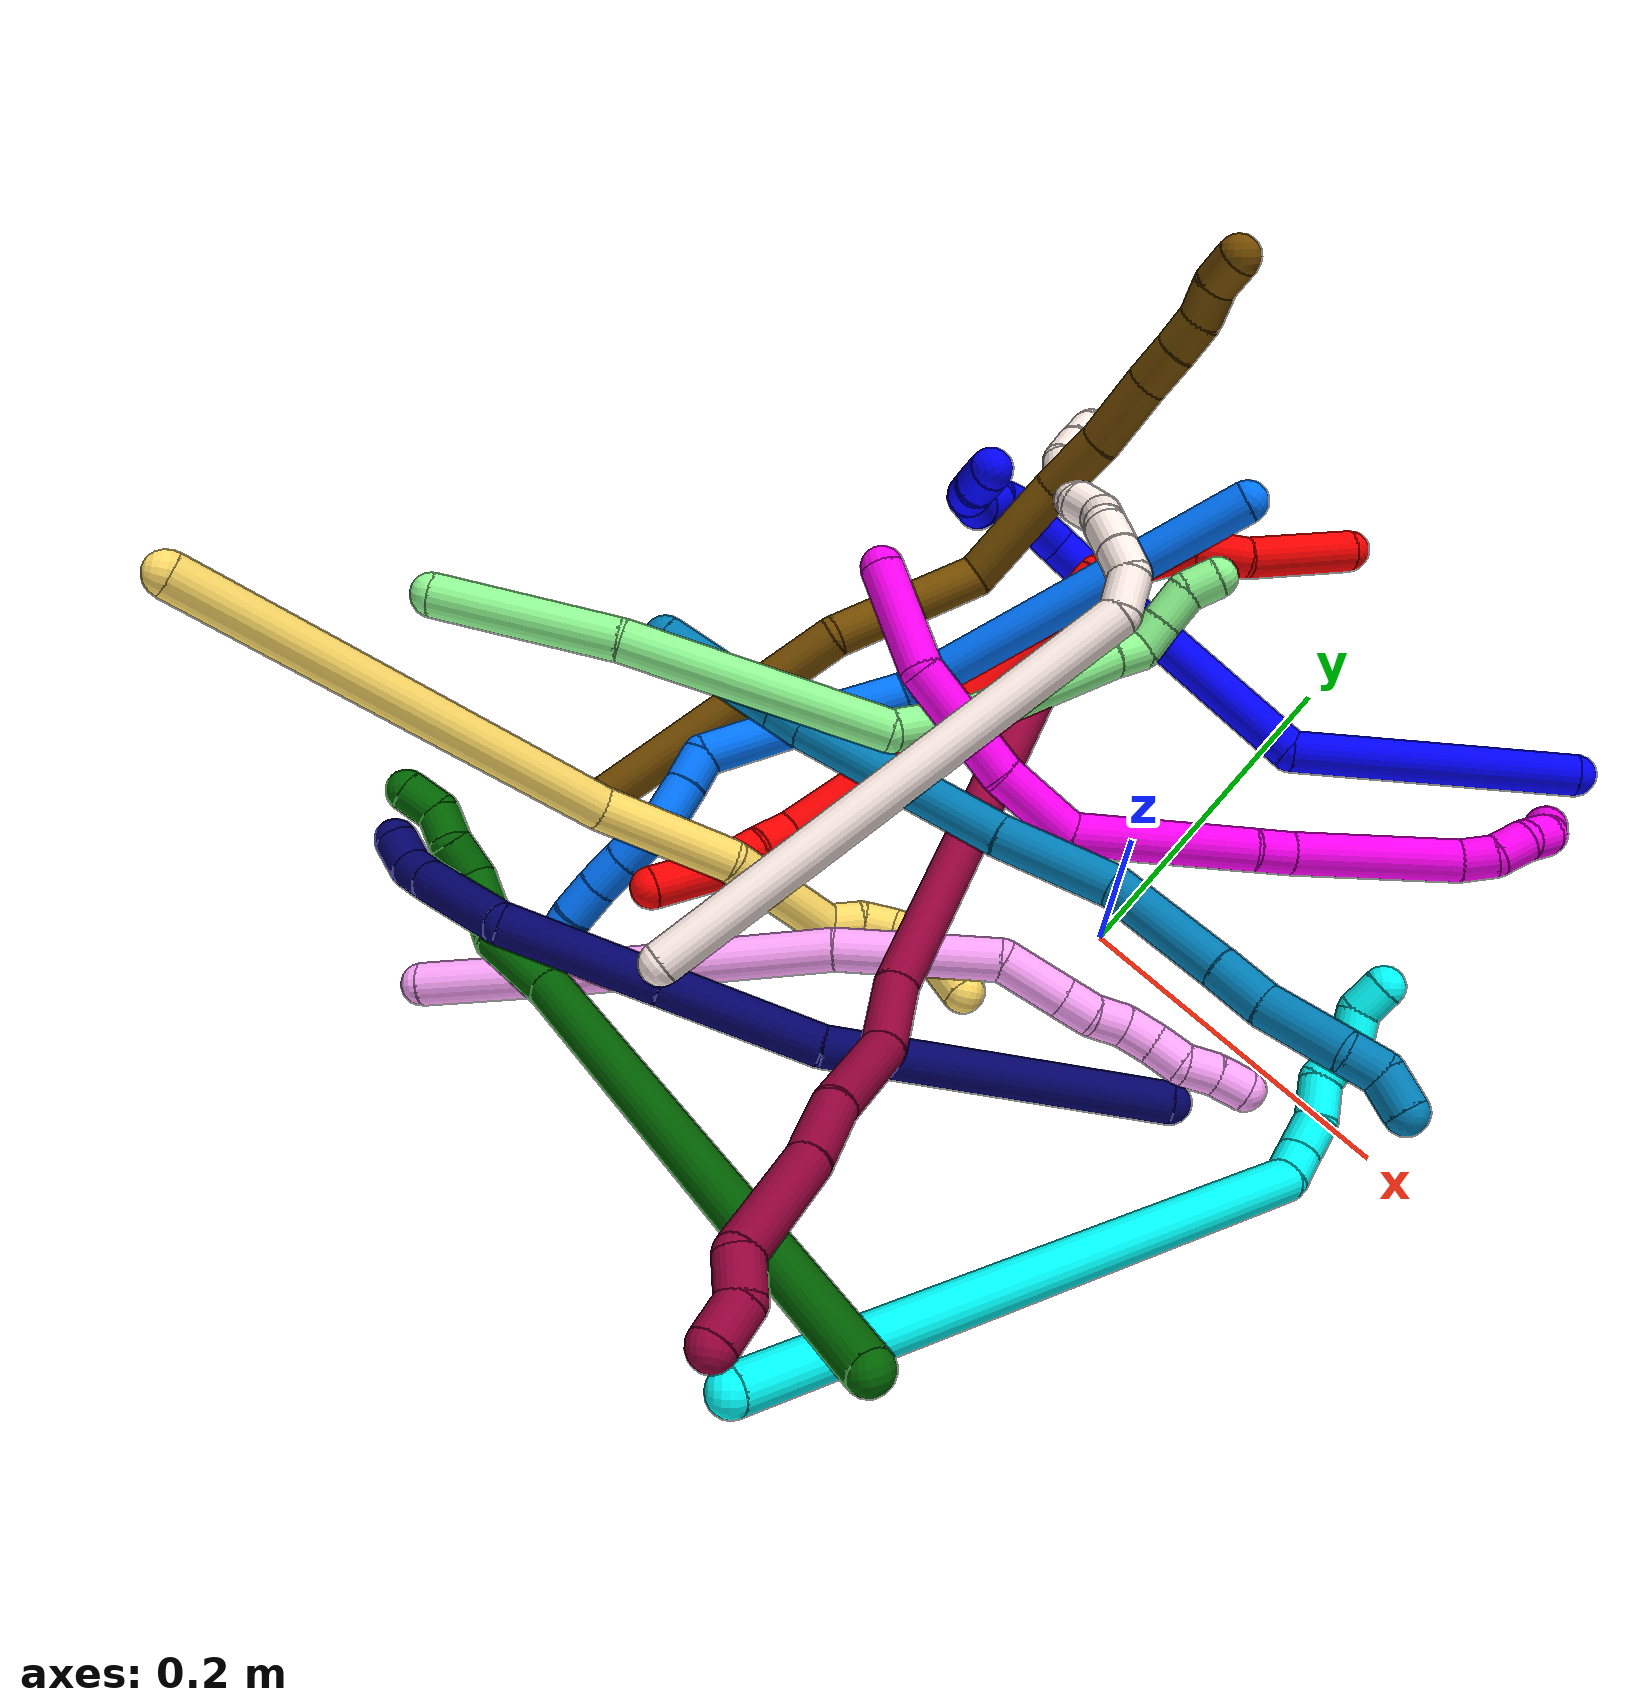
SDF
<sdf version="1.7">
 <world name="default">
  <plugin name="TubeGeneratorPlugin" filename="libtube_generator_plugin.so"/>
  <model name="photoneo_s_sensor">
   <static>1</static>
   <pose>0 0 2 1.57079 1.57079 3.14159</pose>
   <link name="link">
    <inertial><mass>0.1</mass></inertial>
    <sensor name="sensor" type="depth">
     <update_rate>30</update_rate>
     <camera>
      <horizontal_fov>1.22</horizontal_fov>
      <image><width>1920</width><height>1200</height><format>B8G8R8</format></image>
      <clip><near>0.1</near><far>4</far></clip>
      <depth_camera><output>points</output></depth_camera>
     </camera>
     <plugin name="camera_plugin" filename="libgazebo_ros_depth_camera.so">
      <baseline>0.2</baseline>
      <alwaysOn>1</alwaysOn>
      <updateRate>0.0</updateRate>
      <cameraName>camera_ir</cameraName>
      <imageTopicName>/camera/color/image_raw</imageTopicName>
      <cameraInfoTopicName>/camera/color/camera_info</cameraInfoTopicName>
      <depthImageTopicName>/camera/depth/image_raw</depthImageTopicName>
      <depthImageCameraInfoTopicName>/camera/depth/camera_info</depthImageCameraInfoTopicName>
      <pointCloudTopicName>/camera/depth/points</pointCloudTopicName>
      <frameName>fr_optical</frameName>
      <pointCloudCutoff>0.1</pointCloudCutoff>
      <pointCloudCutoffMax>2.0</pointCloudCutoffMax>
      <distortionK1>0</distortionK1>
      <distortionK2>0</distortionK2>
      <distortionK3>0</distortionK3>
      <distortionT1>0</distortionT1>
      <distortionT2>0</distortionT2>
      <CxPrime>0</CxPrime>
      <Cx>0</Cx>
      <Cy>0</Cy>
      <focalLength>0</focalLength>
      <hackBaseline>0</hackBaseline>
     </plugin>
    </sensor>
   </link>
  </model>
  <gravity>0 0 -9.8</gravity>
  <magnetic_field>6e-06 2.3e-05 -4.2e-05</magnetic_field>
  <atmosphere type="adiabatic"/>
  <physics name="default_physics" default="0" type="ode">
   <max_step_size>0.003</max_step_size>
   <real_time_factor>1</real_time_factor>
   <real_time_update_rate>1000</real_time_update_rate>
   <max_contacts>10000</max_contacts>
   <ode>
    <solver>
     <type>quick</type>
     <iters>100</iters>
     <sor>1.3</sor>
     <use_dynamic_moi_rescaling>0</use_dynamic_moi_rescaling>
    </solver>
    <constraints>
     <contact_max_correcting_vel>0</contact_max_correcting_vel>
     <contact_surface_layer>0.001</contact_surface_layer>
     <cfm>0</cfm>
     <erp>0.2</erp>
    </constraints>
   </ode>
  </physics>
  <scene><ambient>0.4 0.4 0.4 1</ambient><background>0.7 0.7 0.7 1</background><shadows>0</shadows></scene>
  <audio><device>default</device></audio>
  <spherical_coordinates>
   <surface_model>EARTH_WGS84</surface_model>
   <latitude_deg>0</latitude_deg>
   <longitude_deg>0</longitude_deg>
   <elevation>0</elevation>
   <heading_deg>0</heading_deg>
  </spherical_coordinates>
  <model name="bin">
   <static>1</static>
   <link name="bottom">
    <collision name="collision-bottom">
     <pose>0 0 -0.01 0 -0 0</pose>
     <geometry><box><size>0.8 0.6 0.02</size></box></geometry>
     <surface>
      <friction><ode><mu>100</mu><mu2>100</mu2></ode></friction>
      <contact><collide_bitmask>65535</collide_bitmask></contact>
     </surface>
    </collision>
   </link>
   <link name="west_wall">
    <collision name="collision-west_wall">
     <pose>-0.41 0 0.1 0 -0 0</pose>
     <geometry><box><size>0.02 0.6 0.2</size></box></geometry>
     <surface>
      <friction><ode><mu>100</mu><mu2>100</mu2></ode></friction>
      <contact><collide_bitmask>65535</collide_bitmask></contact>
     </surface>
    </collision>
   </link>
   <link name="east_wall">
    <collision name="collision-east_wall">
     <pose>0.41 0 0.1 0 -0 0</pose>
     <geometry><box><size>0.02 0.6 0.2</size></box></geometry>
     <surface>
      <friction><ode><mu>100</mu><mu2>100</mu2></ode></friction>
      <contact><collide_bitmask>65535</collide_bitmask></contact>
     </surface>
    </collision>
   </link>
   <link name="south_wall">
    <collision name="collision-south_wall">
     <pose>0 -0.31 0.1 0 -0 0</pose>
     <geometry><box><size>0.8 0.02 0.2</size></box></geometry>
     <surface>
      <friction><ode><mu>100</mu><mu2>100</mu2></ode></friction>
      <contact><collide_bitmask>65535</collide_bitmask></contact>
     </surface>
    </collision>
   </link>
   <link name="north_wall">
    <collision name="collision-north_wall">
     <pose>0 0.31 0.1 0 -0 0</pose>
     <geometry><box><size>0.8 0.02 0.2</size></box></geometry>
     <surface>
      <friction><ode><mu>100</mu><mu2>100</mu2></ode></friction>
      <contact><collide_bitmask>65535</collide_bitmask></contact>
     </surface>
    </collision>
   </link>
  </model>
  <model name="1">
   <static>0</static>
   <link name="1">
    <collision name="collision-cylinder-e_1_1_4">
     <pose>-0.039189 -0.013141 -0.074519 2.96704 -0.47787 -2.45187</pose>
     <geometry><cylinder><radius>0.0125</radius><length>0.170429</length></cylinder></geometry>
     <surface>
      <friction><ode><mu>1.16</mu><mu2>1.16</mu2><slip1>0</slip1><slip2>0</slip2></ode></friction>
      <contact><ode><kp>1e+06</kp><kd>1</kd><max_vel>0</max_vel><min_depth>0.001</min_depth></ode></contact>
     </surface>
    </collision>
    <visual name="visual-cylinder-e_1_1_4">
     <pose>-0.039189 -0.013141 -0.074519 2.96704 -0.47787 -2.45187</pose>
     <geometry><cylinder><radius>0.0125</radius><length>0.170429</length></cylinder></geometry>
     <material><ambient>0 0 1 1</ambient></material>
    </visual>
    <collision name="collision-cylinder-e_2_4_5">
     <pose>-0.142725 -0.037637 -0.174113 2.71643 -1.16657 -2.50934</pose>
     <geometry><cylinder><radius>0.0125</radius><length>0.139974</length></cylinder></geometry>
     <surface>
      <friction><ode><mu>1.16</mu><mu2>1.16</mu2><slip1>0</slip1><slip2>0</slip2></ode></friction>
      <contact><ode><kp>1e+06</kp><kd>1</kd><max_vel>0</max_vel><min_depth>0.001</min_depth></ode></contact>
     </surface>
    </collision>
    <visual name="visual-cylinder-e_2_4_5">
     <pose>-0.142725 -0.037637 -0.174113 2.71643 -1.16657 -2.50934</pose>
     <geometry><cylinder><radius>0.0125</radius><length>0.139974</length></cylinder></geometry>
     <material><ambient>0 0 1 1</ambient></material>
    </visual>
    <collision name="collision-cylinder-e_3_5_6">
     <pose>-0.230004 -0.056244 -0.20886 2.49809 -1.08566 -2.13202</pose>
     <geometry><cylinder><radius>0.0125</radius><length>0.051847</length></cylinder></geometry>
     <surface>
      <friction><ode><mu>1.16</mu><mu2>1.16</mu2><slip1>0</slip1><slip2>0</slip2></ode></friction>
      <contact><ode><kp>1e+06</kp><kd>1</kd><max_vel>0</max_vel><min_depth>0.001</min_depth></ode></contact>
     </surface>
    </collision>
    <visual name="visual-cylinder-e_3_5_6">
     <pose>-0.230004 -0.056244 -0.20886 2.49809 -1.08566 -2.13202</pose>
     <geometry><cylinder><radius>0.0125</radius><length>0.051847</length></cylinder></geometry>
     <material><ambient>0 0 1 1</ambient></material>
    </visual>
    <collision name="collision-cylinder-e_4_6_7">
     <pose>-0.262829 -0.076242 -0.226545 2.1321 -0.581347 -0.992527</pose>
     <geometry><cylinder><radius>0.0125</radius><length>0.03603</length></cylinder></geometry>
     <surface>
      <friction><ode><mu>1.16</mu><mu2>1.16</mu2><slip1>0</slip1><slip2>0</slip2></ode></friction>
      <contact><ode><kp>1e+06</kp><kd>1</kd><max_vel>0</max_vel><min_depth>0.001</min_depth></ode></contact>
     </surface>
    </collision>
    <visual name="visual-cylinder-e_4_6_7">
     <pose>-0.262829 -0.076242 -0.226545 2.1321 -0.581347 -0.992527</pose>
     <geometry><cylinder><radius>0.0125</radius><length>0.03603</length></cylinder></geometry>
     <material><ambient>0 0 1 1</ambient></material>
    </visual>
    <collision name="collision-cylinder-e_5_7_8">
     <pose>-0.272477 -0.097941 -0.240654 2.16848 0.022562 0.042649</pose>
     <geometry><cylinder><radius>0.0125</radius><length>0.021668</length></cylinder></geometry>
     <surface>
      <friction><ode><mu>1.16</mu><mu2>1.16</mu2><slip1>0</slip1><slip2>0</slip2></ode></friction>
      <contact><ode><kp>1e+06</kp><kd>1</kd><max_vel>0</max_vel><min_depth>0.001</min_depth></ode></contact>
     </surface>
    </collision>
    <visual name="visual-cylinder-e_5_7_8">
     <pose>-0.272477 -0.097941 -0.240654 2.16848 0.022562 0.042649</pose>
     <geometry><cylinder><radius>0.0125</radius><length>0.021668</length></cylinder></geometry>
     <material><ambient>0 0 1 1</ambient></material>
    </visual>
    <collision name="collision-cylinder-e_6_8_9">
     <pose>-0.268022 -0.11183 -0.254392 2.56825 0.433418 1.28297</pose>
     <geometry><cylinder><radius>0.0125</radius><length>0.020051</length></cylinder></geometry>
     <surface>
      <friction><ode><mu>1.16</mu><mu2>1.16</mu2><slip1>0</slip1><slip2>0</slip2></ode></friction>
      <contact><ode><kp>1e+06</kp><kd>1</kd><max_vel>0</max_vel><min_depth>0.001</min_depth></ode></contact>
     </surface>
    </collision>
    <visual name="visual-cylinder-e_6_8_9">
     <pose>-0.268022 -0.11183 -0.254392 2.56825 0.433418 1.28297</pose>
     <geometry><cylinder><radius>0.0125</radius><length>0.020051</length></cylinder></geometry>
     <material><ambient>0 0 1 1</ambient></material>
    </visual>
    <collision name="collision-cylinder-e_7_9_10">
     <pose>-0.262344 -0.126262 -0.264804 1.85446 0.147277 0.196069</pose>
     <geometry><cylinder><radius>0.0125</radius><length>0.020001</length></cylinder></geometry>
     <surface>
      <friction><ode><mu>1.16</mu><mu2>1.16</mu2><slip1>0</slip1><slip2>0</slip2></ode></friction>
      <contact><ode><kp>1e+06</kp><kd>1</kd><max_vel>0</max_vel><min_depth>0.001</min_depth></ode></contact>
     </surface>
    </collision>
    <visual name="visual-cylinder-e_7_9_10">
     <pose>-0.262344 -0.126262 -0.264804 1.85446 0.147277 0.196069</pose>
     <geometry><cylinder><radius>0.0125</radius><length>0.020001</length></cylinder></geometry>
     <material><ambient>0 0 1 1</ambient></material>
    </visual>
    <collision name="collision-cylinder-e_8_10_11">
     <pose>-0.25643 -0.144591 -0.266084 1.40376 0.460813 0.391583</pose>
     <geometry><cylinder><radius>0.0125</radius><length>0.02</length></cylinder></geometry>
     <surface>
      <friction><ode><mu>1.16</mu><mu2>1.16</mu2><slip1>0</slip1><slip2>0</slip2></ode></friction>
      <contact><ode><kp>1e+06</kp><kd>1</kd><max_vel>0</max_vel><min_depth>0.001</min_depth></ode></contact>
     </surface>
    </collision>
    <visual name="visual-cylinder-e_8_10_11">
     <pose>-0.25643 -0.144591 -0.266084 1.40376 0.460813 0.391583</pose>
     <geometry><cylinder><radius>0.0125</radius><length>0.02</length></cylinder></geometry>
     <material><ambient>0 0 1 1</ambient></material>
    </visual>
    <collision name="collision-cylinder-e_9_11_2">
     <pose>-0.248858 -0.16197 -0.260447 1.11896 0.317885 0.20009</pose>
     <geometry><cylinder><radius>0.0125</radius><length>0.02</length></cylinder></geometry>
     <surface>
      <friction><ode><mu>1.16</mu><mu2>1.16</mu2><slip1>0</slip1><slip2>0</slip2></ode></friction>
      <contact><ode><kp>1e+06</kp><kd>1</kd><max_vel>0</max_vel><min_depth>0.001</min_depth></ode></contact>
     </surface>
    </collision>
    <visual name="visual-cylinder-e_9_11_2">
     <pose>-0.248858 -0.16197 -0.260447 1.11896 0.317885 0.20009</pose>
     <geometry><cylinder><radius>0.0125</radius><length>0.02</length></cylinder></geometry>
     <material><ambient>0 0 1 1</ambient></material>
    </visual>
    <collision name="collision-sphere-2">
     <pose>-0.245732 -0.170516 -0.2563 0 -0 0</pose>
     <geometry><sphere><radius>0.0125</radius></sphere></geometry>
     <surface>
      <friction><ode><mu>1.16</mu><mu2>1.16</mu2><slip1>0</slip1><slip2>0</slip2></ode></friction>
      <contact><ode><kp>1e+06</kp><kd>1</kd><max_vel>0</max_vel><min_depth>0.001</min_depth></ode></contact>
     </surface>
    </collision>
    <visual name="visual-sphere-2">
     <pose>-0.245732 -0.170516 -0.2563 0 -0 0</pose>
     <geometry><sphere><radius>0.0125</radius></sphere></geometry>
     <material><ambient>0 0 1 1</ambient></material>
    </visual>
    <collision name="collision-sphere-11">
     <pose>-0.251983 -0.153424 -0.264595 0 -0 0</pose>
     <geometry><sphere><radius>0.0125</radius></sphere></geometry>
     <surface>
      <friction><ode><mu>1.16</mu><mu2>1.16</mu2><slip1>0</slip1><slip2>0</slip2></ode></friction>
      <contact><ode><kp>1e+06</kp><kd>1</kd><max_vel>0</max_vel><min_depth>0.001</min_depth></ode></contact>
     </surface>
    </collision>
    <visual name="visual-sphere-11">
     <pose>-0.251983 -0.153424 -0.264595 0 -0 0</pose>
     <geometry><sphere><radius>0.0125</radius></sphere></geometry>
     <material><ambient>0 0 1 1</ambient></material>
    </visual>
    <collision name="collision-sphere-10">
     <pose>-0.260877 -0.135759 -0.267573 0 -0 0</pose>
     <geometry><sphere><radius>0.0125</radius></sphere></geometry>
     <surface>
      <friction><ode><mu>1.16</mu><mu2>1.16</mu2><slip1>0</slip1><slip2>0</slip2></ode></friction>
      <contact><ode><kp>1e+06</kp><kd>1</kd><max_vel>0</max_vel><min_depth>0.001</min_depth></ode></contact>
     </surface>
    </collision>
    <visual name="visual-sphere-10">
     <pose>-0.260877 -0.135759 -0.267573 0 -0 0</pose>
     <geometry><sphere><radius>0.0125</radius></sphere></geometry>
     <material><ambient>0 0 1 1</ambient></material>
    </visual>
    <collision name="collision-sphere-9">
     <pose>-0.263812 -0.116766 -0.262036 0 -0 0</pose>
     <geometry><sphere><radius>0.0125</radius></sphere></geometry>
     <surface>
      <friction><ode><mu>1.16</mu><mu2>1.16</mu2><slip1>0</slip1><slip2>0</slip2></ode></friction>
      <contact><ode><kp>1e+06</kp><kd>1</kd><max_vel>0</max_vel><min_depth>0.001</min_depth></ode></contact>
     </surface>
    </collision>
    <visual name="visual-sphere-9">
     <pose>-0.263812 -0.116766 -0.262036 0 -0 0</pose>
     <geometry><sphere><radius>0.0125</radius></sphere></geometry>
     <material><ambient>0 0 1 1</ambient></material>
    </visual>
    <collision name="collision-sphere-4">
     <pose>-0.078379 -0.026283 -0.149038 0 -0 0</pose>
     <geometry><sphere><radius>0.0125</radius></sphere></geometry>
     <surface>
      <friction><ode><mu>1.16</mu><mu2>1.16</mu2><slip1>0</slip1><slip2>0</slip2></ode></friction>
      <contact><ode><kp>1e+06</kp><kd>1</kd><max_vel>0</max_vel><min_depth>0.001</min_depth></ode></contact>
     </surface>
    </collision>
    <visual name="visual-sphere-4">
     <pose>-0.078379 -0.026283 -0.149038 0 -0 0</pose>
     <geometry><sphere><radius>0.0125</radius></sphere></geometry>
     <material><ambient>0 0 1 1</ambient></material>
    </visual>
    <collision name="collision-sphere-1">
     <geometry><sphere><radius>0.0125</radius></sphere></geometry>
     <surface>
      <friction><ode><mu>1.16</mu><mu2>1.16</mu2><slip1>0</slip1><slip2>0</slip2></ode></friction>
      <contact><ode><kp>1e+06</kp><kd>1</kd><max_vel>0</max_vel><min_depth>0.001</min_depth></ode></contact>
     </surface>
    </collision>
    <visual name="visual-sphere-1">
     <geometry><sphere><radius>0.0125</radius></sphere></geometry>
     <material><ambient>0 0 1 1</ambient></material>
    </visual>
    <collision name="collision-sphere-8">
     <pose>-0.272233 -0.106895 -0.246749 0 -0 0</pose>
     <geometry><sphere><radius>0.0125</radius></sphere></geometry>
     <surface>
      <friction><ode><mu>1.16</mu><mu2>1.16</mu2><slip1>0</slip1><slip2>0</slip2></ode></friction>
      <contact><ode><kp>1e+06</kp><kd>1</kd><max_vel>0</max_vel><min_depth>0.001</min_depth></ode></contact>
     </surface>
    </collision>
    <visual name="visual-sphere-8">
     <pose>-0.272233 -0.106895 -0.246749 0 -0 0</pose>
     <geometry><sphere><radius>0.0125</radius></sphere></geometry>
     <material><ambient>0 0 1 1</ambient></material>
    </visual>
    <collision name="collision-sphere-5">
     <pose>-0.207071 -0.04899 -0.199189 0 -0 0</pose>
     <geometry><sphere><radius>0.0125</radius></sphere></geometry>
     <surface>
      <friction><ode><mu>1.16</mu><mu2>1.16</mu2><slip1>0</slip1><slip2>0</slip2></ode></friction>
      <contact><ode><kp>1e+06</kp><kd>1</kd><max_vel>0</max_vel><min_depth>0.001</min_depth></ode></contact>
     </surface>
    </collision>
    <visual name="visual-sphere-5">
     <pose>-0.207071 -0.04899 -0.199189 0 -0 0</pose>
     <geometry><sphere><radius>0.0125</radius></sphere></geometry>
     <material><ambient>0 0 1 1</ambient></material>
    </visual>
    <collision name="collision-sphere-6">
     <pose>-0.252936 -0.063497 -0.218531 0 -0 0</pose>
     <geometry><sphere><radius>0.0125</radius></sphere></geometry>
     <surface>
      <friction><ode><mu>1.16</mu><mu2>1.16</mu2><slip1>0</slip1><slip2>0</slip2></ode></friction>
      <contact><ode><kp>1e+06</kp><kd>1</kd><max_vel>0</max_vel><min_depth>0.001</min_depth></ode></contact>
     </surface>
    </collision>
    <visual name="visual-sphere-6">
     <pose>-0.252936 -0.063497 -0.218531 0 -0 0</pose>
     <geometry><sphere><radius>0.0125</radius></sphere></geometry>
     <material><ambient>0 0 1 1</ambient></material>
    </visual>
    <collision name="collision-sphere-7">
     <pose>-0.272722 -0.088988 -0.234559 0 -0 0</pose>
     <geometry><sphere><radius>0.0125</radius></sphere></geometry>
     <surface>
      <friction><ode><mu>1.16</mu><mu2>1.16</mu2><slip1>0</slip1><slip2>0</slip2></ode></friction>
      <contact><ode><kp>1e+06</kp><kd>1</kd><max_vel>0</max_vel><min_depth>0.001</min_depth></ode></contact>
     </surface>
    </collision>
    <visual name="visual-sphere-7">
     <pose>-0.272722 -0.088988 -0.234559 0 -0 0</pose>
     <geometry><sphere><radius>0.0125</radius></sphere></geometry>
     <material><ambient>0 0 1 1</ambient></material>
    </visual>
    <inertial>
     <pose>-0.149365 -0.052384 -0.16441 0 -0 0</pose>
     <mass>0.5</mass>
     <inertia>
      <ixx>-0.000673</ixx>
      <ixy>0</ixy>
      <ixz>0</ixz>
      <iyy>0.000265</iyy>
      <iyz>0</iyz>
      <izz>0.000517</izz>
     </inertia>
    </inertial>
   </link>
   <pose>0.151845 0.259251 0.01344 -1.53705 -0.206753 -0.441103</pose>
  </model>
  <model name="2">
   <static>0</static>
   <link name="2">
    <collision name="collision-cylinder-e_1_1_4">
     <pose>-0.01415 -0.02442 0.02078 0.865764 -0.415602 -0.194255</pose>
     <geometry><cylinder><radius>0.0125</radius><length>0.070097</length></cylinder></geometry>
     <surface>
      <friction><ode><mu>1.16</mu><mu2>1.16</mu2><slip1>0</slip1><slip2>0</slip2></ode></friction>
      <contact><ode><kp>1e+06</kp><kd>1</kd><max_vel>0</max_vel><min_depth>0.001</min_depth></ode></contact>
     </surface>
    </collision>
    <visual name="visual-cylinder-e_1_1_4">
     <pose>-0.01415 -0.02442 0.02078 0.865764 -0.415602 -0.194255</pose>
     <geometry><cylinder><radius>0.0125</radius><length>0.070097</length></cylinder></geometry>
     <material><ambient>1 0 0 1</ambient></material>
    </visual>
    <collision name="collision-cylinder-e_2_4_5">
     <pose>-0.038861 -0.058794 0.052481 0.739078 -0.620478 -0.247086</pose>
     <geometry><cylinder><radius>0.0125</radius><length>0.036323</length></cylinder></geometry>
     <surface>
      <friction><ode><mu>1.16</mu><mu2>1.16</mu2><slip1>0</slip1><slip2>0</slip2></ode></friction>
      <contact><ode><kp>1e+06</kp><kd>1</kd><max_vel>0</max_vel><min_depth>0.001</min_depth></ode></contact>
     </surface>
    </collision>
    <visual name="visual-cylinder-e_2_4_5">
     <pose>-0.038861 -0.058794 0.052481 0.739078 -0.620478 -0.247086</pose>
     <geometry><cylinder><radius>0.0125</radius><length>0.036323</length></cylinder></geometry>
     <material><ambient>1 0 0 1</ambient></material>
    </visual>
    <collision name="collision-cylinder-e_3_5_6">
     <pose>-0.062218 -0.093211 0.073333 1.18518 -0.451353 -0.306739</pose>
     <geometry><cylinder><radius>0.0125</radius><length>0.058682</length></cylinder></geometry>
     <surface>
      <friction><ode><mu>1.16</mu><mu2>1.16</mu2><slip1>0</slip1><slip2>0</slip2></ode></friction>
      <contact><ode><kp>1e+06</kp><kd>1</kd><max_vel>0</max_vel><min_depth>0.001</min_depth></ode></contact>
     </surface>
    </collision>
    <visual name="visual-cylinder-e_3_5_6">
     <pose>-0.062218 -0.093211 0.073333 1.18518 -0.451353 -0.306739</pose>
     <geometry><cylinder><radius>0.0125</radius><length>0.058682</length></cylinder></geometry>
     <material><ambient>1 0 0 1</ambient></material>
    </visual>
    <collision name="collision-cylinder-e_4_6_7">
     <pose>-0.074946 -0.129076 0.083805 1.52339 0.006185 0.005899</pose>
     <geometry><cylinder><radius>0.0125</radius><length>0.022827</length></cylinder></geometry>
     <surface>
      <friction><ode><mu>1.16</mu><mu2>1.16</mu2><slip1>0</slip1><slip2>0</slip2></ode></friction>
      <contact><ode><kp>1e+06</kp><kd>1</kd><max_vel>0</max_vel><min_depth>0.001</min_depth></ode></contact>
     </surface>
    </collision>
    <visual name="visual-cylinder-e_4_6_7">
     <pose>-0.074946 -0.129076 0.083805 1.52339 0.006185 0.005899</pose>
     <geometry><cylinder><radius>0.0125</radius><length>0.022827</length></cylinder></geometry>
     <material><ambient>1 0 0 1</ambient></material>
    </visual>
    <collision name="collision-cylinder-e_5_7_8">
     <pose>-0.078693 -0.200111 0.089582 1.4832 -0.063688 -0.058344</pose>
     <geometry><cylinder><radius>0.0125</radius><length>0.119972</length></cylinder></geometry>
     <surface>
      <friction><ode><mu>1.16</mu><mu2>1.16</mu2><slip1>0</slip1><slip2>0</slip2></ode></friction>
      <contact><ode><kp>1e+06</kp><kd>1</kd><max_vel>0</max_vel><min_depth>0.001</min_depth></ode></contact>
     </surface>
    </collision>
    <visual name="visual-cylinder-e_5_7_8">
     <pose>-0.078693 -0.200111 0.089582 1.4832 -0.063688 -0.058344</pose>
     <geometry><cylinder><radius>0.0125</radius><length>0.119972</length></cylinder></geometry>
     <material><ambient>1 0 0 1</ambient></material>
    </visual>
    <collision name="collision-cylinder-e_6_8_9">
     <pose>-0.08912 -0.306642 0.10837 1.28951 -0.134581 -0.101267</pose>
     <geometry><cylinder><radius>0.0125</radius><length>0.098519</length></cylinder></geometry>
     <surface>
      <friction><ode><mu>1.16</mu><mu2>1.16</mu2><slip1>0</slip1><slip2>0</slip2></ode></friction>
      <contact><ode><kp>1e+06</kp><kd>1</kd><max_vel>0</max_vel><min_depth>0.001</min_depth></ode></contact>
     </surface>
    </collision>
    <visual name="visual-cylinder-e_6_8_9">
     <pose>-0.08912 -0.306642 0.10837 1.28951 -0.134581 -0.101267</pose>
     <geometry><cylinder><radius>0.0125</radius><length>0.098519</length></cylinder></geometry>
     <material><ambient>1 0 0 1</ambient></material>
    </visual>
    <collision name="collision-cylinder-e_7_9_10">
     <pose>-0.095514 -0.362747 0.129712 0.868575 0.017909 0.008307</pose>
     <geometry><cylinder><radius>0.0125</radius><length>0.024131</length></cylinder></geometry>
     <surface>
      <friction><ode><mu>1.16</mu><mu2>1.16</mu2><slip1>0</slip1><slip2>0</slip2></ode></friction>
      <contact><ode><kp>1e+06</kp><kd>1</kd><max_vel>0</max_vel><min_depth>0.001</min_depth></ode></contact>
     </surface>
    </collision>
    <visual name="visual-cylinder-e_7_9_10">
     <pose>-0.095514 -0.362747 0.129712 0.868575 0.017909 0.008307</pose>
     <geometry><cylinder><radius>0.0125</radius><length>0.024131</length></cylinder></geometry>
     <material><ambient>1 0 0 1</ambient></material>
    </visual>
    <collision name="collision-cylinder-e_8_10_11">
     <pose>-0.095993 -0.382993 0.143606 1.0657 -0.055136 -0.032522</pose>
     <geometry><cylinder><radius>0.0125</radius><length>0.02526</length></cylinder></geometry>
     <surface>
      <friction><ode><mu>1.16</mu><mu2>1.16</mu2><slip1>0</slip1><slip2>0</slip2></ode></friction>
      <contact><ode><kp>1e+06</kp><kd>1</kd><max_vel>0</max_vel><min_depth>0.001</min_depth></ode></contact>
     </surface>
    </collision>
    <visual name="visual-cylinder-e_8_10_11">
     <pose>-0.095993 -0.382993 0.143606 1.0657 -0.055136 -0.032522</pose>
     <geometry><cylinder><radius>0.0125</radius><length>0.02526</length></cylinder></geometry>
     <material><ambient>1 0 0 1</ambient></material>
    </visual>
    <collision name="collision-cylinder-e_9_11_2">
     <pose>-0.101637 -0.410883 0.163111 0.899008 -0.225823 -0.109303</pose>
     <geometry><cylinder><radius>0.0125</radius><length>0.044188</length></cylinder></geometry>
     <surface>
      <friction><ode><mu>1.16</mu><mu2>1.16</mu2><slip1>0</slip1><slip2>0</slip2></ode></friction>
      <contact><ode><kp>1e+06</kp><kd>1</kd><max_vel>0</max_vel><min_depth>0.001</min_depth></ode></contact>
     </surface>
    </collision>
    <visual name="visual-cylinder-e_9_11_2">
     <pose>-0.101637 -0.410883 0.163111 0.899008 -0.225823 -0.109303</pose>
     <geometry><cylinder><radius>0.0125</radius><length>0.044188</length></cylinder></geometry>
     <material><ambient>1 0 0 1</ambient></material>
    </visual>
    <collision name="collision-sphere-2">
     <pose>-0.106584 -0.427737 0.176513 0 -0 0</pose>
     <geometry><sphere><radius>0.0125</radius></sphere></geometry>
     <surface>
      <friction><ode><mu>1.16</mu><mu2>1.16</mu2><slip1>0</slip1><slip2>0</slip2></ode></friction>
      <contact><ode><kp>1e+06</kp><kd>1</kd><max_vel>0</max_vel><min_depth>0.001</min_depth></ode></contact>
     </surface>
    </collision>
    <visual name="visual-sphere-2">
     <pose>-0.106584 -0.427737 0.176513 0 -0 0</pose>
     <geometry><sphere><radius>0.0125</radius></sphere></geometry>
     <material><ambient>1 0 0 1</ambient></material>
    </visual>
    <collision name="collision-sphere-11">
     <pose>-0.096689 -0.394029 0.149709 0 -0 0</pose>
     <geometry><sphere><radius>0.0125</radius></sphere></geometry>
     <surface>
      <friction><ode><mu>1.16</mu><mu2>1.16</mu2><slip1>0</slip1><slip2>0</slip2></ode></friction>
      <contact><ode><kp>1e+06</kp><kd>1</kd><max_vel>0</max_vel><min_depth>0.001</min_depth></ode></contact>
     </surface>
    </collision>
    <visual name="visual-sphere-11">
     <pose>-0.096689 -0.394029 0.149709 0 -0 0</pose>
     <geometry><sphere><radius>0.0125</radius></sphere></geometry>
     <material><ambient>1 0 0 1</ambient></material>
    </visual>
    <collision name="collision-sphere-10">
     <pose>-0.095297 -0.371957 0.137504 0 -0 0</pose>
     <geometry><sphere><radius>0.0125</radius></sphere></geometry>
     <surface>
      <friction><ode><mu>1.16</mu><mu2>1.16</mu2><slip1>0</slip1><slip2>0</slip2></ode></friction>
      <contact><ode><kp>1e+06</kp><kd>1</kd><max_vel>0</max_vel><min_depth>0.001</min_depth></ode></contact>
     </surface>
    </collision>
    <visual name="visual-sphere-10">
     <pose>-0.095297 -0.371957 0.137504 0 -0 0</pose>
     <geometry><sphere><radius>0.0125</radius></sphere></geometry>
     <material><ambient>1 0 0 1</ambient></material>
    </visual>
    <collision name="collision-sphere-9">
     <pose>-0.09573 -0.353538 0.12192 0 -0 0</pose>
     <geometry><sphere><radius>0.0125</radius></sphere></geometry>
     <surface>
      <friction><ode><mu>1.16</mu><mu2>1.16</mu2><slip1>0</slip1><slip2>0</slip2></ode></friction>
      <contact><ode><kp>1e+06</kp><kd>1</kd><max_vel>0</max_vel><min_depth>0.001</min_depth></ode></contact>
     </surface>
    </collision>
    <visual name="visual-sphere-9">
     <pose>-0.09573 -0.353538 0.12192 0 -0 0</pose>
     <geometry><sphere><radius>0.0125</radius></sphere></geometry>
     <material><ambient>1 0 0 1</ambient></material>
    </visual>
    <collision name="collision-sphere-4">
     <pose>-0.028301 -0.04884 0.04156 0 -0 0</pose>
     <geometry><sphere><radius>0.0125</radius></sphere></geometry>
     <surface>
      <friction><ode><mu>1.16</mu><mu2>1.16</mu2><slip1>0</slip1><slip2>0</slip2></ode></friction>
      <contact><ode><kp>1e+06</kp><kd>1</kd><max_vel>0</max_vel><min_depth>0.001</min_depth></ode></contact>
     </surface>
    </collision>
    <visual name="visual-sphere-4">
     <pose>-0.028301 -0.04884 0.04156 0 -0 0</pose>
     <geometry><sphere><radius>0.0125</radius></sphere></geometry>
     <material><ambient>1 0 0 1</ambient></material>
    </visual>
    <collision name="collision-sphere-1">
     <geometry><sphere><radius>0.0125</radius></sphere></geometry>
     <surface>
      <friction><ode><mu>1.16</mu><mu2>1.16</mu2><slip1>0</slip1><slip2>0</slip2></ode></friction>
      <contact><ode><kp>1e+06</kp><kd>1</kd><max_vel>0</max_vel><min_depth>0.001</min_depth></ode></contact>
     </surface>
    </collision>
    <visual name="visual-sphere-1">
     <geometry><sphere><radius>0.0125</radius></sphere></geometry>
     <material><ambient>1 0 0 1</ambient></material>
    </visual>
    <collision name="collision-sphere-8">
     <pose>-0.082511 -0.259746 0.09482 0 -0 0</pose>
     <geometry><sphere><radius>0.0125</radius></sphere></geometry>
     <surface>
      <friction><ode><mu>1.16</mu><mu2>1.16</mu2><slip1>0</slip1><slip2>0</slip2></ode></friction>
      <contact><ode><kp>1e+06</kp><kd>1</kd><max_vel>0</max_vel><min_depth>0.001</min_depth></ode></contact>
     </surface>
    </collision>
    <visual name="visual-sphere-8">
     <pose>-0.082511 -0.259746 0.09482 0 -0 0</pose>
     <geometry><sphere><radius>0.0125</radius></sphere></geometry>
     <material><ambient>1 0 0 1</ambient></material>
    </visual>
    <collision name="collision-sphere-5">
     <pose>-0.04942 -0.068747 0.063402 0 -0 0</pose>
     <geometry><sphere><radius>0.0125</radius></sphere></geometry>
     <surface>
      <friction><ode><mu>1.16</mu><mu2>1.16</mu2><slip1>0</slip1><slip2>0</slip2></ode></friction>
      <contact><ode><kp>1e+06</kp><kd>1</kd><max_vel>0</max_vel><min_depth>0.001</min_depth></ode></contact>
     </surface>
    </collision>
    <visual name="visual-sphere-5">
     <pose>-0.04942 -0.068747 0.063402 0 -0 0</pose>
     <geometry><sphere><radius>0.0125</radius></sphere></geometry>
     <material><ambient>1 0 0 1</ambient></material>
    </visual>
    <collision name="collision-sphere-6">
     <pose>-0.075016 -0.117675 0.083264 0 -0 0</pose>
     <geometry><sphere><radius>0.0125</radius></sphere></geometry>
     <surface>
      <friction><ode><mu>1.16</mu><mu2>1.16</mu2><slip1>0</slip1><slip2>0</slip2></ode></friction>
      <contact><ode><kp>1e+06</kp><kd>1</kd><max_vel>0</max_vel><min_depth>0.001</min_depth></ode></contact>
     </surface>
    </collision>
    <visual name="visual-sphere-6">
     <pose>-0.075016 -0.117675 0.083264 0 -0 0</pose>
     <geometry><sphere><radius>0.0125</radius></sphere></geometry>
     <material><ambient>1 0 0 1</ambient></material>
    </visual>
    <collision name="collision-sphere-7">
     <pose>-0.074875 -0.140476 0.084345 0 -0 0</pose>
     <geometry><sphere><radius>0.0125</radius></sphere></geometry>
     <surface>
      <friction><ode><mu>1.16</mu><mu2>1.16</mu2><slip1>0</slip1><slip2>0</slip2></ode></friction>
      <contact><ode><kp>1e+06</kp><kd>1</kd><max_vel>0</max_vel><min_depth>0.001</min_depth></ode></contact>
     </surface>
    </collision>
    <visual name="visual-sphere-7">
     <pose>-0.074875 -0.140476 0.084345 0 -0 0</pose>
     <geometry><sphere><radius>0.0125</radius></sphere></geometry>
     <material><ambient>1 0 0 1</ambient></material>
    </visual>
    <inertial>
     <pose>-0.070414 -0.206131 0.089937 0 -0 0</pose>
     <mass>0.5</mass>
     <inertia>
      <ixx>0.000256</ixx>
      <ixy>0</ixy>
      <ixz>0</ixz>
      <iyy>1.8e-05</iyy>
      <iyz>0</iyz>
      <izz>0.000341</izz>
     </inertia>
    </inertial>
   </link>
   <pose>-0.039887 0.287392 0.010922 0.241784 -0.321322 -0.102405</pose>
  </model>
  <model name="3">
   <static>0</static>
   <link name="3">
    <collision name="collision-cylinder-e_1_1_4">
     <pose>-0.037067 0.100546 -0.147471 -2.54319 -0.204764 0.643037</pose>
     <geometry><cylinder><radius>0.0125</radius><length>0.364589</length></cylinder></geometry>
     <surface>
      <friction><ode><mu>1.16</mu><mu2>1.16</mu2><slip1>0</slip1><slip2>0</slip2></ode></friction>
      <contact><ode><kp>1e+06</kp><kd>1</kd><max_vel>0</max_vel><min_depth>0.001</min_depth></ode></contact>
     </surface>
    </collision>
    <visual name="visual-cylinder-e_1_1_4">
     <pose>-0.037067 0.100546 -0.147471 -2.54319 -0.204764 0.643037</pose>
     <geometry><cylinder><radius>0.0125</radius><length>0.364589</length></cylinder></geometry>
     <material><ambient>0.003922 1 0.996078 1</ambient></material>
    </visual>
    <collision name="collision-cylinder-e_2_4_5">
     <pose>-0.073236 0.210169 -0.300011 -2.07999 0.086195 -0.146669</pose>
     <geometry><cylinder><radius>0.0125</radius><length>0.020869</length></cylinder></geometry>
     <surface>
      <friction><ode><mu>1.16</mu><mu2>1.16</mu2><slip1>0</slip1><slip2>0</slip2></ode></friction>
      <contact><ode><kp>1e+06</kp><kd>1</kd><max_vel>0</max_vel><min_depth>0.001</min_depth></ode></contact>
     </surface>
    </collision>
    <visual name="visual-cylinder-e_2_4_5">
     <pose>-0.073236 0.210169 -0.300011 -2.07999 0.086195 -0.146669</pose>
     <geometry><cylinder><radius>0.0125</radius><length>0.020869</length></cylinder></geometry>
     <material><ambient>0.003922 1 0.996078 1</ambient></material>
    </visual>
    <collision name="collision-cylinder-e_3_5_6">
     <pose>-0.068043 0.228013 -0.310709 -2.14169 0.390923 -0.695464</pose>
     <geometry><cylinder><radius>0.0125</radius><length>0.022539</length></cylinder></geometry>
     <surface>
      <friction><ode><mu>1.16</mu><mu2>1.16</mu2><slip1>0</slip1><slip2>0</slip2></ode></friction>
      <contact><ode><kp>1e+06</kp><kd>1</kd><max_vel>0</max_vel><min_depth>0.001</min_depth></ode></contact>
     </surface>
    </collision>
    <visual name="visual-cylinder-e_3_5_6">
     <pose>-0.068043 0.228013 -0.310709 -2.14169 0.390923 -0.695464</pose>
     <geometry><cylinder><radius>0.0125</radius><length>0.022539</length></cylinder></geometry>
     <material><ambient>0.003922 1 0.996078 1</ambient></material>
    </visual>
    <collision name="collision-cylinder-e_4_6_7">
     <pose>-0.058561 0.247647 -0.318431 -1.76094 0.438415 -0.526971</pose>
     <geometry><cylinder><radius>0.0125</radius><length>0.024445</length></cylinder></geometry>
     <surface>
      <friction><ode><mu>1.16</mu><mu2>1.16</mu2><slip1>0</slip1><slip2>0</slip2></ode></friction>
      <contact><ode><kp>1e+06</kp><kd>1</kd><max_vel>0</max_vel><min_depth>0.001</min_depth></ode></contact>
     </surface>
    </collision>
    <visual name="visual-cylinder-e_4_6_7">
     <pose>-0.058561 0.247647 -0.318431 -1.76094 0.438415 -0.526971</pose>
     <geometry><cylinder><radius>0.0125</radius><length>0.024445</length></cylinder></geometry>
     <material><ambient>0.003922 1 0.996078 1</ambient></material>
    </visual>
    <collision name="collision-cylinder-e_5_7_8">
     <pose>-0.046172 0.266163 -0.329244 -2.42162 0.555519 -1.29662</pose>
     <geometry><cylinder><radius>0.0125</radius><length>0.027306</length></cylinder></geometry>
     <surface>
      <friction><ode><mu>1.16</mu><mu2>1.16</mu2><slip1>0</slip1><slip2>0</slip2></ode></friction>
      <contact><ode><kp>1e+06</kp><kd>1</kd><max_vel>0</max_vel><min_depth>0.001</min_depth></ode></contact>
     </surface>
    </collision>
    <visual name="visual-cylinder-e_5_7_8">
     <pose>-0.046172 0.266163 -0.329244 -2.42162 0.555519 -1.29662</pose>
     <geometry><cylinder><radius>0.0125</radius><length>0.027306</length></cylinder></geometry>
     <material><ambient>0.003922 1 0.996078 1</ambient></material>
    </visual>
    <collision name="collision-cylinder-e_6_8_9">
     <pose>-0.032066 0.280844 -0.340189 -1.87706 0.75246 -0.989101</pose>
     <geometry><cylinder><radius>0.0125</radius><length>0.020208</length></cylinder></geometry>
     <surface>
      <friction><ode><mu>1.16</mu><mu2>1.16</mu2><slip1>0</slip1><slip2>0</slip2></ode></friction>
      <contact><ode><kp>1e+06</kp><kd>1</kd><max_vel>0</max_vel><min_depth>0.001</min_depth></ode></contact>
     </surface>
    </collision>
    <visual name="visual-cylinder-e_6_8_9">
     <pose>-0.032066 0.280844 -0.340189 -1.87706 0.75246 -0.989101</pose>
     <geometry><cylinder><radius>0.0125</radius><length>0.020208</length></cylinder></geometry>
     <material><ambient>0.003922 1 0.996078 1</ambient></material>
    </visual>
    <collision name="collision-cylinder-e_7_9_2">
     <pose>-0.017849 0.290518 -0.348737 -2.74594 0.817721 -2.27497</pose>
     <geometry><cylinder><radius>0.0125</radius><length>0.020043</length></cylinder></geometry>
     <surface>
      <friction><ode><mu>1.16</mu><mu2>1.16</mu2><slip1>0</slip1><slip2>0</slip2></ode></friction>
      <contact><ode><kp>1e+06</kp><kd>1</kd><max_vel>0</max_vel><min_depth>0.001</min_depth></ode></contact>
     </surface>
    </collision>
    <visual name="visual-cylinder-e_7_9_2">
     <pose>-0.017849 0.290518 -0.348737 -2.74594 0.817721 -2.27497</pose>
     <geometry><cylinder><radius>0.0125</radius><length>0.020043</length></cylinder></geometry>
     <material><ambient>0.003922 1 0.996078 1</ambient></material>
    </visual>
    <collision name="collision-sphere-2">
     <pose>-0.010537 0.29316 -0.355061 0 -0 0</pose>
     <geometry><sphere><radius>0.0125</radius></sphere></geometry>
     <surface>
      <friction><ode><mu>1.16</mu><mu2>1.16</mu2><slip1>0</slip1><slip2>0</slip2></ode></friction>
      <contact><ode><kp>1e+06</kp><kd>1</kd><max_vel>0</max_vel><min_depth>0.001</min_depth></ode></contact>
     </surface>
    </collision>
    <visual name="visual-sphere-2">
     <pose>-0.010537 0.29316 -0.355061 0 -0 0</pose>
     <geometry><sphere><radius>0.0125</radius></sphere></geometry>
     <material><ambient>0.003922 1 0.996078 1</ambient></material>
    </visual>
    <collision name="collision-sphere-9">
     <pose>-0.02516 0.287877 -0.342413 0 -0 0</pose>
     <geometry><sphere><radius>0.0125</radius></sphere></geometry>
     <surface>
      <friction><ode><mu>1.16</mu><mu2>1.16</mu2><slip1>0</slip1><slip2>0</slip2></ode></friction>
      <contact><ode><kp>1e+06</kp><kd>1</kd><max_vel>0</max_vel><min_depth>0.001</min_depth></ode></contact>
     </surface>
    </collision>
    <visual name="visual-sphere-9">
     <pose>-0.02516 0.287877 -0.342413 0 -0 0</pose>
     <geometry><sphere><radius>0.0125</radius></sphere></geometry>
     <material><ambient>0.003922 1 0.996078 1</ambient></material>
    </visual>
    <collision name="collision-sphere-4">
     <pose>-0.074134 0.201092 -0.294943 0 -0 0</pose>
     <geometry><sphere><radius>0.0125</radius></sphere></geometry>
     <surface>
      <friction><ode><mu>1.16</mu><mu2>1.16</mu2><slip1>0</slip1><slip2>0</slip2></ode></friction>
      <contact><ode><kp>1e+06</kp><kd>1</kd><max_vel>0</max_vel><min_depth>0.001</min_depth></ode></contact>
     </surface>
    </collision>
    <visual name="visual-sphere-4">
     <pose>-0.074134 0.201092 -0.294943 0 -0 0</pose>
     <geometry><sphere><radius>0.0125</radius></sphere></geometry>
     <material><ambient>0.003922 1 0.996078 1</ambient></material>
    </visual>
    <collision name="collision-sphere-1">
     <geometry><sphere><radius>0.0125</radius></sphere></geometry>
     <surface>
      <friction><ode><mu>1.16</mu><mu2>1.16</mu2><slip1>0</slip1><slip2>0</slip2></ode></friction>
      <contact><ode><kp>1e+06</kp><kd>1</kd><max_vel>0</max_vel><min_depth>0.001</min_depth></ode></contact>
     </surface>
    </collision>
    <visual name="visual-sphere-1">
     <geometry><sphere><radius>0.0125</radius></sphere></geometry>
     <material><ambient>0.003922 1 0.996078 1</ambient></material>
    </visual>
    <collision name="collision-sphere-8">
     <pose>-0.038971 0.273811 -0.337965 0 -0 0</pose>
     <geometry><sphere><radius>0.0125</radius></sphere></geometry>
     <surface>
      <friction><ode><mu>1.16</mu><mu2>1.16</mu2><slip1>0</slip1><slip2>0</slip2></ode></friction>
      <contact><ode><kp>1e+06</kp><kd>1</kd><max_vel>0</max_vel><min_depth>0.001</min_depth></ode></contact>
     </surface>
    </collision>
    <visual name="visual-sphere-8">
     <pose>-0.038971 0.273811 -0.337965 0 -0 0</pose>
     <geometry><sphere><radius>0.0125</radius></sphere></geometry>
     <material><ambient>0.003922 1 0.996078 1</ambient></material>
    </visual>
    <collision name="collision-sphere-5">
     <pose>-0.072338 0.219246 -0.305079 0 -0 0</pose>
     <geometry><sphere><radius>0.0125</radius></sphere></geometry>
     <surface>
      <friction><ode><mu>1.16</mu><mu2>1.16</mu2><slip1>0</slip1><slip2>0</slip2></ode></friction>
      <contact><ode><kp>1e+06</kp><kd>1</kd><max_vel>0</max_vel><min_depth>0.001</min_depth></ode></contact>
     </surface>
    </collision>
    <visual name="visual-sphere-5">
     <pose>-0.072338 0.219246 -0.305079 0 -0 0</pose>
     <geometry><sphere><radius>0.0125</radius></sphere></geometry>
     <material><ambient>0.003922 1 0.996078 1</ambient></material>
    </visual>
    <collision name="collision-sphere-6">
     <pose>-0.063749 0.23678 -0.316339 0 -0 0</pose>
     <geometry><sphere><radius>0.0125</radius></sphere></geometry>
     <surface>
      <friction><ode><mu>1.16</mu><mu2>1.16</mu2><slip1>0</slip1><slip2>0</slip2></ode></friction>
      <contact><ode><kp>1e+06</kp><kd>1</kd><max_vel>0</max_vel><min_depth>0.001</min_depth></ode></contact>
     </surface>
    </collision>
    <visual name="visual-sphere-6">
     <pose>-0.063749 0.23678 -0.316339 0 -0 0</pose>
     <geometry><sphere><radius>0.0125</radius></sphere></geometry>
     <material><ambient>0.003922 1 0.996078 1</ambient></material>
    </visual>
    <collision name="collision-sphere-7">
     <pose>-0.053372 0.258514 -0.320523 0 -0 0</pose>
     <geometry><sphere><radius>0.0125</radius></sphere></geometry>
     <surface>
      <friction><ode><mu>1.16</mu><mu2>1.16</mu2><slip1>0</slip1><slip2>0</slip2></ode></friction>
      <contact><ode><kp>1e+06</kp><kd>1</kd><max_vel>0</max_vel><min_depth>0.001</min_depth></ode></contact>
     </surface>
    </collision>
    <visual name="visual-sphere-7">
     <pose>-0.053372 0.258514 -0.320523 0 -0 0</pose>
     <geometry><sphere><radius>0.0125</radius></sphere></geometry>
     <material><ambient>0.003922 1 0.996078 1</ambient></material>
    </visual>
    <inertial>
     <pose>-0.040549 0.142006 -0.195339 0 -0 0</pose>
     <mass>0.5</mass>
     <inertia>
      <ixx>0.005553</ixx>
      <ixy>0</ixy>
      <ixz>0</ixz>
      <iyy>-4e-06</iyy>
      <iyz>0</iyz>
      <izz>-0.001452</izz>
     </inertia>
    </inertial>
   </link>
   <pose>0.030467 -0.319119 0.228035 -1.44238 -0.953936 2.15708</pose>
  </model>
  <model name="4">
   <static>0</static>
   <link name="4">
    <collision name="collision-cylinder-e_1_1_4">
     <pose>-0.002207 0.002157 -0.043623 -3.09218 -0.050497 1.59253</pose>
     <geometry><cylinder><radius>0.0125</radius><length>0.087465</length></cylinder></geometry>
     <surface>
      <friction><ode><mu>1.16</mu><mu2>1.16</mu2><slip1>0</slip1><slip2>0</slip2></ode></friction>
      <contact><ode><kp>1e+06</kp><kd>1</kd><max_vel>0</max_vel><min_depth>0.001</min_depth></ode></contact>
     </surface>
    </collision>
    <visual name="visual-cylinder-e_1_1_4">
     <pose>-0.002207 0.002157 -0.043623 -3.09218 -0.050497 1.59253</pose>
     <geometry><cylinder><radius>0.0125</radius><length>0.087465</length></cylinder></geometry>
     <material><ambient>1 0.65098 0.996078 1</ambient></material>
    </visual>
    <collision name="collision-cylinder-e_2_4_5">
     <pose>-0.003205 0.005289 -0.165172 -3.12909 0.015523 -1.78581</pose>
     <geometry><cylinder><radius>0.0125</radius><length>0.155882</length></cylinder></geometry>
     <surface>
      <friction><ode><mu>1.16</mu><mu2>1.16</mu2><slip1>0</slip1><slip2>0</slip2></ode></friction>
      <contact><ode><kp>1e+06</kp><kd>1</kd><max_vel>0</max_vel><min_depth>0.001</min_depth></ode></contact>
     </surface>
    </collision>
    <visual name="visual-cylinder-e_2_4_5">
     <pose>-0.003205 0.005289 -0.165172 -3.12909 0.015523 -1.78581</pose>
     <geometry><cylinder><radius>0.0125</radius><length>0.155882</length></cylinder></geometry>
     <material><ambient>1 0.65098 0.996078 1</ambient></material>
    </visual>
    <collision name="collision-cylinder-e_3_5_6">
     <pose>0.001887 0.013605 -0.289921 -2.98604 0.081732 -0.966393</pose>
     <geometry><cylinder><radius>0.0125</radius><length>0.095109</length></cylinder></geometry>
     <surface>
      <friction><ode><mu>1.16</mu><mu2>1.16</mu2><slip1>0</slip1><slip2>0</slip2></ode></friction>
      <contact><ode><kp>1e+06</kp><kd>1</kd><max_vel>0</max_vel><min_depth>0.001</min_depth></ode></contact>
     </surface>
    </collision>
    <visual name="visual-cylinder-e_3_5_6">
     <pose>0.001887 0.013605 -0.289921 -2.98604 0.081732 -0.966393</pose>
     <geometry><cylinder><radius>0.0125</radius><length>0.095109</length></cylinder></geometry>
     <material><ambient>1 0.65098 0.996078 1</ambient></material>
    </visual>
    <collision name="collision-cylinder-e_4_6_7">
     <pose>0.012942 0.031813 -0.352102 -2.52586 0.364235 -1.0499</pose>
     <geometry><cylinder><radius>0.0125</radius><length>0.040265</length></cylinder></geometry>
     <surface>
      <friction><ode><mu>1.16</mu><mu2>1.16</mu2><slip1>0</slip1><slip2>0</slip2></ode></friction>
      <contact><ode><kp>1e+06</kp><kd>1</kd><max_vel>0</max_vel><min_depth>0.001</min_depth></ode></contact>
     </surface>
    </collision>
    <visual name="visual-cylinder-e_4_6_7">
     <pose>0.012942 0.031813 -0.352102 -2.52586 0.364235 -1.0499</pose>
     <geometry><cylinder><radius>0.0125</radius><length>0.040265</length></cylinder></geometry>
     <material><ambient>1 0.65098 0.996078 1</ambient></material>
    </visual>
    <collision name="collision-cylinder-e_5_7_8">
     <pose>0.023516 0.0482 -0.375297 -2.52778 0.341043 -0.995428</pose>
     <geometry><cylinder><radius>0.0125</radius><length>0.020347</length></cylinder></geometry>
     <surface>
      <friction><ode><mu>1.16</mu><mu2>1.16</mu2><slip1>0</slip1><slip2>0</slip2></ode></friction>
      <contact><ode><kp>1e+06</kp><kd>1</kd><max_vel>0</max_vel><min_depth>0.001</min_depth></ode></contact>
     </surface>
    </collision>
    <visual name="visual-cylinder-e_5_7_8">
     <pose>0.023516 0.0482 -0.375297 -2.52778 0.341043 -0.995428</pose>
     <geometry><cylinder><radius>0.0125</radius><length>0.020347</length></cylinder></geometry>
     <material><ambient>1 0.65098 0.996078 1</ambient></material>
    </visual>
    <collision name="collision-cylinder-e_6_8_9">
     <pose>0.031815 0.05658 -0.391593 -2.81584 0.501545 -2.00081</pose>
     <geometry><cylinder><radius>0.0125</radius><length>0.020366</length></cylinder></geometry>
     <surface>
      <friction><ode><mu>1.16</mu><mu2>1.16</mu2><slip1>0</slip1><slip2>0</slip2></ode></friction>
      <contact><ode><kp>1e+06</kp><kd>1</kd><max_vel>0</max_vel><min_depth>0.001</min_depth></ode></contact>
     </surface>
    </collision>
    <visual name="visual-cylinder-e_6_8_9">
     <pose>0.031815 0.05658 -0.391593 -2.81584 0.501545 -2.00081</pose>
     <geometry><cylinder><radius>0.0125</radius><length>0.020366</length></cylinder></geometry>
     <material><ambient>1 0.65098 0.996078 1</ambient></material>
    </visual>
    <collision name="collision-cylinder-e_7_9_10">
     <pose>0.038781 0.065334 -0.408172 -2.51348 0.203473 -0.609062</pose>
     <geometry><cylinder><radius>0.0125</radius><length>0.020492</length></cylinder></geometry>
     <surface>
      <friction><ode><mu>1.16</mu><mu2>1.16</mu2><slip1>0</slip1><slip2>0</slip2></ode></friction>
      <contact><ode><kp>1e+06</kp><kd>1</kd><max_vel>0</max_vel><min_depth>0.001</min_depth></ode></contact>
     </surface>
    </collision>
    <visual name="visual-cylinder-e_7_9_10">
     <pose>0.038781 0.065334 -0.408172 -2.51348 0.203473 -0.609062</pose>
     <geometry><cylinder><radius>0.0125</radius><length>0.020492</length></cylinder></geometry>
     <material><ambient>1 0.65098 0.996078 1</ambient></material>
    </visual>
    <collision name="collision-cylinder-e_8_10_11">
     <pose>0.041516 0.077882 -0.423764 -2.41426 0.066369 -0.174006</pose>
     <geometry><cylinder><radius>0.0125</radius><length>0.020053</length></cylinder></geometry>
     <surface>
      <friction><ode><mu>1.16</mu><mu2>1.16</mu2><slip1>0</slip1><slip2>0</slip2></ode></friction>
      <contact><ode><kp>1e+06</kp><kd>1</kd><max_vel>0</max_vel><min_depth>0.001</min_depth></ode></contact>
     </surface>
    </collision>
    <visual name="visual-cylinder-e_8_10_11">
     <pose>0.041516 0.077882 -0.423764 -2.41426 0.066369 -0.174006</pose>
     <geometry><cylinder><radius>0.0125</radius><length>0.020053</length></cylinder></geometry>
     <material><ambient>1 0.65098 0.996078 1</ambient></material>
    </visual>
    <collision name="collision-cylinder-e_9_11_12">
     <pose>0.045851 0.087591 -0.44003 -2.80695 0.375443 -1.68804</pose>
     <geometry><cylinder><radius>0.0125</radius><length>0.020013</length></cylinder></geometry>
     <surface>
      <friction><ode><mu>1.16</mu><mu2>1.16</mu2><slip1>0</slip1><slip2>0</slip2></ode></friction>
      <contact><ode><kp>1e+06</kp><kd>1</kd><max_vel>0</max_vel><min_depth>0.001</min_depth></ode></contact>
     </surface>
    </collision>
    <visual name="visual-cylinder-e_9_11_12">
     <pose>0.045851 0.087591 -0.44003 -2.80695 0.375443 -1.68804</pose>
     <geometry><cylinder><radius>0.0125</radius><length>0.020013</length></cylinder></geometry>
     <material><ambient>1 0.65098 0.996078 1</ambient></material>
    </visual>
    <collision name="collision-cylinder-e_10_12_2">
     <pose>0.052968 0.095492 -0.456869 -2.59971 0.351864 -1.13861</pose>
     <geometry><cylinder><radius>0.0125</radius><length>0.020008</length></cylinder></geometry>
     <surface>
      <friction><ode><mu>1.16</mu><mu2>1.16</mu2><slip1>0</slip1><slip2>0</slip2></ode></friction>
      <contact><ode><kp>1e+06</kp><kd>1</kd><max_vel>0</max_vel><min_depth>0.001</min_depth></ode></contact>
     </surface>
    </collision>
    <visual name="visual-cylinder-e_10_12_2">
     <pose>0.052968 0.095492 -0.456869 -2.59971 0.351864 -1.13861</pose>
     <geometry><cylinder><radius>0.0125</radius><length>0.020008</length></cylinder></geometry>
     <material><ambient>1 0.65098 0.996078 1</ambient></material>
    </visual>
    <collision name="collision-sphere-2">
     <pose>0.056415 0.100335 -0.464915 0 -0 0</pose>
     <geometry><sphere><radius>0.0125</radius></sphere></geometry>
     <surface>
      <friction><ode><mu>1.16</mu><mu2>1.16</mu2><slip1>0</slip1><slip2>0</slip2></ode></friction>
      <contact><ode><kp>1e+06</kp><kd>1</kd><max_vel>0</max_vel><min_depth>0.001</min_depth></ode></contact>
     </surface>
    </collision>
    <visual name="visual-sphere-2">
     <pose>0.056415 0.100335 -0.464915 0 -0 0</pose>
     <geometry><sphere><radius>0.0125</radius></sphere></geometry>
     <material><ambient>1 0.65098 0.996078 1</ambient></material>
    </visual>
    <collision name="collision-sphere-12">
     <pose>0.04952 0.090649 -0.448823 0 -0 0</pose>
     <geometry><sphere><radius>0.0125</radius></sphere></geometry>
     <surface>
      <friction><ode><mu>1.16</mu><mu2>1.16</mu2><slip1>0</slip1><slip2>0</slip2></ode></friction>
      <contact><ode><kp>1e+06</kp><kd>1</kd><max_vel>0</max_vel><min_depth>0.001</min_depth></ode></contact>
     </surface>
    </collision>
    <visual name="visual-sphere-12">
     <pose>0.04952 0.090649 -0.448823 0 -0 0</pose>
     <geometry><sphere><radius>0.0125</radius></sphere></geometry>
     <material><ambient>1 0.65098 0.996078 1</ambient></material>
    </visual>
    <collision name="collision-sphere-11">
     <pose>0.042181 0.084534 -0.431237 0 -0 0</pose>
     <geometry><sphere><radius>0.0125</radius></sphere></geometry>
     <surface>
      <friction><ode><mu>1.16</mu><mu2>1.16</mu2><slip1>0</slip1><slip2>0</slip2></ode></friction>
      <contact><ode><kp>1e+06</kp><kd>1</kd><max_vel>0</max_vel><min_depth>0.001</min_depth></ode></contact>
     </surface>
    </collision>
    <visual name="visual-sphere-11">
     <pose>0.042181 0.084534 -0.431237 0 -0 0</pose>
     <geometry><sphere><radius>0.0125</radius></sphere></geometry>
     <material><ambient>1 0.65098 0.996078 1</ambient></material>
    </visual>
    <collision name="collision-sphere-10">
     <pose>0.040851 0.07123 -0.416292 0 -0 0</pose>
     <geometry><sphere><radius>0.0125</radius></sphere></geometry>
     <surface>
      <friction><ode><mu>1.16</mu><mu2>1.16</mu2><slip1>0</slip1><slip2>0</slip2></ode></friction>
      <contact><ode><kp>1e+06</kp><kd>1</kd><max_vel>0</max_vel><min_depth>0.001</min_depth></ode></contact>
     </surface>
    </collision>
    <visual name="visual-sphere-10">
     <pose>0.040851 0.07123 -0.416292 0 -0 0</pose>
     <geometry><sphere><radius>0.0125</radius></sphere></geometry>
     <material><ambient>1 0.65098 0.996078 1</ambient></material>
    </visual>
    <collision name="collision-sphere-9">
     <pose>0.036711 0.059437 -0.400053 0 -0 0</pose>
     <geometry><sphere><radius>0.0125</radius></sphere></geometry>
     <surface>
      <friction><ode><mu>1.16</mu><mu2>1.16</mu2><slip1>0</slip1><slip2>0</slip2></ode></friction>
      <contact><ode><kp>1e+06</kp><kd>1</kd><max_vel>0</max_vel><min_depth>0.001</min_depth></ode></contact>
     </surface>
    </collision>
    <visual name="visual-sphere-9">
     <pose>0.036711 0.059437 -0.400053 0 -0 0</pose>
     <geometry><sphere><radius>0.0125</radius></sphere></geometry>
     <material><ambient>1 0.65098 0.996078 1</ambient></material>
    </visual>
    <collision name="collision-sphere-4">
     <pose>-0.004415 0.004315 -0.087247 0 -0 0</pose>
     <geometry><sphere><radius>0.0125</radius></sphere></geometry>
     <surface>
      <friction><ode><mu>1.16</mu><mu2>1.16</mu2><slip1>0</slip1><slip2>0</slip2></ode></friction>
      <contact><ode><kp>1e+06</kp><kd>1</kd><max_vel>0</max_vel><min_depth>0.001</min_depth></ode></contact>
     </surface>
    </collision>
    <visual name="visual-sphere-4">
     <pose>-0.004415 0.004315 -0.087247 0 -0 0</pose>
     <geometry><sphere><radius>0.0125</radius></sphere></geometry>
     <material><ambient>1 0.65098 0.996078 1</ambient></material>
    </visual>
    <collision name="collision-sphere-1">
     <geometry><sphere><radius>0.0125</radius></sphere></geometry>
     <surface>
      <friction><ode><mu>1.16</mu><mu2>1.16</mu2><slip1>0</slip1><slip2>0</slip2></ode></friction>
      <contact><ode><kp>1e+06</kp><kd>1</kd><max_vel>0</max_vel><min_depth>0.001</min_depth></ode></contact>
     </surface>
    </collision>
    <visual name="visual-sphere-1">
     <geometry><sphere><radius>0.0125</radius></sphere></geometry>
     <material><ambient>1 0.65098 0.996078 1</ambient></material>
    </visual>
    <collision name="collision-sphere-8">
     <pose>0.026919 0.053722 -0.383134 0 -0 0</pose>
     <geometry><sphere><radius>0.0125</radius></sphere></geometry>
     <surface>
      <friction><ode><mu>1.16</mu><mu2>1.16</mu2><slip1>0</slip1><slip2>0</slip2></ode></friction>
      <contact><ode><kp>1e+06</kp><kd>1</kd><max_vel>0</max_vel><min_depth>0.001</min_depth></ode></contact>
     </surface>
    </collision>
    <visual name="visual-sphere-8">
     <pose>0.026919 0.053722 -0.383134 0 -0 0</pose>
     <geometry><sphere><radius>0.0125</radius></sphere></geometry>
     <material><ambient>1 0.65098 0.996078 1</ambient></material>
    </visual>
    <collision name="collision-sphere-5">
     <pose>-0.001995 0.006263 -0.243098 0 -0 0</pose>
     <geometry><sphere><radius>0.0125</radius></sphere></geometry>
     <surface>
      <friction><ode><mu>1.16</mu><mu2>1.16</mu2><slip1>0</slip1><slip2>0</slip2></ode></friction>
      <contact><ode><kp>1e+06</kp><kd>1</kd><max_vel>0</max_vel><min_depth>0.001</min_depth></ode></contact>
     </surface>
    </collision>
    <visual name="visual-sphere-5">
     <pose>-0.001995 0.006263 -0.243098 0 -0 0</pose>
     <geometry><sphere><radius>0.0125</radius></sphere></geometry>
     <material><ambient>1 0.65098 0.996078 1</ambient></material>
    </visual>
    <collision name="collision-sphere-6">
     <pose>0.00577 0.020948 -0.336745 0 -0 0</pose>
     <geometry><sphere><radius>0.0125</radius></sphere></geometry>
     <surface>
      <friction><ode><mu>1.16</mu><mu2>1.16</mu2><slip1>0</slip1><slip2>0</slip2></ode></friction>
      <contact><ode><kp>1e+06</kp><kd>1</kd><max_vel>0</max_vel><min_depth>0.001</min_depth></ode></contact>
     </surface>
    </collision>
    <visual name="visual-sphere-6">
     <pose>0.00577 0.020948 -0.336745 0 -0 0</pose>
     <geometry><sphere><radius>0.0125</radius></sphere></geometry>
     <material><ambient>1 0.65098 0.996078 1</ambient></material>
    </visual>
    <collision name="collision-sphere-7">
     <pose>0.020114 0.042678 -0.367459 0 -0 0</pose>
     <geometry><sphere><radius>0.0125</radius></sphere></geometry>
     <surface>
      <friction><ode><mu>1.16</mu><mu2>1.16</mu2><slip1>0</slip1><slip2>0</slip2></ode></friction>
      <contact><ode><kp>1e+06</kp><kd>1</kd><max_vel>0</max_vel><min_depth>0.001</min_depth></ode></contact>
     </surface>
    </collision>
    <visual name="visual-sphere-7">
     <pose>0.020114 0.042678 -0.367459 0 -0 0</pose>
     <geometry><sphere><radius>0.0125</radius></sphere></geometry>
     <material><ambient>1 0.65098 0.996078 1</ambient></material>
    </visual>
    <inertial>
     <pose>0.009478 0.02457 -0.24347 0 -0 0</pose>
     <mass>0.5</mass>
     <inertia>
      <ixx>-0.000345</ixx>
      <ixy>0</ixy>
      <ixz>0</ixz>
      <iyy>-0.000296</iyy>
      <iyz>0</iyz>
      <izz>-7.6e-05</izz>
     </inertia>
    </inertial>
   </link>
   <pose>-0.278934 -0.281419 0.012027 -3.14026 1.44904 0.795305</pose>
  </model>
  <model name="5">
   <static>0</static>
   <link name="5">
    <collision name="collision-cylinder-e_1_1_4">
     <pose>0.037878 0.002955 -0.117432 -3.11644 0.311924 -2.98195</pose>
     <geometry><cylinder><radius>0.0125</radius><length>0.246851</length></cylinder></geometry>
     <surface>
      <friction><ode><mu>1.16</mu><mu2>1.16</mu2><slip1>0</slip1><slip2>0</slip2></ode></friction>
      <contact><ode><kp>1e+06</kp><kd>1</kd><max_vel>0</max_vel><min_depth>0.001</min_depth></ode></contact>
     </surface>
    </collision>
    <visual name="visual-cylinder-e_1_1_4">
     <pose>0.037878 0.002955 -0.117432 -3.11644 0.311924 -2.98195</pose>
     <geometry><cylinder><radius>0.0125</radius><length>0.246851</length></cylinder></geometry>
     <material><ambient>1 0.858824 0.4 1</ambient></material>
    </visual>
    <collision name="collision-cylinder-e_2_4_5">
     <pose>0.081109 0.011124 -0.273452 -3.00725 0.136627 -1.58773</pose>
     <geometry><cylinder><radius>0.0125</radius><length>0.078609</length></cylinder></geometry>
     <surface>
      <friction><ode><mu>1.16</mu><mu2>1.16</mu2><slip1>0</slip1><slip2>0</slip2></ode></friction>
      <contact><ode><kp>1e+06</kp><kd>1</kd><max_vel>0</max_vel><min_depth>0.001</min_depth></ode></contact>
     </surface>
    </collision>
    <visual name="visual-cylinder-e_2_4_5">
     <pose>0.081109 0.011124 -0.273452 -3.00725 0.136627 -1.58773</pose>
     <geometry><cylinder><radius>0.0125</radius><length>0.078609</length></cylinder></geometry>
     <material><ambient>1 0.858824 0.4 1</ambient></material>
    </visual>
    <collision name="collision-cylinder-e_3_5_6">
     <pose>0.101687 0.015857 -0.345722 3.12728 0.424475 3.07518</pose>
     <geometry><cylinder><radius>0.0125</radius><length>0.073933</length></cylinder></geometry>
     <surface>
      <friction><ode><mu>1.16</mu><mu2>1.16</mu2><slip1>0</slip1><slip2>0</slip2></ode></friction>
      <contact><ode><kp>1e+06</kp><kd>1</kd><max_vel>0</max_vel><min_depth>0.001</min_depth></ode></contact>
     </surface>
    </collision>
    <visual name="visual-cylinder-e_3_5_6">
     <pose>0.101687 0.015857 -0.345722 3.12728 0.424475 3.07518</pose>
     <geometry><cylinder><radius>0.0125</radius><length>0.073933</length></cylinder></geometry>
     <material><ambient>1 0.858824 0.4 1</ambient></material>
    </visual>
    <collision name="collision-cylinder-e_4_6_7">
     <pose>0.113742 0.015101 -0.38904 3.11315 -0.317725 -2.96454</pose>
     <geometry><cylinder><radius>0.0125</radius><length>0.020293</length></cylinder></geometry>
     <surface>
      <friction><ode><mu>1.16</mu><mu2>1.16</mu2><slip1>0</slip1><slip2>0</slip2></ode></friction>
      <contact><ode><kp>1e+06</kp><kd>1</kd><max_vel>0</max_vel><min_depth>0.001</min_depth></ode></contact>
     </surface>
    </collision>
    <visual name="visual-cylinder-e_4_6_7">
     <pose>0.113742 0.015101 -0.38904 3.11315 -0.317725 -2.96454</pose>
     <geometry><cylinder><radius>0.0125</radius><length>0.020293</length></cylinder></geometry>
     <material><ambient>1 0.858824 0.4 1</ambient></material>
    </visual>
    <collision name="collision-cylinder-e_5_7_8">
     <pose>0.110204 0.016136 -0.40865 -3.01108 -0.036521 0.545011</pose>
     <geometry><cylinder><radius>0.0125</radius><length>0.020135</length></cylinder></geometry>
     <surface>
      <friction><ode><mu>1.16</mu><mu2>1.16</mu2><slip1>0</slip1><slip2>0</slip2></ode></friction>
      <contact><ode><kp>1e+06</kp><kd>1</kd><max_vel>0</max_vel><min_depth>0.001</min_depth></ode></contact>
     </surface>
    </collision>
    <visual name="visual-cylinder-e_5_7_8">
     <pose>0.110204 0.016136 -0.40865 -3.01108 -0.036521 0.545011</pose>
     <geometry><cylinder><radius>0.0125</radius><length>0.020135</length></cylinder></geometry>
     <material><ambient>1 0.858824 0.4 1</ambient></material>
    </visual>
    <collision name="collision-cylinder-e_6_8_9">
     <pose>0.107763 0.023966 -0.425946 -2.41399 -0.208467 0.536278</pose>
     <geometry><cylinder><radius>0.0125</radius><length>0.020042</length></cylinder></geometry>
     <surface>
      <friction><ode><mu>1.16</mu><mu2>1.16</mu2><slip1>0</slip1><slip2>0</slip2></ode></friction>
      <contact><ode><kp>1e+06</kp><kd>1</kd><max_vel>0</max_vel><min_depth>0.001</min_depth></ode></contact>
     </surface>
    </collision>
    <visual name="visual-cylinder-e_6_8_9">
     <pose>0.107763 0.023966 -0.425946 -2.41399 -0.208467 0.536278</pose>
     <geometry><cylinder><radius>0.0125</radius><length>0.020042</length></cylinder></geometry>
     <material><ambient>1 0.858824 0.4 1</ambient></material>
    </visual>
    <collision name="collision-cylinder-e_7_9_10">
     <pose>0.107761 0.038879 -0.4384 -2.11969 0.207632 -0.367513</pose>
     <geometry><cylinder><radius>0.0125</radius><length>0.020108</length></cylinder></geometry>
     <surface>
      <friction><ode><mu>1.16</mu><mu2>1.16</mu2><slip1>0</slip1><slip2>0</slip2></ode></friction>
      <contact><ode><kp>1e+06</kp><kd>1</kd><max_vel>0</max_vel><min_depth>0.001</min_depth></ode></contact>
     </surface>
    </collision>
    <visual name="visual-cylinder-e_7_9_10">
     <pose>0.107761 0.038879 -0.4384 -2.11969 0.207632 -0.367513</pose>
     <geometry><cylinder><radius>0.0125</radius><length>0.020108</length></cylinder></geometry>
     <material><ambient>1 0.858824 0.4 1</ambient></material>
    </visual>
    <collision name="collision-cylinder-e_8_10_2">
     <pose>0.111959 0.055669 -0.44856 -2.11022 0.213806 -0.374199</pose>
     <geometry><cylinder><radius>0.0125</radius><length>0.020029</length></cylinder></geometry>
     <surface>
      <friction><ode><mu>1.16</mu><mu2>1.16</mu2><slip1>0</slip1><slip2>0</slip2></ode></friction>
      <contact><ode><kp>1e+06</kp><kd>1</kd><max_vel>0</max_vel><min_depth>0.001</min_depth></ode></contact>
     </surface>
    </collision>
    <visual name="visual-cylinder-e_8_10_2">
     <pose>0.111959 0.055669 -0.44856 -2.11022 0.213806 -0.374199</pose>
     <geometry><cylinder><radius>0.0125</radius><length>0.020029</length></cylinder></geometry>
     <material><ambient>1 0.858824 0.4 1</ambient></material>
    </visual>
    <collision name="collision-sphere-2">
     <pose>0.114084 0.064066 -0.453587 0 -0 0</pose>
     <geometry><sphere><radius>0.0125</radius></sphere></geometry>
     <surface>
      <friction><ode><mu>1.16</mu><mu2>1.16</mu2><slip1>0</slip1><slip2>0</slip2></ode></friction>
      <contact><ode><kp>1e+06</kp><kd>1</kd><max_vel>0</max_vel><min_depth>0.001</min_depth></ode></contact>
     </surface>
    </collision>
    <visual name="visual-sphere-2">
     <pose>0.114084 0.064066 -0.453587 0 -0 0</pose>
     <geometry><sphere><radius>0.0125</radius></sphere></geometry>
     <material><ambient>1 0.858824 0.4 1</ambient></material>
    </visual>
    <collision name="collision-sphere-10">
     <pose>0.109834 0.047272 -0.443533 0 -0 0</pose>
     <geometry><sphere><radius>0.0125</radius></sphere></geometry>
     <surface>
      <friction><ode><mu>1.16</mu><mu2>1.16</mu2><slip1>0</slip1><slip2>0</slip2></ode></friction>
      <contact><ode><kp>1e+06</kp><kd>1</kd><max_vel>0</max_vel><min_depth>0.001</min_depth></ode></contact>
     </surface>
    </collision>
    <visual name="visual-sphere-10">
     <pose>0.109834 0.047272 -0.443533 0 -0 0</pose>
     <geometry><sphere><radius>0.0125</radius></sphere></geometry>
     <material><ambient>1 0.858824 0.4 1</ambient></material>
    </visual>
    <collision name="collision-sphere-9">
     <pose>0.105689 0.030486 -0.433267 0 -0 0</pose>
     <geometry><sphere><radius>0.0125</radius></sphere></geometry>
     <surface>
      <friction><ode><mu>1.16</mu><mu2>1.16</mu2><slip1>0</slip1><slip2>0</slip2></ode></friction>
      <contact><ode><kp>1e+06</kp><kd>1</kd><max_vel>0</max_vel><min_depth>0.001</min_depth></ode></contact>
     </surface>
    </collision>
    <visual name="visual-sphere-9">
     <pose>0.105689 0.030486 -0.433267 0 -0 0</pose>
     <geometry><sphere><radius>0.0125</radius></sphere></geometry>
     <material><ambient>1 0.858824 0.4 1</ambient></material>
    </visual>
    <collision name="collision-sphere-4">
     <pose>0.075756 0.005909 -0.234865 0 -0 0</pose>
     <geometry><sphere><radius>0.0125</radius></sphere></geometry>
     <surface>
      <friction><ode><mu>1.16</mu><mu2>1.16</mu2><slip1>0</slip1><slip2>0</slip2></ode></friction>
      <contact><ode><kp>1e+06</kp><kd>1</kd><max_vel>0</max_vel><min_depth>0.001</min_depth></ode></contact>
     </surface>
    </collision>
    <visual name="visual-sphere-4">
     <pose>0.075756 0.005909 -0.234865 0 -0 0</pose>
     <geometry><sphere><radius>0.0125</radius></sphere></geometry>
     <material><ambient>1 0.858824 0.4 1</ambient></material>
    </visual>
    <collision name="collision-sphere-1">
     <geometry><sphere><radius>0.0125</radius></sphere></geometry>
     <surface>
      <friction><ode><mu>1.16</mu><mu2>1.16</mu2><slip1>0</slip1><slip2>0</slip2></ode></friction>
      <contact><ode><kp>1e+06</kp><kd>1</kd><max_vel>0</max_vel><min_depth>0.001</min_depth></ode></contact>
     </surface>
    </collision>
    <visual name="visual-sphere-1">
     <geometry><sphere><radius>0.0125</radius></sphere></geometry>
     <material><ambient>1 0.858824 0.4 1</ambient></material>
    </visual>
    <collision name="collision-sphere-8">
     <pose>0.109837 0.017445 -0.418625 0 -0 0</pose>
     <geometry><sphere><radius>0.0125</radius></sphere></geometry>
     <surface>
      <friction><ode><mu>1.16</mu><mu2>1.16</mu2><slip1>0</slip1><slip2>0</slip2></ode></friction>
      <contact><ode><kp>1e+06</kp><kd>1</kd><max_vel>0</max_vel><min_depth>0.001</min_depth></ode></contact>
     </surface>
    </collision>
    <visual name="visual-sphere-8">
     <pose>0.109837 0.017445 -0.418625 0 -0 0</pose>
     <geometry><sphere><radius>0.0125</radius></sphere></geometry>
     <material><ambient>1 0.858824 0.4 1</ambient></material>
    </visual>
    <collision name="collision-sphere-5">
     <pose>0.086463 0.016339 -0.31204 0 -0 0</pose>
     <geometry><sphere><radius>0.0125</radius></sphere></geometry>
     <surface>
      <friction><ode><mu>1.16</mu><mu2>1.16</mu2><slip1>0</slip1><slip2>0</slip2></ode></friction>
      <contact><ode><kp>1e+06</kp><kd>1</kd><max_vel>0</max_vel><min_depth>0.001</min_depth></ode></contact>
     </surface>
    </collision>
    <visual name="visual-sphere-5">
     <pose>0.086463 0.016339 -0.31204 0 -0 0</pose>
     <geometry><sphere><radius>0.0125</radius></sphere></geometry>
     <material><ambient>1 0.858824 0.4 1</ambient></material>
    </visual>
    <collision name="collision-sphere-6">
     <pose>0.116911 0.015375 -0.379405 0 -0 0</pose>
     <geometry><sphere><radius>0.0125</radius></sphere></geometry>
     <surface>
      <friction><ode><mu>1.16</mu><mu2>1.16</mu2><slip1>0</slip1><slip2>0</slip2></ode></friction>
      <contact><ode><kp>1e+06</kp><kd>1</kd><max_vel>0</max_vel><min_depth>0.001</min_depth></ode></contact>
     </surface>
    </collision>
    <visual name="visual-sphere-6">
     <pose>0.116911 0.015375 -0.379405 0 -0 0</pose>
     <geometry><sphere><radius>0.0125</radius></sphere></geometry>
     <material><ambient>1 0.858824 0.4 1</ambient></material>
    </visual>
    <collision name="collision-sphere-7">
     <pose>0.110572 0.014827 -0.398675 0 -0 0</pose>
     <geometry><sphere><radius>0.0125</radius></sphere></geometry>
     <surface>
      <friction><ode><mu>1.16</mu><mu2>1.16</mu2><slip1>0</slip1><slip2>0</slip2></ode></friction>
      <contact><ode><kp>1e+06</kp><kd>1</kd><max_vel>0</max_vel><min_depth>0.001</min_depth></ode></contact>
     </surface>
    </collision>
    <visual name="visual-sphere-7">
     <pose>0.110572 0.014827 -0.398675 0 -0 0</pose>
     <geometry><sphere><radius>0.0125</radius></sphere></geometry>
     <material><ambient>1 0.858824 0.4 1</ambient></material>
    </visual>
    <inertial>
     <pose>0.068681 0.011569 -0.237007 0 -0 0</pose>
     <mass>0.5</mass>
     <inertia>
      <ixx>-0.00144</ixx>
      <ixy>0</ixy>
      <ixz>0</ixz>
      <iyy>0.001058</iyy>
      <iyz>0</iyz>
      <izz>-0.000483</izz>
     </inertia>
    </inertial>
   </link>
   <pose>-0.435427 -0.213885 0.240101 1.01132 0.715176 -1.33708</pose>
  </model>
  <model name="6">
   <static>0</static>
   <link name="6">
    <collision name="collision-cylinder-e_1_1_4">
     <pose>-0.145665 -0.007945 -0.080229 3.04288 -1.06529 -2.97439</pose>
     <geometry><cylinder><radius>0.0125</radius><length>0.332975</length></cylinder></geometry>
     <surface>
      <friction><ode><mu>1.16</mu><mu2>1.16</mu2><slip1>0</slip1><slip2>0</slip2></ode></friction>
      <contact><ode><kp>1e+06</kp><kd>1</kd><max_vel>0</max_vel><min_depth>0.001</min_depth></ode></contact>
     </surface>
    </collision>
    <visual name="visual-cylinder-e_1_1_4">
     <pose>-0.145665 -0.007945 -0.080229 3.04288 -1.06529 -2.97439</pose>
     <geometry><cylinder><radius>0.0125</radius><length>0.332975</length></cylinder></geometry>
     <material><ambient>0 0.392157 0.003922 1</ambient></material>
    </visual>
    <collision name="collision-cylinder-e_2_4_5">
     <pose>-0.312718 -0.012064 -0.174908 -2.88273 -0.960826 2.65209</pose>
     <geometry><cylinder><radius>0.0125</radius><length>0.052187</length></cylinder></geometry>
     <surface>
      <friction><ode><mu>1.16</mu><mu2>1.16</mu2><slip1>0</slip1><slip2>0</slip2></ode></friction>
      <contact><ode><kp>1e+06</kp><kd>1</kd><max_vel>0</max_vel><min_depth>0.001</min_depth></ode></contact>
     </surface>
    </collision>
    <visual name="visual-cylinder-e_2_4_5">
     <pose>-0.312718 -0.012064 -0.174908 -2.88273 -0.960826 2.65209</pose>
     <geometry><cylinder><radius>0.0125</radius><length>0.052187</length></cylinder></geometry>
     <material><ambient>0 0.392157 0.003922 1</ambient></material>
    </visual>
    <collision name="collision-cylinder-e_3_5_6">
     <pose>-0.340738 -0.009816 -0.19741 2.94811 -0.679728 -2.60587</pose>
     <geometry><cylinder><radius>0.0125</radius><length>0.021101</length></cylinder></geometry>
     <surface>
      <friction><ode><mu>1.16</mu><mu2>1.16</mu2><slip1>0</slip1><slip2>0</slip2></ode></friction>
      <contact><ode><kp>1e+06</kp><kd>1</kd><max_vel>0</max_vel><min_depth>0.001</min_depth></ode></contact>
     </surface>
    </collision>
    <visual name="visual-cylinder-e_3_5_6">
     <pose>-0.340738 -0.009816 -0.19741 2.94811 -0.679728 -2.60587</pose>
     <geometry><cylinder><radius>0.0125</radius><length>0.021101</length></cylinder></geometry>
     <material><ambient>0 0.392157 0.003922 1</ambient></material>
    </visual>
    <collision name="collision-cylinder-e_4_6_7">
     <pose>-0.356002 -0.013328 -0.215024 2.94203 -0.724353 -2.62493</pose>
     <geometry><cylinder><radius>0.0125</radius><length>0.026052</length></cylinder></geometry>
     <surface>
      <friction><ode><mu>1.16</mu><mu2>1.16</mu2><slip1>0</slip1><slip2>0</slip2></ode></friction>
      <contact><ode><kp>1e+06</kp><kd>1</kd><max_vel>0</max_vel><min_depth>0.001</min_depth></ode></contact>
     </surface>
    </collision>
    <visual name="visual-cylinder-e_4_6_7">
     <pose>-0.356002 -0.013328 -0.215024 2.94203 -0.724353 -2.62493</pose>
     <geometry><cylinder><radius>0.0125</radius><length>0.026052</length></cylinder></geometry>
     <material><ambient>0 0.392157 0.003922 1</ambient></material>
    </visual>
    <collision name="collision-cylinder-e_5_7_8">
     <pose>-0.366425 -0.010702 -0.236218 -2.768 -0.142473 0.722016</pose>
     <geometry><cylinder><radius>0.0125</radius><length>0.025244</length></cylinder></geometry>
     <surface>
      <friction><ode><mu>1.16</mu><mu2>1.16</mu2><slip1>0</slip1><slip2>0</slip2></ode></friction>
      <contact><ode><kp>1e+06</kp><kd>1</kd><max_vel>0</max_vel><min_depth>0.001</min_depth></ode></contact>
     </surface>
    </collision>
    <visual name="visual-cylinder-e_5_7_8">
     <pose>-0.366425 -0.010702 -0.236218 -2.768 -0.142473 0.722016</pose>
     <geometry><cylinder><radius>0.0125</radius><length>0.025244</length></cylinder></geometry>
     <material><ambient>0 0.392157 0.003922 1</ambient></material>
    </visual>
    <collision name="collision-cylinder-e_6_8_9">
     <pose>-0.372872 -0.006273 -0.256858 3.12705 -0.476942 -3.08179</pose>
     <geometry><cylinder><radius>0.0125</radius><length>0.02028</length></cylinder></geometry>
     <surface>
      <friction><ode><mu>1.16</mu><mu2>1.16</mu2><slip1>0</slip1><slip2>0</slip2></ode></friction>
      <contact><ode><kp>1e+06</kp><kd>1</kd><max_vel>0</max_vel><min_depth>0.001</min_depth></ode></contact>
     </surface>
    </collision>
    <visual name="visual-cylinder-e_6_8_9">
     <pose>-0.372872 -0.006273 -0.256858 3.12705 -0.476942 -3.08179</pose>
     <geometry><cylinder><radius>0.0125</radius><length>0.02028</length></cylinder></geometry>
     <material><ambient>0 0.392157 0.003922 1</ambient></material>
    </visual>
    <collision name="collision-cylinder-e_7_9_2">
     <pose>-0.382918 -0.000613 -0.273623 -2.50039 -0.508046 1.32721</pose>
     <geometry><cylinder><radius>0.0125</radius><length>0.022161</length></cylinder></geometry>
     <surface>
      <friction><ode><mu>1.16</mu><mu2>1.16</mu2><slip1>0</slip1><slip2>0</slip2></ode></friction>
      <contact><ode><kp>1e+06</kp><kd>1</kd><max_vel>0</max_vel><min_depth>0.001</min_depth></ode></contact>
     </surface>
    </collision>
    <visual name="visual-cylinder-e_7_9_2">
     <pose>-0.382918 -0.000613 -0.273623 -2.50039 -0.508046 1.32721</pose>
     <geometry><cylinder><radius>0.0125</radius><length>0.022161</length></cylinder></geometry>
     <material><ambient>0 0.392157 0.003922 1</ambient></material>
    </visual>
    <collision name="collision-sphere-2">
     <pose>-0.388308 0.005178 -0.281381 0 -0 0</pose>
     <geometry><sphere><radius>0.0125</radius></sphere></geometry>
     <surface>
      <friction><ode><mu>1.16</mu><mu2>1.16</mu2><slip1>0</slip1><slip2>0</slip2></ode></friction>
      <contact><ode><kp>1e+06</kp><kd>1</kd><max_vel>0</max_vel><min_depth>0.001</min_depth></ode></contact>
     </surface>
    </collision>
    <visual name="visual-sphere-2">
     <pose>-0.388308 0.005178 -0.281381 0 -0 0</pose>
     <geometry><sphere><radius>0.0125</radius></sphere></geometry>
     <material><ambient>0 0.392157 0.003922 1</ambient></material>
    </visual>
    <collision name="collision-sphere-9">
     <pose>-0.377527 -0.006404 -0.265865 0 -0 0</pose>
     <geometry><sphere><radius>0.0125</radius></sphere></geometry>
     <surface>
      <friction><ode><mu>1.16</mu><mu2>1.16</mu2><slip1>0</slip1><slip2>0</slip2></ode></friction>
      <contact><ode><kp>1e+06</kp><kd>1</kd><max_vel>0</max_vel><min_depth>0.001</min_depth></ode></contact>
     </surface>
    </collision>
    <visual name="visual-sphere-9">
     <pose>-0.377527 -0.006404 -0.265865 0 -0 0</pose>
     <geometry><sphere><radius>0.0125</radius></sphere></geometry>
     <material><ambient>0 0.392157 0.003922 1</ambient></material>
    </visual>
    <collision name="collision-sphere-4">
     <pose>-0.29133 -0.015891 -0.160458 0 -0 0</pose>
     <geometry><sphere><radius>0.0125</radius></sphere></geometry>
     <surface>
      <friction><ode><mu>1.16</mu><mu2>1.16</mu2><slip1>0</slip1><slip2>0</slip2></ode></friction>
      <contact><ode><kp>1e+06</kp><kd>1</kd><max_vel>0</max_vel><min_depth>0.001</min_depth></ode></contact>
     </surface>
    </collision>
    <visual name="visual-sphere-4">
     <pose>-0.29133 -0.015891 -0.160458 0 -0 0</pose>
     <geometry><sphere><radius>0.0125</radius></sphere></geometry>
     <material><ambient>0 0.392157 0.003922 1</ambient></material>
    </visual>
    <collision name="collision-sphere-1">
     <geometry><sphere><radius>0.0125</radius></sphere></geometry>
     <surface>
      <friction><ode><mu>1.16</mu><mu2>1.16</mu2><slip1>0</slip1><slip2>0</slip2></ode></friction>
      <contact><ode><kp>1e+06</kp><kd>1</kd><max_vel>0</max_vel><min_depth>0.001</min_depth></ode></contact>
     </surface>
    </collision>
    <visual name="visual-sphere-1">
     <geometry><sphere><radius>0.0125</radius></sphere></geometry>
     <material><ambient>0 0.392157 0.003922 1</ambient></material>
    </visual>
    <collision name="collision-sphere-8">
     <pose>-0.368218 -0.006142 -0.247851 0 -0 0</pose>
     <geometry><sphere><radius>0.0125</radius></sphere></geometry>
     <surface>
      <friction><ode><mu>1.16</mu><mu2>1.16</mu2><slip1>0</slip1><slip2>0</slip2></ode></friction>
      <contact><ode><kp>1e+06</kp><kd>1</kd><max_vel>0</max_vel><min_depth>0.001</min_depth></ode></contact>
     </surface>
    </collision>
    <visual name="visual-sphere-8">
     <pose>-0.368218 -0.006142 -0.247851 0 -0 0</pose>
     <geometry><sphere><radius>0.0125</radius></sphere></geometry>
     <material><ambient>0 0.392157 0.003922 1</ambient></material>
    </visual>
    <collision name="collision-sphere-5">
     <pose>-0.334106 -0.008238 -0.189357 0 -0 0</pose>
     <geometry><sphere><radius>0.0125</radius></sphere></geometry>
     <surface>
      <friction><ode><mu>1.16</mu><mu2>1.16</mu2><slip1>0</slip1><slip2>0</slip2></ode></friction>
      <contact><ode><kp>1e+06</kp><kd>1</kd><max_vel>0</max_vel><min_depth>0.001</min_depth></ode></contact>
     </surface>
    </collision>
    <visual name="visual-sphere-5">
     <pose>-0.334106 -0.008238 -0.189357 0 -0 0</pose>
     <geometry><sphere><radius>0.0125</radius></sphere></geometry>
     <material><ambient>0 0.392157 0.003922 1</ambient></material>
    </visual>
    <collision name="collision-sphere-6">
     <pose>-0.34737 -0.011394 -0.205462 0 -0 0</pose>
     <geometry><sphere><radius>0.0125</radius></sphere></geometry>
     <surface>
      <friction><ode><mu>1.16</mu><mu2>1.16</mu2><slip1>0</slip1><slip2>0</slip2></ode></friction>
      <contact><ode><kp>1e+06</kp><kd>1</kd><max_vel>0</max_vel><min_depth>0.001</min_depth></ode></contact>
     </surface>
    </collision>
    <visual name="visual-sphere-6">
     <pose>-0.34737 -0.011394 -0.205462 0 -0 0</pose>
     <geometry><sphere><radius>0.0125</radius></sphere></geometry>
     <material><ambient>0 0.392157 0.003922 1</ambient></material>
    </visual>
    <collision name="collision-sphere-7">
     <pose>-0.364633 -0.015262 -0.224586 0 -0 0</pose>
     <geometry><sphere><radius>0.0125</radius></sphere></geometry>
     <surface>
      <friction><ode><mu>1.16</mu><mu2>1.16</mu2><slip1>0</slip1><slip2>0</slip2></ode></friction>
      <contact><ode><kp>1e+06</kp><kd>1</kd><max_vel>0</max_vel><min_depth>0.001</min_depth></ode></contact>
     </surface>
    </collision>
    <visual name="visual-sphere-7">
     <pose>-0.364633 -0.015262 -0.224586 0 -0 0</pose>
     <geometry><sphere><radius>0.0125</radius></sphere></geometry>
     <material><ambient>0 0.392157 0.003922 1</ambient></material>
    </visual>
    <inertial>
     <pose>-0.21317 -0.008481 -0.125691 0 -0 0</pose>
     <mass>0.5</mass>
     <inertia>
      <ixx>-0.001758</ixx>
      <ixy>0</ixy>
      <ixz>0</ixz>
      <iyy>0.00285</iyy>
      <iyz>0</iyz>
      <izz>0.002841</izz>
     </inertia>
    </inertial>
   </link>
   <pose>0.070558 -0.272562 0.238753 2.17801 -0.902271 0.396112</pose>
  </model>
  <model name="7">
   <static>0</static>
   <link name="7">
    <collision name="collision-cylinder-e_1_1_4">
     <pose>-0.058028 -0.032208 0.076011 0.400789 -0.612681 -0.128317</pose>
     <geometry><cylinder><radius>0.0125</radius><length>0.201814</length></cylinder></geometry>
     <surface>
      <friction><ode><mu>1.16</mu><mu2>1.16</mu2><slip1>0</slip1><slip2>0</slip2></ode></friction>
      <contact><ode><kp>1e+06</kp><kd>1</kd><max_vel>0</max_vel><min_depth>0.001</min_depth></ode></contact>
     </surface>
    </collision>
    <visual name="visual-cylinder-e_1_1_4">
     <pose>-0.058028 -0.032208 0.076011 0.400789 -0.612681 -0.128317</pose>
     <geometry><cylinder><radius>0.0125</radius><length>0.201814</length></cylinder></geometry>
     <material><ambient>0.003922 0 0.403922 1</ambient></material>
    </visual>
    <collision name="collision-cylinder-e_2_4_5">
     <pose>-0.138408 -0.087974 0.187217 0.58988 -0.485616 -0.150217</pose>
     <geometry><cylinder><radius>0.0125</radius><length>0.095776</length></cylinder></geometry>
     <surface>
      <friction><ode><mu>1.16</mu><mu2>1.16</mu2><slip1>0</slip1><slip2>0</slip2></ode></friction>
      <contact><ode><kp>1e+06</kp><kd>1</kd><max_vel>0</max_vel><min_depth>0.001</min_depth></ode></contact>
     </surface>
    </collision>
    <visual name="visual-cylinder-e_2_4_5">
     <pose>-0.138408 -0.087974 0.187217 0.58988 -0.485616 -0.150217</pose>
     <geometry><cylinder><radius>0.0125</radius><length>0.095776</length></cylinder></geometry>
     <material><ambient>0.003922 0 0.403922 1</ambient></material>
    </visual>
    <collision name="collision-cylinder-e_3_5_6">
     <pose>-0.182749 -0.134622 0.256948 0.589295 -0.486814 -0.150443</pose>
     <geometry><cylinder><radius>0.0125</radius><length>0.09401</length></cylinder></geometry>
     <surface>
      <friction><ode><mu>1.16</mu><mu2>1.16</mu2><slip1>0</slip1><slip2>0</slip2></ode></friction>
      <contact><ode><kp>1e+06</kp><kd>1</kd><max_vel>0</max_vel><min_depth>0.001</min_depth></ode></contact>
     </surface>
    </collision>
    <visual name="visual-cylinder-e_3_5_6">
     <pose>-0.182749 -0.134622 0.256948 0.589295 -0.486814 -0.150443</pose>
     <geometry><cylinder><radius>0.0125</radius><length>0.09401</length></cylinder></geometry>
     <material><ambient>0.003922 0 0.403922 1</ambient></material>
    </visual>
    <collision name="collision-cylinder-e_4_6_7">
     <pose>-0.199375 -0.16814 0.322917 0.32037 0.160585 0.026</pose>
     <geometry><cylinder><radius>0.0125</radius><length>0.067097</length></cylinder></geometry>
     <surface>
      <friction><ode><mu>1.16</mu><mu2>1.16</mu2><slip1>0</slip1><slip2>0</slip2></ode></friction>
      <contact><ode><kp>1e+06</kp><kd>1</kd><max_vel>0</max_vel><min_depth>0.001</min_depth></ode></contact>
     </surface>
    </collision>
    <visual name="visual-cylinder-e_4_6_7">
     <pose>-0.199375 -0.16814 0.322917 0.32037 0.160585 0.026</pose>
     <geometry><cylinder><radius>0.0125</radius><length>0.067097</length></cylinder></geometry>
     <material><ambient>0.003922 0 0.403922 1</ambient></material>
    </visual>
    <collision name="collision-cylinder-e_5_7_8">
     <pose>-0.191931 -0.182002 0.363794 0.348573 0.203992 0.036039</pose>
     <geometry><cylinder><radius>0.0125</radius><length>0.020524</length></cylinder></geometry>
     <surface>
      <friction><ode><mu>1.16</mu><mu2>1.16</mu2><slip1>0</slip1><slip2>0</slip2></ode></friction>
      <contact><ode><kp>1e+06</kp><kd>1</kd><max_vel>0</max_vel><min_depth>0.001</min_depth></ode></contact>
     </surface>
    </collision>
    <visual name="visual-cylinder-e_5_7_8">
     <pose>-0.191931 -0.182002 0.363794 0.348573 0.203992 0.036039</pose>
     <geometry><cylinder><radius>0.0125</radius><length>0.020524</length></cylinder></geometry>
     <material><ambient>0.003922 0 0.403922 1</ambient></material>
    </visual>
    <collision name="collision-cylinder-e_6_8_2">
     <pose>-0.187751 -0.193132 0.379892 0.858129 0.203637 0.093417</pose>
     <geometry><cylinder><radius>0.0125</radius><length>0.020778</length></cylinder></geometry>
     <surface>
      <friction><ode><mu>1.16</mu><mu2>1.16</mu2><slip1>0</slip1><slip2>0</slip2></ode></friction>
      <contact><ode><kp>1e+06</kp><kd>1</kd><max_vel>0</max_vel><min_depth>0.001</min_depth></ode></contact>
     </surface>
    </collision>
    <visual name="visual-cylinder-e_6_8_2">
     <pose>-0.187751 -0.193132 0.379892 0.858129 0.203637 0.093417</pose>
     <geometry><cylinder><radius>0.0125</radius><length>0.020778</length></cylinder></geometry>
     <material><ambient>0.003922 0 0.403922 1</ambient></material>
    </visual>
    <collision name="collision-sphere-2">
     <pose>-0.18565 -0.200831 0.386544 0 -0 0</pose>
     <geometry><sphere><radius>0.0125</radius></sphere></geometry>
     <surface>
      <friction><ode><mu>1.16</mu><mu2>1.16</mu2><slip1>0</slip1><slip2>0</slip2></ode></friction>
      <contact><ode><kp>1e+06</kp><kd>1</kd><max_vel>0</max_vel><min_depth>0.001</min_depth></ode></contact>
     </surface>
    </collision>
    <visual name="visual-sphere-2">
     <pose>-0.18565 -0.200831 0.386544 0 -0 0</pose>
     <geometry><sphere><radius>0.0125</radius></sphere></geometry>
     <material><ambient>0.003922 0 0.403922 1</ambient></material>
    </visual>
    <collision name="collision-sphere-4">
     <pose>-0.116056 -0.064415 0.152022 0 -0 0</pose>
     <geometry><sphere><radius>0.0125</radius></sphere></geometry>
     <surface>
      <friction><ode><mu>1.16</mu><mu2>1.16</mu2><slip1>0</slip1><slip2>0</slip2></ode></friction>
      <contact><ode><kp>1e+06</kp><kd>1</kd><max_vel>0</max_vel><min_depth>0.001</min_depth></ode></contact>
     </surface>
    </collision>
    <visual name="visual-sphere-4">
     <pose>-0.116056 -0.064415 0.152022 0 -0 0</pose>
     <geometry><sphere><radius>0.0125</radius></sphere></geometry>
     <material><ambient>0.003922 0 0.403922 1</ambient></material>
    </visual>
    <collision name="collision-sphere-1">
     <geometry><sphere><radius>0.0125</radius></sphere></geometry>
     <surface>
      <friction><ode><mu>1.16</mu><mu2>1.16</mu2><slip1>0</slip1><slip2>0</slip2></ode></friction>
      <contact><ode><kp>1e+06</kp><kd>1</kd><max_vel>0</max_vel><min_depth>0.001</min_depth></ode></contact>
     </surface>
    </collision>
    <visual name="visual-sphere-1">
     <geometry><sphere><radius>0.0125</radius></sphere></geometry>
     <material><ambient>0.003922 0 0.403922 1</ambient></material>
    </visual>
    <collision name="collision-sphere-8">
     <pose>-0.189853 -0.185434 0.373239 0 -0 0</pose>
     <geometry><sphere><radius>0.0125</radius></sphere></geometry>
     <surface>
      <friction><ode><mu>1.16</mu><mu2>1.16</mu2><slip1>0</slip1><slip2>0</slip2></ode></friction>
      <contact><ode><kp>1e+06</kp><kd>1</kd><max_vel>0</max_vel><min_depth>0.001</min_depth></ode></contact>
     </surface>
    </collision>
    <visual name="visual-sphere-8">
     <pose>-0.189853 -0.185434 0.373239 0 -0 0</pose>
     <geometry><sphere><radius>0.0125</radius></sphere></geometry>
     <material><ambient>0.003922 0 0.403922 1</ambient></material>
    </visual>
    <collision name="collision-sphere-5">
     <pose>-0.16076 -0.111533 0.222411 0 -0 0</pose>
     <geometry><sphere><radius>0.0125</radius></sphere></geometry>
     <surface>
      <friction><ode><mu>1.16</mu><mu2>1.16</mu2><slip1>0</slip1><slip2>0</slip2></ode></friction>
      <contact><ode><kp>1e+06</kp><kd>1</kd><max_vel>0</max_vel><min_depth>0.001</min_depth></ode></contact>
     </surface>
    </collision>
    <visual name="visual-sphere-5">
     <pose>-0.16076 -0.111533 0.222411 0 -0 0</pose>
     <geometry><sphere><radius>0.0125</radius></sphere></geometry>
     <material><ambient>0.003922 0 0.403922 1</ambient></material>
    </visual>
    <collision name="collision-sphere-6">
     <pose>-0.204739 -0.157711 0.291486 0 -0 0</pose>
     <geometry><sphere><radius>0.0125</radius></sphere></geometry>
     <surface>
      <friction><ode><mu>1.16</mu><mu2>1.16</mu2><slip1>0</slip1><slip2>0</slip2></ode></friction>
      <contact><ode><kp>1e+06</kp><kd>1</kd><max_vel>0</max_vel><min_depth>0.001</min_depth></ode></contact>
     </surface>
    </collision>
    <visual name="visual-sphere-6">
     <pose>-0.204739 -0.157711 0.291486 0 -0 0</pose>
     <geometry><sphere><radius>0.0125</radius></sphere></geometry>
     <material><ambient>0.003922 0 0.403922 1</ambient></material>
    </visual>
    <collision name="collision-sphere-7">
     <pose>-0.19401 -0.178569 0.354349 0 -0 0</pose>
     <geometry><sphere><radius>0.0125</radius></sphere></geometry>
     <surface>
      <friction><ode><mu>1.16</mu><mu2>1.16</mu2><slip1>0</slip1><slip2>0</slip2></ode></friction>
      <contact><ode><kp>1e+06</kp><kd>1</kd><max_vel>0</max_vel><min_depth>0.001</min_depth></ode></contact>
     </surface>
    </collision>
    <visual name="visual-sphere-7">
     <pose>-0.19401 -0.178569 0.354349 0 -0 0</pose>
     <geometry><sphere><radius>0.0125</radius></sphere></geometry>
     <material><ambient>0.003922 0 0.403922 1</ambient></material>
    </visual>
    <inertial>
     <pose>-0.12673 -0.093223 0.188907 0 -0 0</pose>
     <mass>0.5</mass>
     <inertia>
      <ixx>0.000618</ixx>
      <ixy>0</ixy>
      <ixz>0</ixz>
      <iyy>0.000703</iyy>
      <iyz>0</iyz>
      <izz>0.000799</izz>
     </inertia>
    </inertial>
   </link>
   <pose>0.093289 -0.051422 0.011484 -2.42239 0.785074 1.41806</pose>
  </model>
  <model name="8">
   <static>0</static>
   <link name="8">
    <collision name="collision-cylinder-e_1_1_4">
     <pose>0.022063 -0.020436 0.111513 0.181251 0.192206 0.01752</pose>
     <geometry><cylinder><radius>0.0125</radius><length>0.230994</length></cylinder></geometry>
     <surface>
      <friction><ode><mu>1.16</mu><mu2>1.16</mu2><slip1>0</slip1><slip2>0</slip2></ode></friction>
      <contact><ode><kp>1e+06</kp><kd>1</kd><max_vel>0</max_vel><min_depth>0.001</min_depth></ode></contact>
     </surface>
    </collision>
    <visual name="visual-cylinder-e_1_1_4">
     <pose>0.022063 -0.020436 0.111513 0.181251 0.192206 0.01752</pose>
     <geometry><cylinder><radius>0.0125</radius><length>0.230994</length></cylinder></geometry>
     <material><ambient>0.584314 0 0.227451 1</ambient></material>
    </visual>
    <collision name="collision-cylinder-e_2_4_5">
     <pose>0.043272 -0.046117 0.24401 0.244924 -0.039443 -0.004855</pose>
     <geometry><cylinder><radius>0.0125</radius><length>0.043291</length></cylinder></geometry>
     <surface>
      <friction><ode><mu>1.16</mu><mu2>1.16</mu2><slip1>0</slip1><slip2>0</slip2></ode></friction>
      <contact><ode><kp>1e+06</kp><kd>1</kd><max_vel>0</max_vel><min_depth>0.001</min_depth></ode></contact>
     </surface>
    </collision>
    <visual name="visual-cylinder-e_2_4_5">
     <pose>0.043272 -0.046117 0.24401 0.244924 -0.039443 -0.004855</pose>
     <geometry><cylinder><radius>0.0125</radius><length>0.043291</length></cylinder></geometry>
     <material><ambient>0.584314 0 0.227451 1</ambient></material>
    </visual>
    <collision name="collision-cylinder-e_3_5_6">
     <pose>0.047508 -0.071028 0.289702 0.672264 0.159799 0.055937</pose>
     <geometry><cylinder><radius>0.0125</radius><length>0.063975</length></cylinder></geometry>
     <surface>
      <friction><ode><mu>1.16</mu><mu2>1.16</mu2><slip1>0</slip1><slip2>0</slip2></ode></friction>
      <contact><ode><kp>1e+06</kp><kd>1</kd><max_vel>0</max_vel><min_depth>0.001</min_depth></ode></contact>
     </surface>
    </collision>
    <visual name="visual-cylinder-e_3_5_6">
     <pose>0.047508 -0.071028 0.289702 0.672264 0.159799 0.055937</pose>
     <geometry><cylinder><radius>0.0125</radius><length>0.063975</length></cylinder></geometry>
     <material><ambient>0.584314 0 0.227451 1</ambient></material>
    </visual>
    <collision name="collision-cylinder-e_4_6_7">
     <pose>0.053825 -0.100933 0.3329 0.505669 0.057975 0.014983</pose>
     <geometry><cylinder><radius>0.0125</radius><length>0.04234</length></cylinder></geometry>
     <surface>
      <friction><ode><mu>1.16</mu><mu2>1.16</mu2><slip1>0</slip1><slip2>0</slip2></ode></friction>
      <contact><ode><kp>1e+06</kp><kd>1</kd><max_vel>0</max_vel><min_depth>0.001</min_depth></ode></contact>
     </surface>
    </collision>
    <visual name="visual-cylinder-e_4_6_7">
     <pose>0.053825 -0.100933 0.3329 0.505669 0.057975 0.014983</pose>
     <geometry><cylinder><radius>0.0125</radius><length>0.04234</length></cylinder></geometry>
     <material><ambient>0.584314 0 0.227451 1</ambient></material>
    </visual>
    <collision name="collision-cylinder-e_5_7_8">
     <pose>0.061709 -0.130283 0.380983 0.573447 0.186784 0.05522</pose>
     <geometry><cylinder><radius>0.0125</radius><length>0.071704</length></cylinder></geometry>
     <surface>
      <friction><ode><mu>1.16</mu><mu2>1.16</mu2><slip1>0</slip1><slip2>0</slip2></ode></friction>
      <contact><ode><kp>1e+06</kp><kd>1</kd><max_vel>0</max_vel><min_depth>0.001</min_depth></ode></contact>
     </surface>
    </collision>
    <visual name="visual-cylinder-e_5_7_8">
     <pose>0.061709 -0.130283 0.380983 0.573447 0.186784 0.05522</pose>
     <geometry><cylinder><radius>0.0125</radius><length>0.071704</length></cylinder></geometry>
     <material><ambient>0.584314 0 0.227451 1</ambient></material>
    </visual>
    <collision name="collision-cylinder-e_6_8_9">
     <pose>0.064859 -0.151298 0.421858 0.167093 -0.297535 -0.0251</pose>
     <geometry><cylinder><radius>0.0125</radius><length>0.023933</length></cylinder></geometry>
     <surface>
      <friction><ode><mu>1.16</mu><mu2>1.16</mu2><slip1>0</slip1><slip2>0</slip2></ode></friction>
      <contact><ode><kp>1e+06</kp><kd>1</kd><max_vel>0</max_vel><min_depth>0.001</min_depth></ode></contact>
     </surface>
    </collision>
    <visual name="visual-cylinder-e_6_8_9">
     <pose>0.064859 -0.151298 0.421858 0.167093 -0.297535 -0.0251</pose>
     <geometry><cylinder><radius>0.0125</radius><length>0.023933</length></cylinder></geometry>
     <material><ambient>0.584314 0 0.227451 1</ambient></material>
    </visual>
    <collision name="collision-cylinder-e_7_9_2">
     <pose>0.064746 -0.156613 0.444001 0.304414 0.289823 0.044763</pose>
     <geometry><cylinder><radius>0.0125</radius><length>0.023761</length></cylinder></geometry>
     <surface>
      <friction><ode><mu>1.16</mu><mu2>1.16</mu2><slip1>0</slip1><slip2>0</slip2></ode></friction>
      <contact><ode><kp>1e+06</kp><kd>1</kd><max_vel>0</max_vel><min_depth>0.001</min_depth></ode></contact>
     </surface>
    </collision>
    <visual name="visual-cylinder-e_7_9_2">
     <pose>0.064746 -0.156613 0.444001 0.304414 0.289823 0.044763</pose>
     <geometry><cylinder><radius>0.0125</radius><length>0.023761</length></cylinder></geometry>
     <material><ambient>0.584314 0 0.227451 1</ambient></material>
    </visual>
    <collision name="collision-sphere-2">
     <pose>0.068141 -0.160026 0.454862 0 -0 0</pose>
     <geometry><sphere><radius>0.0125</radius></sphere></geometry>
     <surface>
      <friction><ode><mu>1.16</mu><mu2>1.16</mu2><slip1>0</slip1><slip2>0</slip2></ode></friction>
      <contact><ode><kp>1e+06</kp><kd>1</kd><max_vel>0</max_vel><min_depth>0.001</min_depth></ode></contact>
     </surface>
    </collision>
    <visual name="visual-sphere-2">
     <pose>0.068141 -0.160026 0.454862 0 -0 0</pose>
     <geometry><sphere><radius>0.0125</radius></sphere></geometry>
     <material><ambient>0.584314 0 0.227451 1</ambient></material>
    </visual>
    <collision name="collision-sphere-9">
     <pose>0.061351 -0.153201 0.433139 0 -0 0</pose>
     <geometry><sphere><radius>0.0125</radius></sphere></geometry>
     <surface>
      <friction><ode><mu>1.16</mu><mu2>1.16</mu2><slip1>0</slip1><slip2>0</slip2></ode></friction>
      <contact><ode><kp>1e+06</kp><kd>1</kd><max_vel>0</max_vel><min_depth>0.001</min_depth></ode></contact>
     </surface>
    </collision>
    <visual name="visual-sphere-9">
     <pose>0.061351 -0.153201 0.433139 0 -0 0</pose>
     <geometry><sphere><radius>0.0125</radius></sphere></geometry>
     <material><ambient>0.584314 0 0.227451 1</ambient></material>
    </visual>
    <collision name="collision-sphere-4">
     <pose>0.044126 -0.040872 0.223026 0 -0 0</pose>
     <geometry><sphere><radius>0.0125</radius></sphere></geometry>
     <surface>
      <friction><ode><mu>1.16</mu><mu2>1.16</mu2><slip1>0</slip1><slip2>0</slip2></ode></friction>
      <contact><ode><kp>1e+06</kp><kd>1</kd><max_vel>0</max_vel><min_depth>0.001</min_depth></ode></contact>
     </surface>
    </collision>
    <visual name="visual-sphere-4">
     <pose>0.044126 -0.040872 0.223026 0 -0 0</pose>
     <geometry><sphere><radius>0.0125</radius></sphere></geometry>
     <material><ambient>0.584314 0 0.227451 1</ambient></material>
    </visual>
    <collision name="collision-sphere-1">
     <geometry><sphere><radius>0.0125</radius></sphere></geometry>
     <surface>
      <friction><ode><mu>1.16</mu><mu2>1.16</mu2><slip1>0</slip1><slip2>0</slip2></ode></friction>
      <contact><ode><kp>1e+06</kp><kd>1</kd><max_vel>0</max_vel><min_depth>0.001</min_depth></ode></contact>
     </surface>
    </collision>
    <visual name="visual-sphere-1">
     <geometry><sphere><radius>0.0125</radius></sphere></geometry>
     <material><ambient>0.584314 0 0.227451 1</ambient></material>
    </visual>
    <collision name="collision-sphere-8">
     <pose>0.068367 -0.149395 0.410576 0 -0 0</pose>
     <geometry><sphere><radius>0.0125</radius></sphere></geometry>
     <surface>
      <friction><ode><mu>1.16</mu><mu2>1.16</mu2><slip1>0</slip1><slip2>0</slip2></ode></friction>
      <contact><ode><kp>1e+06</kp><kd>1</kd><max_vel>0</max_vel><min_depth>0.001</min_depth></ode></contact>
     </surface>
    </collision>
    <visual name="visual-sphere-8">
     <pose>0.068367 -0.149395 0.410576 0 -0 0</pose>
     <geometry><sphere><radius>0.0125</radius></sphere></geometry>
     <material><ambient>0.584314 0 0.227451 1</ambient></material>
    </visual>
    <collision name="collision-sphere-5">
     <pose>0.042419 -0.051362 0.264993 0 -0 0</pose>
     <geometry><sphere><radius>0.0125</radius></sphere></geometry>
     <surface>
      <friction><ode><mu>1.16</mu><mu2>1.16</mu2><slip1>0</slip1><slip2>0</slip2></ode></friction>
      <contact><ode><kp>1e+06</kp><kd>1</kd><max_vel>0</max_vel><min_depth>0.001</min_depth></ode></contact>
     </surface>
    </collision>
    <visual name="visual-sphere-5">
     <pose>0.042419 -0.051362 0.264993 0 -0 0</pose>
     <geometry><sphere><radius>0.0125</radius></sphere></geometry>
     <material><ambient>0.584314 0 0.227451 1</ambient></material>
    </visual>
    <collision name="collision-sphere-6">
     <pose>0.052598 -0.090695 0.314411 0 -0 0</pose>
     <geometry><sphere><radius>0.0125</radius></sphere></geometry>
     <surface>
      <friction><ode><mu>1.16</mu><mu2>1.16</mu2><slip1>0</slip1><slip2>0</slip2></ode></friction>
      <contact><ode><kp>1e+06</kp><kd>1</kd><max_vel>0</max_vel><min_depth>0.001</min_depth></ode></contact>
     </surface>
    </collision>
    <visual name="visual-sphere-6">
     <pose>0.052598 -0.090695 0.314411 0 -0 0</pose>
     <geometry><sphere><radius>0.0125</radius></sphere></geometry>
     <material><ambient>0.584314 0 0.227451 1</ambient></material>
    </visual>
    <collision name="collision-sphere-7">
     <pose>0.055052 -0.11117 0.35139 0 -0 0</pose>
     <geometry><sphere><radius>0.0125</radius></sphere></geometry>
     <surface>
      <friction><ode><mu>1.16</mu><mu2>1.16</mu2><slip1>0</slip1><slip2>0</slip2></ode></friction>
      <contact><ode><kp>1e+06</kp><kd>1</kd><max_vel>0</max_vel><min_depth>0.001</min_depth></ode></contact>
     </surface>
    </collision>
    <visual name="visual-sphere-7">
     <pose>0.055052 -0.11117 0.35139 0 -0 0</pose>
     <geometry><sphere><radius>0.0125</radius></sphere></geometry>
     <material><ambient>0.584314 0 0.227451 1</ambient></material>
    </visual>
    <inertial>
     <pose>0.039607 -0.064438 0.233832 0 -0 0</pose>
     <mass>0.5</mass>
     <inertia><ixx>0.001121</ixx><ixy>0</ixy><ixz>0</ixz><iyy>0.001095</iyy><iyz>0</iyz><izz>5e-05</izz></inertia>
    </inertial>
   </link>
   <pose>-0.126287 0.092506 0.011536 -1.3606 0.155831 -2.55463</pose>
  </model>
  <model name="9">
   <static>0</static>
   <link name="9">
    <collision name="collision-cylinder-e_1_1_4">
     <pose>0.030802 0.003583 -0.022771 -2.98552 0.928352 -2.83172</pose>
     <geometry><cylinder><radius>0.0125</radius><length>0.076945</length></cylinder></geometry>
     <surface>
      <friction><ode><mu>1.16</mu><mu2>1.16</mu2><slip1>0</slip1><slip2>0</slip2></ode></friction>
      <contact><ode><kp>1e+06</kp><kd>1</kd><max_vel>0</max_vel><min_depth>0.001</min_depth></ode></contact>
     </surface>
    </collision>
    <visual name="visual-cylinder-e_1_1_4">
     <pose>0.030802 0.003583 -0.022771 -2.98552 0.928352 -2.83172</pose>
     <geometry><cylinder><radius>0.0125</radius><length>0.076945</length></cylinder></geometry>
     <material><ambient>0 0.490196 0.709804 1</ambient></material>
    </visual>
    <collision name="collision-cylinder-e_2_4_5">
     <pose>0.069667 0.00814 -0.051739 -2.98567 0.909541 -2.82473</pose>
     <geometry><cylinder><radius>0.0125</radius><length>0.020432</length></cylinder></geometry>
     <surface>
      <friction><ode><mu>1.16</mu><mu2>1.16</mu2><slip1>0</slip1><slip2>0</slip2></ode></friction>
      <contact><ode><kp>1e+06</kp><kd>1</kd><max_vel>0</max_vel><min_depth>0.001</min_depth></ode></contact>
     </surface>
    </collision>
    <visual name="visual-cylinder-e_2_4_5">
     <pose>0.069667 0.00814 -0.051739 -2.98567 0.909541 -2.82473</pose>
     <geometry><cylinder><radius>0.0125</radius><length>0.020432</length></cylinder></geometry>
     <material><ambient>0 0.490196 0.709804 1</ambient></material>
    </visual>
    <collision name="collision-cylinder-e_3_5_6">
     <pose>0.124259 0.00803 -0.104203 3.11815 0.788093 3.08523</pose>
     <geometry><cylinder><radius>0.0125</radius><length>0.131251</length></cylinder></geometry>
     <surface>
      <friction><ode><mu>1.16</mu><mu2>1.16</mu2><slip1>0</slip1><slip2>0</slip2></ode></friction>
      <contact><ode><kp>1e+06</kp><kd>1</kd><max_vel>0</max_vel><min_depth>0.001</min_depth></ode></contact>
     </surface>
    </collision>
    <visual name="visual-cylinder-e_3_5_6">
     <pose>0.124259 0.00803 -0.104203 3.11815 0.788093 3.08523</pose>
     <geometry><cylinder><radius>0.0125</radius><length>0.131251</length></cylinder></geometry>
     <material><ambient>0 0.490196 0.709804 1</ambient></material>
    </visual>
    <collision name="collision-cylinder-e_4_6_7">
     <pose>0.19718 0.003907 -0.173214 3.00881 0.855109 2.8518</pose>
     <geometry><cylinder><radius>0.0125</radius><length>0.069946</length></cylinder></geometry>
     <surface>
      <friction><ode><mu>1.16</mu><mu2>1.16</mu2><slip1>0</slip1><slip2>0</slip2></ode></friction>
      <contact><ode><kp>1e+06</kp><kd>1</kd><max_vel>0</max_vel><min_depth>0.001</min_depth></ode></contact>
     </surface>
    </collision>
    <visual name="visual-cylinder-e_4_6_7">
     <pose>0.19718 0.003907 -0.173214 3.00881 0.855109 2.8518</pose>
     <geometry><cylinder><radius>0.0125</radius><length>0.069946</length></cylinder></geometry>
     <material><ambient>0 0.490196 0.709804 1</ambient></material>
    </visual>
    <collision name="collision-cylinder-e_5_7_8">
     <pose>0.243602 0.004538 -0.227633 -3.02629 0.560888 -2.74606</pose>
     <geometry><cylinder><radius>0.0125</radius><length>0.07531</length></cylinder></geometry>
     <surface>
      <friction><ode><mu>1.16</mu><mu2>1.16</mu2><slip1>0</slip1><slip2>0</slip2></ode></friction>
      <contact><ode><kp>1e+06</kp><kd>1</kd><max_vel>0</max_vel><min_depth>0.001</min_depth></ode></contact>
     </surface>
    </collision>
    <visual name="visual-cylinder-e_5_7_8">
     <pose>0.243602 0.004538 -0.227633 -3.02629 0.560888 -2.74606</pose>
     <geometry><cylinder><radius>0.0125</radius><length>0.07531</length></cylinder></geometry>
     <material><ambient>0 0.490196 0.709804 1</ambient></material>
    </visual>
    <collision name="collision-cylinder-e_6_8_9">
     <pose>0.272542 0.010278 -0.272483 -2.98559 0.588943 -2.63714</pose>
     <geometry><cylinder><radius>0.0125</radius><length>0.032081</length></cylinder></geometry>
     <surface>
      <friction><ode><mu>1.16</mu><mu2>1.16</mu2><slip1>0</slip1><slip2>0</slip2></ode></friction>
      <contact><ode><kp>1e+06</kp><kd>1</kd><max_vel>0</max_vel><min_depth>0.001</min_depth></ode></contact>
     </surface>
    </collision>
    <visual name="visual-cylinder-e_6_8_9">
     <pose>0.272542 0.010278 -0.272483 -2.98559 0.588943 -2.63714</pose>
     <geometry><cylinder><radius>0.0125</radius><length>0.032081</length></cylinder></geometry>
     <material><ambient>0 0.490196 0.709804 1</ambient></material>
    </visual>
    <collision name="collision-cylinder-e_7_9_10">
     <pose>0.294558 0.01139 -0.306756 3.09608 0.555386 2.98226</pose>
     <geometry><cylinder><radius>0.0125</radius><length>0.049709</length></cylinder></geometry>
     <surface>
      <friction><ode><mu>1.16</mu><mu2>1.16</mu2><slip1>0</slip1><slip2>0</slip2></ode></friction>
      <contact><ode><kp>1e+06</kp><kd>1</kd><max_vel>0</max_vel><min_depth>0.001</min_depth></ode></contact>
     </surface>
    </collision>
    <visual name="visual-cylinder-e_7_9_10">
     <pose>0.294558 0.01139 -0.306756 3.09608 0.555386 2.98226</pose>
     <geometry><cylinder><radius>0.0125</radius><length>0.049709</length></cylinder></geometry>
     <material><ambient>0 0.490196 0.709804 1</ambient></material>
    </visual>
    <collision name="collision-cylinder-e_8_10_11">
     <pose>0.316151 0.010754 -0.334247 -3.09078 0.924511 -3.03968</pose>
     <geometry><cylinder><radius>0.0125</radius><length>0.021264</length></cylinder></geometry>
     <surface>
      <friction><ode><mu>1.16</mu><mu2>1.16</mu2><slip1>0</slip1><slip2>0</slip2></ode></friction>
      <contact><ode><kp>1e+06</kp><kd>1</kd><max_vel>0</max_vel><min_depth>0.001</min_depth></ode></contact>
     </surface>
    </collision>
    <visual name="visual-cylinder-e_8_10_11">
     <pose>0.316151 0.010754 -0.334247 -3.09078 0.924511 -3.03968</pose>
     <geometry><cylinder><radius>0.0125</radius><length>0.021264</length></cylinder></geometry>
     <material><ambient>0 0.490196 0.709804 1</ambient></material>
    </visual>
    <collision name="collision-cylinder-e_9_11_2">
     <pose>0.330338 0.016431 -0.349119 -2.57847 0.516932 -1.48103</pose>
     <geometry><cylinder><radius>0.0125</radius><length>0.023063</length></cylinder></geometry>
     <surface>
      <friction><ode><mu>1.16</mu><mu2>1.16</mu2><slip1>0</slip1><slip2>0</slip2></ode></friction>
      <contact><ode><kp>1e+06</kp><kd>1</kd><max_vel>0</max_vel><min_depth>0.001</min_depth></ode></contact>
     </surface>
    </collision>
    <visual name="visual-cylinder-e_9_11_2">
     <pose>0.330338 0.016431 -0.349119 -2.57847 0.516932 -1.48103</pose>
     <geometry><cylinder><radius>0.0125</radius><length>0.023063</length></cylinder></geometry>
     <material><ambient>0 0.490196 0.709804 1</ambient></material>
    </visual>
    <collision name="collision-sphere-2">
     <pose>0.336037 0.021783 -0.357596 0 -0 0</pose>
     <geometry><sphere><radius>0.0125</radius></sphere></geometry>
     <surface>
      <friction><ode><mu>1.16</mu><mu2>1.16</mu2><slip1>0</slip1><slip2>0</slip2></ode></friction>
      <contact><ode><kp>1e+06</kp><kd>1</kd><max_vel>0</max_vel><min_depth>0.001</min_depth></ode></contact>
     </surface>
    </collision>
    <visual name="visual-sphere-2">
     <pose>0.336037 0.021783 -0.357596 0 -0 0</pose>
     <geometry><sphere><radius>0.0125</radius></sphere></geometry>
     <material><ambient>0 0.490196 0.709804 1</ambient></material>
    </visual>
    <collision name="collision-sphere-11">
     <pose>0.324639 0.01108 -0.340642 0 -0 0</pose>
     <geometry><sphere><radius>0.0125</radius></sphere></geometry>
     <surface>
      <friction><ode><mu>1.16</mu><mu2>1.16</mu2><slip1>0</slip1><slip2>0</slip2></ode></friction>
      <contact><ode><kp>1e+06</kp><kd>1</kd><max_vel>0</max_vel><min_depth>0.001</min_depth></ode></contact>
     </surface>
    </collision>
    <visual name="visual-sphere-11">
     <pose>0.324639 0.01108 -0.340642 0 -0 0</pose>
     <geometry><sphere><radius>0.0125</radius></sphere></geometry>
     <material><ambient>0 0.490196 0.709804 1</ambient></material>
    </visual>
    <collision name="collision-sphere-10">
     <pose>0.307663 0.010429 -0.327853 0 -0 0</pose>
     <geometry><sphere><radius>0.0125</radius></sphere></geometry>
     <surface>
      <friction><ode><mu>1.16</mu><mu2>1.16</mu2><slip1>0</slip1><slip2>0</slip2></ode></friction>
      <contact><ode><kp>1e+06</kp><kd>1</kd><max_vel>0</max_vel><min_depth>0.001</min_depth></ode></contact>
     </surface>
    </collision>
    <visual name="visual-sphere-10">
     <pose>0.307663 0.010429 -0.327853 0 -0 0</pose>
     <geometry><sphere><radius>0.0125</radius></sphere></geometry>
     <material><ambient>0 0.490196 0.709804 1</ambient></material>
    </visual>
    <collision name="collision-sphere-9">
     <pose>0.281452 0.012351 -0.285659 0 -0 0</pose>
     <geometry><sphere><radius>0.0125</radius></sphere></geometry>
     <surface>
      <friction><ode><mu>1.16</mu><mu2>1.16</mu2><slip1>0</slip1><slip2>0</slip2></ode></friction>
      <contact><ode><kp>1e+06</kp><kd>1</kd><max_vel>0</max_vel><min_depth>0.001</min_depth></ode></contact>
     </surface>
    </collision>
    <visual name="visual-sphere-9">
     <pose>0.281452 0.012351 -0.285659 0 -0 0</pose>
     <geometry><sphere><radius>0.0125</radius></sphere></geometry>
     <material><ambient>0 0.490196 0.709804 1</ambient></material>
    </visual>
    <collision name="collision-sphere-4">
     <pose>0.061605 0.007166 -0.045541 0 -0 0</pose>
     <geometry><sphere><radius>0.0125</radius></sphere></geometry>
     <surface>
      <friction><ode><mu>1.16</mu><mu2>1.16</mu2><slip1>0</slip1><slip2>0</slip2></ode></friction>
      <contact><ode><kp>1e+06</kp><kd>1</kd><max_vel>0</max_vel><min_depth>0.001</min_depth></ode></contact>
     </surface>
    </collision>
    <visual name="visual-sphere-4">
     <pose>0.061605 0.007166 -0.045541 0 -0 0</pose>
     <geometry><sphere><radius>0.0125</radius></sphere></geometry>
     <material><ambient>0 0.490196 0.709804 1</ambient></material>
    </visual>
    <collision name="collision-sphere-1">
     <geometry><sphere><radius>0.0125</radius></sphere></geometry>
     <surface>
      <friction><ode><mu>1.16</mu><mu2>1.16</mu2><slip1>0</slip1><slip2>0</slip2></ode></friction>
      <contact><ode><kp>1e+06</kp><kd>1</kd><max_vel>0</max_vel><min_depth>0.001</min_depth></ode></contact>
     </surface>
    </collision>
    <visual name="visual-sphere-1">
     <geometry><sphere><radius>0.0125</radius></sphere></geometry>
     <material><ambient>0 0.490196 0.709804 1</ambient></material>
    </visual>
    <collision name="collision-sphere-8">
     <pose>0.263632 0.008206 -0.259307 0 -0 0</pose>
     <geometry><sphere><radius>0.0125</radius></sphere></geometry>
     <surface>
      <friction><ode><mu>1.16</mu><mu2>1.16</mu2><slip1>0</slip1><slip2>0</slip2></ode></friction>
      <contact><ode><kp>1e+06</kp><kd>1</kd><max_vel>0</max_vel><min_depth>0.001</min_depth></ode></contact>
     </surface>
    </collision>
    <visual name="visual-sphere-8">
     <pose>0.263632 0.008206 -0.259307 0 -0 0</pose>
     <geometry><sphere><radius>0.0125</radius></sphere></geometry>
     <material><ambient>0 0.490196 0.709804 1</ambient></material>
    </visual>
    <collision name="collision-sphere-5">
     <pose>0.07773 0.009115 -0.057937 0 -0 0</pose>
     <geometry><sphere><radius>0.0125</radius></sphere></geometry>
     <surface>
      <friction><ode><mu>1.16</mu><mu2>1.16</mu2><slip1>0</slip1><slip2>0</slip2></ode></friction>
      <contact><ode><kp>1e+06</kp><kd>1</kd><max_vel>0</max_vel><min_depth>0.001</min_depth></ode></contact>
     </surface>
    </collision>
    <visual name="visual-sphere-5">
     <pose>0.07773 0.009115 -0.057937 0 -0 0</pose>
     <geometry><sphere><radius>0.0125</radius></sphere></geometry>
     <material><ambient>0 0.490196 0.709804 1</ambient></material>
    </visual>
    <collision name="collision-sphere-6">
     <pose>0.170788 0.006945 -0.150469 0 -0 0</pose>
     <geometry><sphere><radius>0.0125</radius></sphere></geometry>
     <surface>
      <friction><ode><mu>1.16</mu><mu2>1.16</mu2><slip1>0</slip1><slip2>0</slip2></ode></friction>
      <contact><ode><kp>1e+06</kp><kd>1</kd><max_vel>0</max_vel><min_depth>0.001</min_depth></ode></contact>
     </surface>
    </collision>
    <visual name="visual-sphere-6">
     <pose>0.170788 0.006945 -0.150469 0 -0 0</pose>
     <geometry><sphere><radius>0.0125</radius></sphere></geometry>
     <material><ambient>0 0.490196 0.709804 1</ambient></material>
    </visual>
    <collision name="collision-sphere-7">
     <pose>0.223572 0.000869 -0.195959 0 -0 0</pose>
     <geometry><sphere><radius>0.0125</radius></sphere></geometry>
     <surface>
      <friction><ode><mu>1.16</mu><mu2>1.16</mu2><slip1>0</slip1><slip2>0</slip2></ode></friction>
      <contact><ode><kp>1e+06</kp><kd>1</kd><max_vel>0</max_vel><min_depth>0.001</min_depth></ode></contact>
     </surface>
    </collision>
    <visual name="visual-sphere-7">
     <pose>0.223572 0.000869 -0.195959 0 -0 0</pose>
     <geometry><sphere><radius>0.0125</radius></sphere></geometry>
     <material><ambient>0 0.490196 0.709804 1</ambient></material>
    </visual>
    <inertial>
     <pose>0.179934 0.007229 -0.169787 0 -0 0</pose>
     <mass>0.5</mass>
     <inertia>
      <ixx>-0.000207</ixx>
      <ixy>0</ixy>
      <ixz>0</ixz>
      <iyy>0.000313</iyy>
      <iyz>0</iyz>
      <izz>-0.000257</izz>
     </inertia>
    </inertial>
   </link>
   <pose>-0.297044 -0.042894 0.070411 -2.60307 0.589617 0.516642</pose>
  </model>
  <model name="10">
   <static>0</static>
   <link name="10">
    <collision name="collision-cylinder-e_1_1_4">
     <pose>-0.010393 0.030921 0.002166 -1.50088 -0.323509 0.301987</pose>
     <geometry><cylinder><radius>0.0125</radius><length>0.065386</length></cylinder></geometry>
     <surface>
      <friction><ode><mu>1.16</mu><mu2>1.16</mu2><slip1>0</slip1><slip2>0</slip2></ode></friction>
      <contact><ode><kp>1e+06</kp><kd>1</kd><max_vel>0</max_vel><min_depth>0.001</min_depth></ode></contact>
     </surface>
    </collision>
    <visual name="visual-cylinder-e_1_1_4">
     <pose>-0.010393 0.030921 0.002166 -1.50088 -0.323509 0.301987</pose>
     <geometry><cylinder><radius>0.0125</radius><length>0.065386</length></cylinder></geometry>
     <material><ambient>1 0 0.964706 1</ambient></material>
    </visual>
    <collision name="collision-cylinder-e_2_4_5">
     <pose>-0.015577 0.09812 0.005545 -1.53735 0.142522 -0.137848</pose>
     <geometry><cylinder><radius>0.0125</radius><length>0.073339</length></cylinder></geometry>
     <surface>
      <friction><ode><mu>1.16</mu><mu2>1.16</mu2><slip1>0</slip1><slip2>0</slip2></ode></friction>
      <contact><ode><kp>1e+06</kp><kd>1</kd><max_vel>0</max_vel><min_depth>0.001</min_depth></ode></contact>
     </surface>
    </collision>
    <visual name="visual-cylinder-e_2_4_5">
     <pose>-0.015577 0.09812 0.005545 -1.53735 0.142522 -0.137848</pose>
     <geometry><cylinder><radius>0.0125</radius><length>0.073339</length></cylinder></geometry>
     <material><ambient>1 0 0.964706 1</ambient></material>
    </visual>
    <collision name="collision-cylinder-e_3_5_6">
     <pose>-0.001983 0.158873 0.004915 -1.64596 0.32922 -0.35443</pose>
     <geometry><cylinder><radius>0.0125</radius><length>0.051877</length></cylinder></geometry>
     <surface>
      <friction><ode><mu>1.16</mu><mu2>1.16</mu2><slip1>0</slip1><slip2>0</slip2></ode></friction>
      <contact><ode><kp>1e+06</kp><kd>1</kd><max_vel>0</max_vel><min_depth>0.001</min_depth></ode></contact>
     </surface>
    </collision>
    <visual name="visual-cylinder-e_3_5_6">
     <pose>-0.001983 0.158873 0.004915 -1.64596 0.32922 -0.35443</pose>
     <geometry><cylinder><radius>0.0125</radius><length>0.051877</length></cylinder></geometry>
     <material><ambient>1 0 0.964706 1</ambient></material>
    </visual>
    <collision name="collision-cylinder-e_4_6_7">
     <pose>0.034515 0.217113 -0.026886 -2.29655 0.557015 -1.13291</pose>
     <geometry><cylinder><radius>0.0125</radius><length>0.106352</length></cylinder></geometry>
     <surface>
      <friction><ode><mu>1.16</mu><mu2>1.16</mu2><slip1>0</slip1><slip2>0</slip2></ode></friction>
      <contact><ode><kp>1e+06</kp><kd>1</kd><max_vel>0</max_vel><min_depth>0.001</min_depth></ode></contact>
     </surface>
    </collision>
    <visual name="visual-cylinder-e_4_6_7">
     <pose>0.034515 0.217113 -0.026886 -2.29655 0.557015 -1.13291</pose>
     <geometry><cylinder><radius>0.0125</radius><length>0.106352</length></cylinder></geometry>
     <material><ambient>1 0 0.964706 1</ambient></material>
    </visual>
    <collision name="collision-cylinder-e_5_7_8">
     <pose>0.070152 0.257693 -0.061707 -2.19054 0.732095 -1.27983</pose>
     <geometry><cylinder><radius>0.0125</radius><length>0.022519</length></cylinder></geometry>
     <surface>
      <friction><ode><mu>1.16</mu><mu2>1.16</mu2><slip1>0</slip1><slip2>0</slip2></ode></friction>
      <contact><ode><kp>1e+06</kp><kd>1</kd><max_vel>0</max_vel><min_depth>0.001</min_depth></ode></contact>
     </surface>
    </collision>
    <visual name="visual-cylinder-e_5_7_8">
     <pose>0.070152 0.257693 -0.061707 -2.19054 0.732095 -1.27983</pose>
     <geometry><cylinder><radius>0.0125</radius><length>0.022519</length></cylinder></geometry>
     <material><ambient>1 0 0.964706 1</ambient></material>
    </visual>
    <collision name="collision-cylinder-e_6_8_9">
     <pose>0.104037 0.294338 -0.09582 -2.34638 0.562866 -1.20579</pose>
     <geometry><cylinder><radius>0.0125</radius><length>0.098792</length></cylinder></geometry>
     <surface>
      <friction><ode><mu>1.16</mu><mu2>1.16</mu2><slip1>0</slip1><slip2>0</slip2></ode></friction>
      <contact><ode><kp>1e+06</kp><kd>1</kd><max_vel>0</max_vel><min_depth>0.001</min_depth></ode></contact>
     </surface>
    </collision>
    <visual name="visual-cylinder-e_6_8_9">
     <pose>0.104037 0.294338 -0.09582 -2.34638 0.562866 -1.20579</pose>
     <geometry><cylinder><radius>0.0125</radius><length>0.098792</length></cylinder></geometry>
     <material><ambient>1 0 0.964706 1</ambient></material>
    </visual>
    <collision name="collision-cylinder-e_7_9_10">
     <pose>0.135085 0.328911 -0.132897 -2.59671 0.473458 -1.42456</pose>
     <geometry><cylinder><radius>0.0125</radius><length>0.020572</length></cylinder></geometry>
     <surface>
      <friction><ode><mu>1.16</mu><mu2>1.16</mu2><slip1>0</slip1><slip2>0</slip2></ode></friction>
      <contact><ode><kp>1e+06</kp><kd>1</kd><max_vel>0</max_vel><min_depth>0.001</min_depth></ode></contact>
     </surface>
    </collision>
    <visual name="visual-cylinder-e_7_9_10">
     <pose>0.135085 0.328911 -0.132897 -2.59671 0.473458 -1.42456</pose>
     <geometry><cylinder><radius>0.0125</radius><length>0.020572</length></cylinder></geometry>
     <material><ambient>1 0 0.964706 1</ambient></material>
    </visual>
    <collision name="collision-cylinder-e_8_10_11">
     <pose>0.14739 0.335169 -0.147654 -2.92652 0.820997 -2.65532</pose>
     <geometry><cylinder><radius>0.0125</radius><length>0.02081</length></cylinder></geometry>
     <surface>
      <friction><ode><mu>1.16</mu><mu2>1.16</mu2><slip1>0</slip1><slip2>0</slip2></ode></friction>
      <contact><ode><kp>1e+06</kp><kd>1</kd><max_vel>0</max_vel><min_depth>0.001</min_depth></ode></contact>
     </surface>
    </collision>
    <visual name="visual-cylinder-e_8_10_11">
     <pose>0.14739 0.335169 -0.147654 -2.92652 0.820997 -2.65532</pose>
     <geometry><cylinder><radius>0.0125</radius><length>0.02081</length></cylinder></geometry>
     <material><ambient>1 0 0.964706 1</ambient></material>
    </visual>
    <collision name="collision-cylinder-e_9_11_12">
     <pose>0.164315 0.339567 -0.157033 -2.27542 1.18459 -1.93751</pose>
     <geometry><cylinder><radius>0.0125</radius><length>0.020102</length></cylinder></geometry>
     <surface>
      <friction><ode><mu>1.16</mu><mu2>1.16</mu2><slip1>0</slip1><slip2>0</slip2></ode></friction>
      <contact><ode><kp>1e+06</kp><kd>1</kd><max_vel>0</max_vel><min_depth>0.001</min_depth></ode></contact>
     </surface>
    </collision>
    <visual name="visual-cylinder-e_9_11_12">
     <pose>0.164315 0.339567 -0.157033 -2.27542 1.18459 -1.93751</pose>
     <geometry><cylinder><radius>0.0125</radius><length>0.020102</length></cylinder></geometry>
     <material><ambient>1 0 0.964706 1</ambient></material>
    </visual>
    <collision name="collision-cylinder-e_10_12_2">
     <pose>0.183452 0.341666 -0.157168 0.326749 1.32665 0.256223</pose>
     <geometry><cylinder><radius>0.0125</radius><length>0.020252</length></cylinder></geometry>
     <surface>
      <friction><ode><mu>1.16</mu><mu2>1.16</mu2><slip1>0</slip1><slip2>0</slip2></ode></friction>
      <contact><ode><kp>1e+06</kp><kd>1</kd><max_vel>0</max_vel><min_depth>0.001</min_depth></ode></contact>
     </surface>
    </collision>
    <visual name="visual-cylinder-e_10_12_2">
     <pose>0.183452 0.341666 -0.157168 0.326749 1.32665 0.256223</pose>
     <geometry><cylinder><radius>0.0125</radius><length>0.020252</length></cylinder></geometry>
     <material><ambient>1 0 0.964706 1</ambient></material>
    </visual>
    <collision name="collision-sphere-2">
     <pose>0.193278 0.34088 -0.15485 0 -0 0</pose>
     <geometry><sphere><radius>0.0125</radius></sphere></geometry>
     <surface>
      <friction><ode><mu>1.16</mu><mu2>1.16</mu2><slip1>0</slip1><slip2>0</slip2></ode></friction>
      <contact><ode><kp>1e+06</kp><kd>1</kd><max_vel>0</max_vel><min_depth>0.001</min_depth></ode></contact>
     </surface>
    </collision>
    <visual name="visual-sphere-2">
     <pose>0.193278 0.34088 -0.15485 0 -0 0</pose>
     <geometry><sphere><radius>0.0125</radius></sphere></geometry>
     <material><ambient>1 0 0.964706 1</ambient></material>
    </visual>
    <collision name="collision-sphere-12">
     <pose>0.173626 0.342452 -0.159486 0 -0 0</pose>
     <geometry><sphere><radius>0.0125</radius></sphere></geometry>
     <surface>
      <friction><ode><mu>1.16</mu><mu2>1.16</mu2><slip1>0</slip1><slip2>0</slip2></ode></friction>
      <contact><ode><kp>1e+06</kp><kd>1</kd><max_vel>0</max_vel><min_depth>0.001</min_depth></ode></contact>
     </surface>
    </collision>
    <visual name="visual-sphere-12">
     <pose>0.173626 0.342452 -0.159486 0 -0 0</pose>
     <geometry><sphere><radius>0.0125</radius></sphere></geometry>
     <material><ambient>1 0 0.964706 1</ambient></material>
    </visual>
    <collision name="collision-sphere-11">
     <pose>0.155004 0.336683 -0.154581 0 -0 0</pose>
     <geometry><sphere><radius>0.0125</radius></sphere></geometry>
     <surface>
      <friction><ode><mu>1.16</mu><mu2>1.16</mu2><slip1>0</slip1><slip2>0</slip2></ode></friction>
      <contact><ode><kp>1e+06</kp><kd>1</kd><max_vel>0</max_vel><min_depth>0.001</min_depth></ode></contact>
     </surface>
    </collision>
    <visual name="visual-sphere-11">
     <pose>0.155004 0.336683 -0.154581 0 -0 0</pose>
     <geometry><sphere><radius>0.0125</radius></sphere></geometry>
     <material><ambient>1 0 0.964706 1</ambient></material>
    </visual>
    <collision name="collision-sphere-10">
     <pose>0.139775 0.333656 -0.140726 0 -0 0</pose>
     <geometry><sphere><radius>0.0125</radius></sphere></geometry>
     <surface>
      <friction><ode><mu>1.16</mu><mu2>1.16</mu2><slip1>0</slip1><slip2>0</slip2></ode></friction>
      <contact><ode><kp>1e+06</kp><kd>1</kd><max_vel>0</max_vel><min_depth>0.001</min_depth></ode></contact>
     </surface>
    </collision>
    <visual name="visual-sphere-10">
     <pose>0.139775 0.333656 -0.140726 0 -0 0</pose>
     <geometry><sphere><radius>0.0125</radius></sphere></geometry>
     <material><ambient>1 0 0.964706 1</ambient></material>
    </visual>
    <collision name="collision-sphere-9">
     <pose>0.130395 0.324166 -0.125069 0 -0 0</pose>
     <geometry><sphere><radius>0.0125</radius></sphere></geometry>
     <surface>
      <friction><ode><mu>1.16</mu><mu2>1.16</mu2><slip1>0</slip1><slip2>0</slip2></ode></friction>
      <contact><ode><kp>1e+06</kp><kd>1</kd><max_vel>0</max_vel><min_depth>0.001</min_depth></ode></contact>
     </surface>
    </collision>
    <visual name="visual-sphere-9">
     <pose>0.130395 0.324166 -0.125069 0 -0 0</pose>
     <geometry><sphere><radius>0.0125</radius></sphere></geometry>
     <material><ambient>1 0 0.964706 1</ambient></material>
    </visual>
    <collision name="collision-sphere-4">
     <pose>-0.020786 0.061843 0.004331 0 -0 0</pose>
     <geometry><sphere><radius>0.0125</radius></sphere></geometry>
     <surface>
      <friction><ode><mu>1.16</mu><mu2>1.16</mu2><slip1>0</slip1><slip2>0</slip2></ode></friction>
      <contact><ode><kp>1e+06</kp><kd>1</kd><max_vel>0</max_vel><min_depth>0.001</min_depth></ode></contact>
     </surface>
    </collision>
    <visual name="visual-sphere-4">
     <pose>-0.020786 0.061843 0.004331 0 -0 0</pose>
     <geometry><sphere><radius>0.0125</radius></sphere></geometry>
     <material><ambient>1 0 0.964706 1</ambient></material>
    </visual>
    <collision name="collision-sphere-1">
     <geometry><sphere><radius>0.0125</radius></sphere></geometry>
     <surface>
      <friction><ode><mu>1.16</mu><mu2>1.16</mu2><slip1>0</slip1><slip2>0</slip2></ode></friction>
      <contact><ode><kp>1e+06</kp><kd>1</kd><max_vel>0</max_vel><min_depth>0.001</min_depth></ode></contact>
     </surface>
    </collision>
    <visual name="visual-sphere-1">
     <geometry><sphere><radius>0.0125</radius></sphere></geometry>
     <material><ambient>1 0 0.964706 1</ambient></material>
    </visual>
    <collision name="collision-sphere-8">
     <pose>0.077679 0.26451 -0.066571 0 -0 0</pose>
     <geometry><sphere><radius>0.0125</radius></sphere></geometry>
     <surface>
      <friction><ode><mu>1.16</mu><mu2>1.16</mu2><slip1>0</slip1><slip2>0</slip2></ode></friction>
      <contact><ode><kp>1e+06</kp><kd>1</kd><max_vel>0</max_vel><min_depth>0.001</min_depth></ode></contact>
     </surface>
    </collision>
    <visual name="visual-sphere-8">
     <pose>0.077679 0.26451 -0.066571 0 -0 0</pose>
     <geometry><sphere><radius>0.0125</radius></sphere></geometry>
     <material><ambient>1 0 0.964706 1</ambient></material>
    </visual>
    <collision name="collision-sphere-5">
     <pose>-0.010369 0.134397 0.006759 0 -0 0</pose>
     <geometry><sphere><radius>0.0125</radius></sphere></geometry>
     <surface>
      <friction><ode><mu>1.16</mu><mu2>1.16</mu2><slip1>0</slip1><slip2>0</slip2></ode></friction>
      <contact><ode><kp>1e+06</kp><kd>1</kd><max_vel>0</max_vel><min_depth>0.001</min_depth></ode></contact>
     </surface>
    </collision>
    <visual name="visual-sphere-5">
     <pose>-0.010369 0.134397 0.006759 0 -0 0</pose>
     <geometry><sphere><radius>0.0125</radius></sphere></geometry>
     <material><ambient>1 0 0.964706 1</ambient></material>
    </visual>
    <collision name="collision-sphere-6">
     <pose>0.006403 0.183349 0.003072 0 -0 0</pose>
     <geometry><sphere><radius>0.0125</radius></sphere></geometry>
     <surface>
      <friction><ode><mu>1.16</mu><mu2>1.16</mu2><slip1>0</slip1><slip2>0</slip2></ode></friction>
      <contact><ode><kp>1e+06</kp><kd>1</kd><max_vel>0</max_vel><min_depth>0.001</min_depth></ode></contact>
     </surface>
    </collision>
    <visual name="visual-sphere-6">
     <pose>0.006403 0.183349 0.003072 0 -0 0</pose>
     <geometry><sphere><radius>0.0125</radius></sphere></geometry>
     <material><ambient>1 0 0.964706 1</ambient></material>
    </visual>
    <collision name="collision-sphere-7">
     <pose>0.062626 0.250876 -0.056843 0 -0 0</pose>
     <geometry><sphere><radius>0.0125</radius></sphere></geometry>
     <surface>
      <friction><ode><mu>1.16</mu><mu2>1.16</mu2><slip1>0</slip1><slip2>0</slip2></ode></friction>
      <contact><ode><kp>1e+06</kp><kd>1</kd><max_vel>0</max_vel><min_depth>0.001</min_depth></ode></contact>
     </surface>
    </collision>
    <visual name="visual-sphere-7">
     <pose>0.062626 0.250876 -0.056843 0 -0 0</pose>
     <geometry><sphere><radius>0.0125</radius></sphere></geometry>
     <material><ambient>1 0 0.964706 1</ambient></material>
    </visual>
    <inertial>
     <pose>0.052936 0.205835 -0.050116 0 -0 0</pose>
     <mass>0.5</mass>
     <inertia>
      <ixx>-4e-06</ixx>
      <ixy>0</ixy>
      <ixz>0</ixz>
      <iyy>-9.7e-05</iyy>
      <iyz>0</iyz>
      <izz>-0.000312</izz>
     </inertia>
    </inertial>
   </link>
   <pose>-0.219603 0.059617 0.105356 -2.87047 0.769375 1.5269</pose>
  </model>
  <model name="11">
   <static>0</static>
   <link name="11">
    <collision name="collision-cylinder-e_1_1_4">
     <pose>-0.009011 0.035799 0.152569 -0.230475 -0.057437 0.00665</pose>
     <geometry><cylinder><radius>0.0125</radius><length>0.313942</length></cylinder></geometry>
     <surface>
      <friction><ode><mu>1.16</mu><mu2>1.16</mu2><slip1>0</slip1><slip2>0</slip2></ode></friction>
      <contact><ode><kp>1e+06</kp><kd>1</kd><max_vel>0</max_vel><min_depth>0.001</min_depth></ode></contact>
     </surface>
    </collision>
    <visual name="visual-cylinder-e_1_1_4">
     <pose>-0.009011 0.035799 0.152569 -0.230475 -0.057437 0.00665</pose>
     <geometry><cylinder><radius>0.0125</radius><length>0.313942</length></cylinder></geometry>
     <material><ambient>1 0.933333 0.909804 1</ambient></material>
    </visual>
    <collision name="collision-cylinder-e_2_4_5">
     <pose>-0.02657 0.073567 0.314512 -0.20698 -0.728551 0.079161</pose>
     <geometry><cylinder><radius>0.0125</radius><length>0.025677</length></cylinder></geometry>
     <surface>
      <friction><ode><mu>1.16</mu><mu2>1.16</mu2><slip1>0</slip1><slip2>0</slip2></ode></friction>
      <contact><ode><kp>1e+06</kp><kd>1</kd><max_vel>0</max_vel><min_depth>0.001</min_depth></ode></contact>
     </surface>
    </collision>
    <visual name="visual-cylinder-e_2_4_5">
     <pose>-0.02657 0.073567 0.314512 -0.20698 -0.728551 0.079161</pose>
     <geometry><cylinder><radius>0.0125</radius><length>0.025677</length></cylinder></geometry>
     <material><ambient>1 0.933333 0.909804 1</ambient></material>
    </visual>
    <collision name="collision-cylinder-e_3_5_6">
     <pose>-0.044824 0.076012 0.326358 -0.190433 -1.3171 0.147534</pose>
     <geometry><cylinder><radius>0.0125</radius><length>0.020054</length></cylinder></geometry>
     <surface>
      <friction><ode><mu>1.16</mu><mu2>1.16</mu2><slip1>0</slip1><slip2>0</slip2></ode></friction>
      <contact><ode><kp>1e+06</kp><kd>1</kd><max_vel>0</max_vel><min_depth>0.001</min_depth></ode></contact>
     </surface>
    </collision>
    <visual name="visual-cylinder-e_3_5_6">
     <pose>-0.044824 0.076012 0.326358 -0.190433 -1.3171 0.147534</pose>
     <geometry><cylinder><radius>0.0125</radius><length>0.020054</length></cylinder></geometry>
     <material><ambient>1 0.933333 0.909804 1</ambient></material>
    </visual>
    <collision name="collision-cylinder-e_4_6_7">
     <pose>-0.064262 0.077583 0.330975 -0.471842 -1.32818 0.371961</pose>
     <geometry><cylinder><radius>0.0125</radius><length>0.020051</length></cylinder></geometry>
     <surface>
      <friction><ode><mu>1.16</mu><mu2>1.16</mu2><slip1>0</slip1><slip2>0</slip2></ode></friction>
      <contact><ode><kp>1e+06</kp><kd>1</kd><max_vel>0</max_vel><min_depth>0.001</min_depth></ode></contact>
     </surface>
    </collision>
    <visual name="visual-cylinder-e_4_6_7">
     <pose>-0.064262 0.077583 0.330975 -0.471842 -1.32818 0.371961</pose>
     <geometry><cylinder><radius>0.0125</radius><length>0.020051</length></cylinder></geometry>
     <material><ambient>1 0.933333 0.909804 1</ambient></material>
    </visual>
    <collision name="collision-cylinder-e_5_7_8">
     <pose>-0.081882 0.084795 0.334635 -1.32806 -0.89677 0.720123</pose>
     <geometry><cylinder><radius>0.0125</radius><length>0.020192</length></cylinder></geometry>
     <surface>
      <friction><ode><mu>1.16</mu><mu2>1.16</mu2><slip1>0</slip1><slip2>0</slip2></ode></friction>
      <contact><ode><kp>1e+06</kp><kd>1</kd><max_vel>0</max_vel><min_depth>0.001</min_depth></ode></contact>
     </surface>
    </collision>
    <visual name="visual-cylinder-e_5_7_8">
     <pose>-0.081882 0.084795 0.334635 -1.32806 -0.89677 0.720123</pose>
     <geometry><cylinder><radius>0.0125</radius><length>0.020192</length></cylinder></geometry>
     <material><ambient>1 0.933333 0.909804 1</ambient></material>
    </visual>
    <collision name="collision-cylinder-e_6_8_9">
     <pose>-0.099528 0.091663 0.334091 -2.79141 -1.34994 2.70654</pose>
     <geometry><cylinder><radius>0.0125</radius><length>0.020002</length></cylinder></geometry>
     <surface>
      <friction><ode><mu>1.16</mu><mu2>1.16</mu2><slip1>0</slip1><slip2>0</slip2></ode></friction>
      <contact><ode><kp>1e+06</kp><kd>1</kd><max_vel>0</max_vel><min_depth>0.001</min_depth></ode></contact>
     </surface>
    </collision>
    <visual name="visual-cylinder-e_6_8_9">
     <pose>-0.099528 0.091663 0.334091 -2.79141 -1.34994 2.70654</pose>
     <geometry><cylinder><radius>0.0125</radius><length>0.020002</length></cylinder></geometry>
     <material><ambient>1 0.933333 0.909804 1</ambient></material>
    </visual>
    <collision name="collision-cylinder-e_7_9_10">
     <pose>-0.118804 0.095421 0.333003 -1.25869 -1.25032 0.967675</pose>
     <geometry><cylinder><radius>0.0125</radius><length>0.020057</length></cylinder></geometry>
     <surface>
      <friction><ode><mu>1.16</mu><mu2>1.16</mu2><slip1>0</slip1><slip2>0</slip2></ode></friction>
      <contact><ode><kp>1e+06</kp><kd>1</kd><max_vel>0</max_vel><min_depth>0.001</min_depth></ode></contact>
     </surface>
    </collision>
    <visual name="visual-cylinder-e_7_9_10">
     <pose>-0.118804 0.095421 0.333003 -1.25869 -1.25032 0.967675</pose>
     <geometry><cylinder><radius>0.0125</radius><length>0.020057</length></cylinder></geometry>
     <material><ambient>1 0.933333 0.909804 1</ambient></material>
    </visual>
    <collision name="collision-cylinder-e_8_10_11">
     <pose>-0.136885 0.10123 0.338323 -0.572372 -1.02722 0.328993</pose>
     <geometry><cylinder><radius>0.0125</radius><length>0.02001</length></cylinder></geometry>
     <surface>
      <friction><ode><mu>1.16</mu><mu2>1.16</mu2><slip1>0</slip1><slip2>0</slip2></ode></friction>
      <contact><ode><kp>1e+06</kp><kd>1</kd><max_vel>0</max_vel><min_depth>0.001</min_depth></ode></contact>
     </surface>
    </collision>
    <visual name="visual-cylinder-e_8_10_11">
     <pose>-0.136885 0.10123 0.338323 -0.572372 -1.02722 0.328993</pose>
     <geometry><cylinder><radius>0.0125</radius><length>0.02001</length></cylinder></geometry>
     <material><ambient>1 0.933333 0.909804 1</ambient></material>
    </visual>
    <collision name="collision-cylinder-e_9_11_12">
     <pose>-0.150559 0.109 0.349692 -0.615937 -0.536288 0.174354</pose>
     <geometry><cylinder><radius>0.0125</radius><length>0.020006</length></cylinder></geometry>
     <surface>
      <friction><ode><mu>1.16</mu><mu2>1.16</mu2><slip1>0</slip1><slip2>0</slip2></ode></friction>
      <contact><ode><kp>1e+06</kp><kd>1</kd><max_vel>0</max_vel><min_depth>0.001</min_depth></ode></contact>
     </surface>
    </collision>
    <visual name="visual-cylinder-e_9_11_12">
     <pose>-0.150559 0.109 0.349692 -0.615937 -0.536288 0.174354</pose>
     <geometry><cylinder><radius>0.0125</radius><length>0.020006</length></cylinder></geometry>
     <material><ambient>1 0.933333 0.909804 1</ambient></material>
    </visual>
    <collision name="collision-cylinder-e_10_12_2">
     <pose>-0.160562 0.119699 0.36329 -0.716526 -0.510991 0.19498</pose>
     <geometry><cylinder><radius>0.0125</radius><length>0.020009</length></cylinder></geometry>
     <surface>
      <friction><ode><mu>1.16</mu><mu2>1.16</mu2><slip1>0</slip1><slip2>0</slip2></ode></friction>
      <contact><ode><kp>1e+06</kp><kd>1</kd><max_vel>0</max_vel><min_depth>0.001</min_depth></ode></contact>
     </surface>
    </collision>
    <visual name="visual-cylinder-e_10_12_2">
     <pose>-0.160562 0.119699 0.36329 -0.716526 -0.510991 0.19498</pose>
     <geometry><cylinder><radius>0.0125</radius><length>0.020009</length></cylinder></geometry>
     <material><ambient>1 0.933333 0.909804 1</ambient></material>
    </visual>
    <collision name="collision-sphere-2">
     <pose>-0.165455 0.12543 0.369871 0 -0 0</pose>
     <geometry><sphere><radius>0.0125</radius></sphere></geometry>
     <surface>
      <friction><ode><mu>1.16</mu><mu2>1.16</mu2><slip1>0</slip1><slip2>0</slip2></ode></friction>
      <contact><ode><kp>1e+06</kp><kd>1</kd><max_vel>0</max_vel><min_depth>0.001</min_depth></ode></contact>
     </surface>
    </collision>
    <visual name="visual-sphere-2">
     <pose>-0.165455 0.12543 0.369871 0 -0 0</pose>
     <geometry><sphere><radius>0.0125</radius></sphere></geometry>
     <material><ambient>1 0.933333 0.909804 1</ambient></material>
    </visual>
    <collision name="collision-sphere-12">
     <pose>-0.15567 0.113968 0.35671 0 -0 0</pose>
     <geometry><sphere><radius>0.0125</radius></sphere></geometry>
     <surface>
      <friction><ode><mu>1.16</mu><mu2>1.16</mu2><slip1>0</slip1><slip2>0</slip2></ode></friction>
      <contact><ode><kp>1e+06</kp><kd>1</kd><max_vel>0</max_vel><min_depth>0.001</min_depth></ode></contact>
     </surface>
    </collision>
    <visual name="visual-sphere-12">
     <pose>-0.15567 0.113968 0.35671 0 -0 0</pose>
     <geometry><sphere><radius>0.0125</radius></sphere></geometry>
     <material><ambient>1 0.933333 0.909804 1</ambient></material>
    </visual>
    <collision name="collision-sphere-11">
     <pose>-0.145448 0.104033 0.342673 0 -0 0</pose>
     <geometry><sphere><radius>0.0125</radius></sphere></geometry>
     <surface>
      <friction><ode><mu>1.16</mu><mu2>1.16</mu2><slip1>0</slip1><slip2>0</slip2></ode></friction>
      <contact><ode><kp>1e+06</kp><kd>1</kd><max_vel>0</max_vel><min_depth>0.001</min_depth></ode></contact>
     </surface>
    </collision>
    <visual name="visual-sphere-11">
     <pose>-0.145448 0.104033 0.342673 0 -0 0</pose>
     <geometry><sphere><radius>0.0125</radius></sphere></geometry>
     <material><ambient>1 0.933333 0.909804 1</ambient></material>
    </visual>
    <collision name="collision-sphere-10">
     <pose>-0.128322 0.098427 0.333973 0 -0 0</pose>
     <geometry><sphere><radius>0.0125</radius></sphere></geometry>
     <surface>
      <friction><ode><mu>1.16</mu><mu2>1.16</mu2><slip1>0</slip1><slip2>0</slip2></ode></friction>
      <contact><ode><kp>1e+06</kp><kd>1</kd><max_vel>0</max_vel><min_depth>0.001</min_depth></ode></contact>
     </surface>
    </collision>
    <visual name="visual-sphere-10">
     <pose>-0.128322 0.098427 0.333973 0 -0 0</pose>
     <geometry><sphere><radius>0.0125</radius></sphere></geometry>
     <material><ambient>1 0.933333 0.909804 1</ambient></material>
    </visual>
    <collision name="collision-sphere-9">
     <pose>-0.109286 0.092414 0.332033 0 -0 0</pose>
     <geometry><sphere><radius>0.0125</radius></sphere></geometry>
     <surface>
      <friction><ode><mu>1.16</mu><mu2>1.16</mu2><slip1>0</slip1><slip2>0</slip2></ode></friction>
      <contact><ode><kp>1e+06</kp><kd>1</kd><max_vel>0</max_vel><min_depth>0.001</min_depth></ode></contact>
     </surface>
    </collision>
    <visual name="visual-sphere-9">
     <pose>-0.109286 0.092414 0.332033 0 -0 0</pose>
     <geometry><sphere><radius>0.0125</radius></sphere></geometry>
     <material><ambient>1 0.933333 0.909804 1</ambient></material>
    </visual>
    <collision name="collision-sphere-4">
     <pose>-0.018022 0.071599 0.305137 0 -0 0</pose>
     <geometry><sphere><radius>0.0125</radius></sphere></geometry>
     <surface>
      <friction><ode><mu>1.16</mu><mu2>1.16</mu2><slip1>0</slip1><slip2>0</slip2></ode></friction>
      <contact><ode><kp>1e+06</kp><kd>1</kd><max_vel>0</max_vel><min_depth>0.001</min_depth></ode></contact>
     </surface>
    </collision>
    <visual name="visual-sphere-4">
     <pose>-0.018022 0.071599 0.305137 0 -0 0</pose>
     <geometry><sphere><radius>0.0125</radius></sphere></geometry>
     <material><ambient>1 0.933333 0.909804 1</ambient></material>
    </visual>
    <collision name="collision-sphere-1">
     <geometry><sphere><radius>0.0125</radius></sphere></geometry>
     <surface>
      <friction><ode><mu>1.16</mu><mu2>1.16</mu2><slip1>0</slip1><slip2>0</slip2></ode></friction>
      <contact><ode><kp>1e+06</kp><kd>1</kd><max_vel>0</max_vel><min_depth>0.001</min_depth></ode></contact>
     </surface>
    </collision>
    <visual name="visual-sphere-1">
     <geometry><sphere><radius>0.0125</radius></sphere></geometry>
     <material><ambient>1 0.933333 0.909804 1</ambient></material>
    </visual>
    <collision name="collision-sphere-8">
     <pose>-0.08977 0.090911 0.336149 0 -0 0</pose>
     <geometry><sphere><radius>0.0125</radius></sphere></geometry>
     <surface>
      <friction><ode><mu>1.16</mu><mu2>1.16</mu2><slip1>0</slip1><slip2>0</slip2></ode></friction>
      <contact><ode><kp>1e+06</kp><kd>1</kd><max_vel>0</max_vel><min_depth>0.001</min_depth></ode></contact>
     </surface>
    </collision>
    <visual name="visual-sphere-8">
     <pose>-0.08977 0.090911 0.336149 0 -0 0</pose>
     <geometry><sphere><radius>0.0125</radius></sphere></geometry>
     <material><ambient>1 0.933333 0.909804 1</ambient></material>
    </visual>
    <collision name="collision-sphere-5">
     <pose>-0.035118 0.075536 0.323887 0 -0 0</pose>
     <geometry><sphere><radius>0.0125</radius></sphere></geometry>
     <surface>
      <friction><ode><mu>1.16</mu><mu2>1.16</mu2><slip1>0</slip1><slip2>0</slip2></ode></friction>
      <contact><ode><kp>1e+06</kp><kd>1</kd><max_vel>0</max_vel><min_depth>0.001</min_depth></ode></contact>
     </surface>
    </collision>
    <visual name="visual-sphere-5">
     <pose>-0.035118 0.075536 0.323887 0 -0 0</pose>
     <geometry><sphere><radius>0.0125</radius></sphere></geometry>
     <material><ambient>1 0.933333 0.909804 1</ambient></material>
    </visual>
    <collision name="collision-sphere-6">
     <pose>-0.05453 0.076489 0.328829 0 -0 0</pose>
     <geometry><sphere><radius>0.0125</radius></sphere></geometry>
     <surface>
      <friction><ode><mu>1.16</mu><mu2>1.16</mu2><slip1>0</slip1><slip2>0</slip2></ode></friction>
      <contact><ode><kp>1e+06</kp><kd>1</kd><max_vel>0</max_vel><min_depth>0.001</min_depth></ode></contact>
     </surface>
    </collision>
    <visual name="visual-sphere-6">
     <pose>-0.05453 0.076489 0.328829 0 -0 0</pose>
     <geometry><sphere><radius>0.0125</radius></sphere></geometry>
     <material><ambient>1 0.933333 0.909804 1</ambient></material>
    </visual>
    <collision name="collision-sphere-7">
     <pose>-0.073994 0.078678 0.33312 0 -0 0</pose>
     <geometry><sphere><radius>0.0125</radius></sphere></geometry>
     <surface>
      <friction><ode><mu>1.16</mu><mu2>1.16</mu2><slip1>0</slip1><slip2>0</slip2></ode></friction>
      <contact><ode><kp>1e+06</kp><kd>1</kd><max_vel>0</max_vel><min_depth>0.001</min_depth></ode></contact>
     </surface>
    </collision>
    <visual name="visual-sphere-7">
     <pose>-0.073994 0.078678 0.33312 0 -0 0</pose>
     <geometry><sphere><radius>0.0125</radius></sphere></geometry>
     <material><ambient>1 0.933333 0.909804 1</ambient></material>
    </visual>
    <inertial>
     <pose>-0.041379 0.056537 0.220616 0 -0 0</pose>
     <mass>0.5</mass>
     <inertia>
      <ixx>0.002599</ixx>
      <ixy>0</ixy>
      <ixz>0</ixz>
      <iyy>0.002564</iyy>
      <iyz>0</iyz>
      <izz>-0.000406</izz>
     </inertia>
    </inertial>
   </link>
   <pose>-0.15817 -0.188936 0.10405 -1.26091 -0.300261 -0.27559</pose>
  </model>
  <model name="12">
   <static>0</static>
   <link name="12">
    <collision name="collision-cylinder-e_1_1_4">
     <pose>0.068852 0.004979 0.04476 -0.110777 0.991548 -0.059955</pose>
     <geometry><cylinder><radius>0.0125</radius><length>0.164546</length></cylinder></geometry>
     <surface>
      <friction><ode><mu>1.16</mu><mu2>1.16</mu2><slip1>0</slip1><slip2>0</slip2></ode></friction>
      <contact><ode><kp>1e+06</kp><kd>1</kd><max_vel>0</max_vel><min_depth>0.001</min_depth></ode></contact>
     </surface>
    </collision>
    <visual name="visual-cylinder-e_1_1_4">
     <pose>0.068852 0.004979 0.04476 -0.110777 0.991548 -0.059955</pose>
     <geometry><cylinder><radius>0.0125</radius><length>0.164546</length></cylinder></geometry>
     <material><ambient>0.466667 0.301961 0 1</ambient></material>
    </visual>
    <collision name="collision-cylinder-e_2_4_5">
     <pose>0.179399 0.028638 0.103278 -0.935981 1.06303 -0.577729</pose>
     <geometry><cylinder><radius>0.0125</radius><length>0.095429</length></cylinder></geometry>
     <surface>
      <friction><ode><mu>1.16</mu><mu2>1.16</mu2><slip1>0</slip1><slip2>0</slip2></ode></friction>
      <contact><ode><kp>1e+06</kp><kd>1</kd><max_vel>0</max_vel><min_depth>0.001</min_depth></ode></contact>
     </surface>
    </collision>
    <visual name="visual-cylinder-e_2_4_5">
     <pose>0.179399 0.028638 0.103278 -0.935981 1.06303 -0.577729</pose>
     <geometry><cylinder><radius>0.0125</radius><length>0.095429</length></cylinder></geometry>
     <material><ambient>0.466667 0.301961 0 1</ambient></material>
    </visual>
    <collision name="collision-cylinder-e_3_5_6">
     <pose>0.244181 0.044485 0.142273 0.111795 0.737851 0.043262</pose>
     <geometry><cylinder><radius>0.0125</radius><length>0.068644</length></cylinder></geometry>
     <surface>
      <friction><ode><mu>1.16</mu><mu2>1.16</mu2><slip1>0</slip1><slip2>0</slip2></ode></friction>
      <contact><ode><kp>1e+06</kp><kd>1</kd><max_vel>0</max_vel><min_depth>0.001</min_depth></ode></contact>
     </surface>
    </collision>
    <visual name="visual-cylinder-e_3_5_6">
     <pose>0.244181 0.044485 0.142273 0.111795 0.737851 0.043262</pose>
     <geometry><cylinder><radius>0.0125</radius><length>0.068644</length></cylinder></geometry>
     <material><ambient>0.466667 0.301961 0 1</ambient></material>
    </visual>
    <collision name="collision-cylinder-e_4_6_7">
     <pose>0.280436 0.035415 0.181188 0.427766 0.719279 0.162973</pose>
     <geometry><cylinder><radius>0.0125</radius><length>0.039967</length></cylinder></geometry>
     <surface>
      <friction><ode><mu>1.16</mu><mu2>1.16</mu2><slip1>0</slip1><slip2>0</slip2></ode></friction>
      <contact><ode><kp>1e+06</kp><kd>1</kd><max_vel>0</max_vel><min_depth>0.001</min_depth></ode></contact>
     </surface>
    </collision>
    <visual name="visual-cylinder-e_4_6_7">
     <pose>0.280436 0.035415 0.181188 0.427766 0.719279 0.162973</pose>
     <geometry><cylinder><radius>0.0125</radius><length>0.039967</length></cylinder></geometry>
     <material><ambient>0.466667 0.301961 0 1</ambient></material>
    </visual>
    <collision name="collision-cylinder-e_5_7_8">
     <pose>0.306351 0.022829 0.211475 0.365192 0.622039 0.118575</pose>
     <geometry><cylinder><radius>0.0125</radius><length>0.043759</length></cylinder></geometry>
     <surface>
      <friction><ode><mu>1.16</mu><mu2>1.16</mu2><slip1>0</slip1><slip2>0</slip2></ode></friction>
      <contact><ode><kp>1e+06</kp><kd>1</kd><max_vel>0</max_vel><min_depth>0.001</min_depth></ode></contact>
     </surface>
    </collision>
    <visual name="visual-cylinder-e_5_7_8">
     <pose>0.306351 0.022829 0.211475 0.365192 0.622039 0.118575</pose>
     <geometry><cylinder><radius>0.0125</radius><length>0.043759</length></cylinder></geometry>
     <material><ambient>0.466667 0.301961 0 1</ambient></material>
    </visual>
    <collision name="collision-cylinder-e_6_8_9">
     <pose>0.326532 0.012057 0.237132 0.454547 0.63578 0.151905</pose>
     <geometry><cylinder><radius>0.0125</radius><length>0.025031</length></cylinder></geometry>
     <surface>
      <friction><ode><mu>1.16</mu><mu2>1.16</mu2><slip1>0</slip1><slip2>0</slip2></ode></friction>
      <contact><ode><kp>1e+06</kp><kd>1</kd><max_vel>0</max_vel><min_depth>0.001</min_depth></ode></contact>
     </surface>
    </collision>
    <visual name="visual-cylinder-e_6_8_9">
     <pose>0.326532 0.012057 0.237132 0.454547 0.63578 0.151905</pose>
     <geometry><cylinder><radius>0.0125</radius><length>0.025031</length></cylinder></geometry>
     <material><ambient>0.466667 0.301961 0 1</ambient></material>
    </visual>
    <collision name="collision-cylinder-e_7_9_10">
     <pose>0.340159 0.004276 0.254305 0.392012 0.613823 0.125689</pose>
     <geometry><cylinder><radius>0.0125</radius><length>0.021512</length></cylinder></geometry>
     <surface>
      <friction><ode><mu>1.16</mu><mu2>1.16</mu2><slip1>0</slip1><slip2>0</slip2></ode></friction>
      <contact><ode><kp>1e+06</kp><kd>1</kd><max_vel>0</max_vel><min_depth>0.001</min_depth></ode></contact>
     </surface>
    </collision>
    <visual name="visual-cylinder-e_7_9_10">
     <pose>0.340159 0.004276 0.254305 0.392012 0.613823 0.125689</pose>
     <geometry><cylinder><radius>0.0125</radius><length>0.021512</length></cylinder></geometry>
     <material><ambient>0.466667 0.301961 0 1</ambient></material>
    </visual>
    <collision name="collision-cylinder-e_8_10_11">
     <pose>0.349761 -0.002984 0.271519 0.405474 0.331716 0.068793</pose>
     <geometry><cylinder><radius>0.0125</radius><length>0.020922</length></cylinder></geometry>
     <surface>
      <friction><ode><mu>1.16</mu><mu2>1.16</mu2><slip1>0</slip1><slip2>0</slip2></ode></friction>
      <contact><ode><kp>1e+06</kp><kd>1</kd><max_vel>0</max_vel><min_depth>0.001</min_depth></ode></contact>
     </surface>
    </collision>
    <visual name="visual-cylinder-e_8_10_11">
     <pose>0.349761 -0.002984 0.271519 0.405474 0.331716 0.068793</pose>
     <geometry><cylinder><radius>0.0125</radius><length>0.020922</length></cylinder></geometry>
     <material><ambient>0.466667 0.301961 0 1</ambient></material>
    </visual>
    <collision name="collision-cylinder-e_9_11_2">
     <pose>0.358533 -0.011994 0.287465 0.640266 0.560349 0.190219</pose>
     <geometry><cylinder><radius>0.0125</radius><length>0.020191</length></cylinder></geometry>
     <surface>
      <friction><ode><mu>1.16</mu><mu2>1.16</mu2><slip1>0</slip1><slip2>0</slip2></ode></friction>
      <contact><ode><kp>1e+06</kp><kd>1</kd><max_vel>0</max_vel><min_depth>0.001</min_depth></ode></contact>
     </surface>
    </collision>
    <visual name="visual-cylinder-e_9_11_2">
     <pose>0.358533 -0.011994 0.287465 0.640266 0.560349 0.190219</pose>
     <geometry><cylinder><radius>0.0125</radius><length>0.020191</length></cylinder></geometry>
     <material><ambient>0.466667 0.301961 0 1</ambient></material>
    </visual>
    <collision name="collision-sphere-2">
     <pose>0.363899 -0.017103 0.294323 0 -0 0</pose>
     <geometry><sphere><radius>0.0125</radius></sphere></geometry>
     <surface>
      <friction><ode><mu>1.16</mu><mu2>1.16</mu2><slip1>0</slip1><slip2>0</slip2></ode></friction>
      <contact><ode><kp>1e+06</kp><kd>1</kd><max_vel>0</max_vel><min_depth>0.001</min_depth></ode></contact>
     </surface>
    </collision>
    <visual name="visual-sphere-2">
     <pose>0.363899 -0.017103 0.294323 0 -0 0</pose>
     <geometry><sphere><radius>0.0125</radius></sphere></geometry>
     <material><ambient>0.466667 0.301961 0 1</ambient></material>
    </visual>
    <collision name="collision-sphere-11">
     <pose>0.353168 -0.006886 0.280608 0 -0 0</pose>
     <geometry><sphere><radius>0.0125</radius></sphere></geometry>
     <surface>
      <friction><ode><mu>1.16</mu><mu2>1.16</mu2><slip1>0</slip1><slip2>0</slip2></ode></friction>
      <contact><ode><kp>1e+06</kp><kd>1</kd><max_vel>0</max_vel><min_depth>0.001</min_depth></ode></contact>
     </surface>
    </collision>
    <visual name="visual-sphere-11">
     <pose>0.353168 -0.006886 0.280608 0 -0 0</pose>
     <geometry><sphere><radius>0.0125</radius></sphere></geometry>
     <material><ambient>0.466667 0.301961 0 1</ambient></material>
    </visual>
    <collision name="collision-sphere-10">
     <pose>0.346354 0.000917 0.262431 0 -0 0</pose>
     <geometry><sphere><radius>0.0125</radius></sphere></geometry>
     <surface>
      <friction><ode><mu>1.16</mu><mu2>1.16</mu2><slip1>0</slip1><slip2>0</slip2></ode></friction>
      <contact><ode><kp>1e+06</kp><kd>1</kd><max_vel>0</max_vel><min_depth>0.001</min_depth></ode></contact>
     </surface>
    </collision>
    <visual name="visual-sphere-10">
     <pose>0.346354 0.000917 0.262431 0 -0 0</pose>
     <geometry><sphere><radius>0.0125</radius></sphere></geometry>
     <material><ambient>0.466667 0.301961 0 1</ambient></material>
    </visual>
    <collision name="collision-sphere-9">
     <pose>0.333963 0.007636 0.246179 0 -0 0</pose>
     <geometry><sphere><radius>0.0125</radius></sphere></geometry>
     <surface>
      <friction><ode><mu>1.16</mu><mu2>1.16</mu2><slip1>0</slip1><slip2>0</slip2></ode></friction>
      <contact><ode><kp>1e+06</kp><kd>1</kd><max_vel>0</max_vel><min_depth>0.001</min_depth></ode></contact>
     </surface>
    </collision>
    <visual name="visual-sphere-9">
     <pose>0.333963 0.007636 0.246179 0 -0 0</pose>
     <geometry><sphere><radius>0.0125</radius></sphere></geometry>
     <material><ambient>0.466667 0.301961 0 1</ambient></material>
    </visual>
    <collision name="collision-sphere-4">
     <pose>0.137704 0.009957 0.089519 0 -0 0</pose>
     <geometry><sphere><radius>0.0125</radius></sphere></geometry>
     <surface>
      <friction><ode><mu>1.16</mu><mu2>1.16</mu2><slip1>0</slip1><slip2>0</slip2></ode></friction>
      <contact><ode><kp>1e+06</kp><kd>1</kd><max_vel>0</max_vel><min_depth>0.001</min_depth></ode></contact>
     </surface>
    </collision>
    <visual name="visual-sphere-4">
     <pose>0.137704 0.009957 0.089519 0 -0 0</pose>
     <geometry><sphere><radius>0.0125</radius></sphere></geometry>
     <material><ambient>0.466667 0.301961 0 1</ambient></material>
    </visual>
    <collision name="collision-sphere-1">
     <geometry><sphere><radius>0.0125</radius></sphere></geometry>
     <surface>
      <friction><ode><mu>1.16</mu><mu2>1.16</mu2><slip1>0</slip1><slip2>0</slip2></ode></friction>
      <contact><ode><kp>1e+06</kp><kd>1</kd><max_vel>0</max_vel><min_depth>0.001</min_depth></ode></contact>
     </surface>
    </collision>
    <visual name="visual-sphere-1">
     <geometry><sphere><radius>0.0125</radius></sphere></geometry>
     <material><ambient>0.466667 0.301961 0 1</ambient></material>
    </visual>
    <collision name="collision-sphere-8">
     <pose>0.3191 0.016478 0.228084 0 -0 0</pose>
     <geometry><sphere><radius>0.0125</radius></sphere></geometry>
     <surface>
      <friction><ode><mu>1.16</mu><mu2>1.16</mu2><slip1>0</slip1><slip2>0</slip2></ode></friction>
      <contact><ode><kp>1e+06</kp><kd>1</kd><max_vel>0</max_vel><min_depth>0.001</min_depth></ode></contact>
     </surface>
    </collision>
    <visual name="visual-sphere-8">
     <pose>0.3191 0.016478 0.228084 0 -0 0</pose>
     <geometry><sphere><radius>0.0125</radius></sphere></geometry>
     <material><ambient>0.466667 0.301961 0 1</ambient></material>
    </visual>
    <collision name="collision-sphere-5">
     <pose>0.221093 0.047318 0.117036 0 -0 0</pose>
     <geometry><sphere><radius>0.0125</radius></sphere></geometry>
     <surface>
      <friction><ode><mu>1.16</mu><mu2>1.16</mu2><slip1>0</slip1><slip2>0</slip2></ode></friction>
      <contact><ode><kp>1e+06</kp><kd>1</kd><max_vel>0</max_vel><min_depth>0.001</min_depth></ode></contact>
     </surface>
    </collision>
    <visual name="visual-sphere-5">
     <pose>0.221093 0.047318 0.117036 0 -0 0</pose>
     <geometry><sphere><radius>0.0125</radius></sphere></geometry>
     <material><ambient>0.466667 0.301961 0 1</ambient></material>
    </visual>
    <collision name="collision-sphere-6">
     <pose>0.26727 0.041651 0.167509 0 -0 0</pose>
     <geometry><sphere><radius>0.0125</radius></sphere></geometry>
     <surface>
      <friction><ode><mu>1.16</mu><mu2>1.16</mu2><slip1>0</slip1><slip2>0</slip2></ode></friction>
      <contact><ode><kp>1e+06</kp><kd>1</kd><max_vel>0</max_vel><min_depth>0.001</min_depth></ode></contact>
     </surface>
    </collision>
    <visual name="visual-sphere-6">
     <pose>0.26727 0.041651 0.167509 0 -0 0</pose>
     <geometry><sphere><radius>0.0125</radius></sphere></geometry>
     <material><ambient>0.466667 0.301961 0 1</ambient></material>
    </visual>
    <collision name="collision-sphere-7">
     <pose>0.293601 0.029179 0.194866 0 -0 0</pose>
     <geometry><sphere><radius>0.0125</radius></sphere></geometry>
     <surface>
      <friction><ode><mu>1.16</mu><mu2>1.16</mu2><slip1>0</slip1><slip2>0</slip2></ode></friction>
      <contact><ode><kp>1e+06</kp><kd>1</kd><max_vel>0</max_vel><min_depth>0.001</min_depth></ode></contact>
     </surface>
    </collision>
    <visual name="visual-sphere-7">
     <pose>0.293601 0.029179 0.194866 0 -0 0</pose>
     <geometry><sphere><radius>0.0125</radius></sphere></geometry>
     <material><ambient>0.466667 0.301961 0 1</ambient></material>
    </visual>
    <inertial>
     <pose>0.199744 0.018219 0.132747 0 -0 0</pose>
     <mass>0.5</mass>
     <inertia>
      <ixx>0.000277</ixx>
      <ixy>0</ixy>
      <ixz>0</ixz>
      <iyy>0.000464</iyy>
      <iyz>0</iyz>
      <izz>-0.000436</izz>
     </inertia>
    </inertial>
   </link>
   <pose>-0.276447 -0.126056 0.012474 -0.978489 -0.018618 0.7293</pose>
  </model>
  <model name="13">
   <static>0</static>
   <link name="13">
    <collision name="collision-cylinder-e_1_1_4">
     <pose>0.04079 0.030685 -0.01466 -2.01649 0.875838 -1.27754</pose>
     <geometry><cylinder><radius>0.0125</radius><length>0.106213</length></cylinder></geometry>
     <surface>
      <friction><ode><mu>1.16</mu><mu2>1.16</mu2><slip1>0</slip1><slip2>0</slip2></ode></friction>
      <contact><ode><kp>1e+06</kp><kd>1</kd><max_vel>0</max_vel><min_depth>0.001</min_depth></ode></contact>
     </surface>
    </collision>
    <visual name="visual-cylinder-e_1_1_4">
     <pose>0.04079 0.030685 -0.01466 -2.01649 0.875838 -1.27754</pose>
     <geometry><cylinder><radius>0.0125</radius><length>0.106213</length></cylinder></geometry>
     <material><ambient>0.564706 0.984314 0.572549 1</ambient></material>
    </visual>
    <collision name="collision-cylinder-e_2_4_5">
     <pose>0.135615 0.10658 -0.063652 -2.22029 0.760734 -1.35642</pose>
     <geometry><cylinder><radius>0.0125</radius><length>0.156748</length></cylinder></geometry>
     <surface>
      <friction><ode><mu>1.16</mu><mu2>1.16</mu2><slip1>0</slip1><slip2>0</slip2></ode></friction>
      <contact><ode><kp>1e+06</kp><kd>1</kd><max_vel>0</max_vel><min_depth>0.001</min_depth></ode></contact>
     </surface>
    </collision>
    <visual name="visual-cylinder-e_2_4_5">
     <pose>0.135615 0.10658 -0.063652 -2.22029 0.760734 -1.35642</pose>
     <geometry><cylinder><radius>0.0125</radius><length>0.156748</length></cylinder></geometry>
     <material><ambient>0.564706 0.984314 0.572549 1</ambient></material>
    </visual>
    <collision name="collision-cylinder-e_3_5_6">
     <pose>0.1943 0.175665 -0.107386 -1.94587 0.179233 -0.262381</pose>
     <geometry><cylinder><radius>0.0125</radius><length>0.052155</length></cylinder></geometry>
     <surface>
      <friction><ode><mu>1.16</mu><mu2>1.16</mu2><slip1>0</slip1><slip2>0</slip2></ode></friction>
      <contact><ode><kp>1e+06</kp><kd>1</kd><max_vel>0</max_vel><min_depth>0.001</min_depth></ode></contact>
     </surface>
    </collision>
    <visual name="visual-cylinder-e_3_5_6">
     <pose>0.1943 0.175665 -0.107386 -1.94587 0.179233 -0.262381</pose>
     <geometry><cylinder><radius>0.0125</radius><length>0.052155</length></cylinder></geometry>
     <material><ambient>0.564706 0.984314 0.572549 1</ambient></material>
    </visual>
    <collision name="collision-cylinder-e_4_6_7">
     <pose>0.207605 0.248761 -0.122576 -1.68791 0.172925 -0.194334</pose>
     <geometry><cylinder><radius>0.0125</radius><length>0.100619</length></cylinder></geometry>
     <surface>
      <friction><ode><mu>1.16</mu><mu2>1.16</mu2><slip1>0</slip1><slip2>0</slip2></ode></friction>
      <contact><ode><kp>1e+06</kp><kd>1</kd><max_vel>0</max_vel><min_depth>0.001</min_depth></ode></contact>
     </surface>
    </collision>
    <visual name="visual-cylinder-e_4_6_7">
     <pose>0.207605 0.248761 -0.122576 -1.68791 0.172925 -0.194334</pose>
     <geometry><cylinder><radius>0.0125</radius><length>0.100619</length></cylinder></geometry>
     <material><ambient>0.564706 0.984314 0.572549 1</ambient></material>
    </visual>
    <collision name="collision-cylinder-e_5_7_8">
     <pose>0.218406 0.308201 -0.13049 -1.77557 0.202646 -0.248624</pose>
     <geometry><cylinder><radius>0.0125</radius><length>0.021314</length></cylinder></geometry>
     <surface>
      <friction><ode><mu>1.16</mu><mu2>1.16</mu2><slip1>0</slip1><slip2>0</slip2></ode></friction>
      <contact><ode><kp>1e+06</kp><kd>1</kd><max_vel>0</max_vel><min_depth>0.001</min_depth></ode></contact>
     </surface>
    </collision>
    <visual name="visual-cylinder-e_5_7_8">
     <pose>0.218406 0.308201 -0.13049 -1.77557 0.202646 -0.248624</pose>
     <geometry><cylinder><radius>0.0125</radius><length>0.021314</length></cylinder></geometry>
     <material><ambient>0.564706 0.984314 0.572549 1</ambient></material>
    </visual>
    <collision name="collision-cylinder-e_6_8_9">
     <pose>0.221095 0.327053 -0.127477 -1.03411 0.054102 -0.030771</pose>
     <geometry><cylinder><radius>0.0125</radius><length>0.020116</length></cylinder></geometry>
     <surface>
      <friction><ode><mu>1.16</mu><mu2>1.16</mu2><slip1>0</slip1><slip2>0</slip2></ode></friction>
      <contact><ode><kp>1e+06</kp><kd>1</kd><max_vel>0</max_vel><min_depth>0.001</min_depth></ode></contact>
     </surface>
    </collision>
    <visual name="visual-cylinder-e_6_8_9">
     <pose>0.221095 0.327053 -0.127477 -1.03411 0.054102 -0.030771</pose>
     <geometry><cylinder><radius>0.0125</radius><length>0.020116</length></cylinder></geometry>
     <material><ambient>0.564706 0.984314 0.572549 1</ambient></material>
    </visual>
    <collision name="collision-cylinder-e_7_9_10">
     <pose>0.222761 0.345396 -0.11651 -1.02993 0.09871 -0.05589</pose>
     <geometry><cylinder><radius>0.0125</radius><length>0.022767</length></cylinder></geometry>
     <surface>
      <friction><ode><mu>1.16</mu><mu2>1.16</mu2><slip1>0</slip1><slip2>0</slip2></ode></friction>
      <contact><ode><kp>1e+06</kp><kd>1</kd><max_vel>0</max_vel><min_depth>0.001</min_depth></ode></contact>
     </surface>
    </collision>
    <visual name="visual-cylinder-e_7_9_10">
     <pose>0.222761 0.345396 -0.11651 -1.02993 0.09871 -0.05589</pose>
     <geometry><cylinder><radius>0.0125</radius><length>0.022767</length></cylinder></geometry>
     <material><ambient>0.564706 0.984314 0.572549 1</ambient></material>
    </visual>
    <collision name="collision-cylinder-e_8_10_2">
     <pose>0.228169 0.363982 -0.108794 -1.36166 0.441386 -0.359535</pose>
     <geometry><cylinder><radius>0.0125</radius><length>0.020068</length></cylinder></geometry>
     <surface>
      <friction><ode><mu>1.16</mu><mu2>1.16</mu2><slip1>0</slip1><slip2>0</slip2></ode></friction>
      <contact><ode><kp>1e+06</kp><kd>1</kd><max_vel>0</max_vel><min_depth>0.001</min_depth></ode></contact>
     </surface>
    </collision>
    <visual name="visual-cylinder-e_8_10_2">
     <pose>0.228169 0.363982 -0.108794 -1.36166 0.441386 -0.359535</pose>
     <geometry><cylinder><radius>0.0125</radius><length>0.020068</length></cylinder></geometry>
     <material><ambient>0.564706 0.984314 0.572549 1</ambient></material>
    </visual>
    <collision name="collision-sphere-2">
     <pose>0.232456 0.372857 -0.10691 0 -0 0</pose>
     <geometry><sphere><radius>0.0125</radius></sphere></geometry>
     <surface>
      <friction><ode><mu>1.16</mu><mu2>1.16</mu2><slip1>0</slip1><slip2>0</slip2></ode></friction>
      <contact><ode><kp>1e+06</kp><kd>1</kd><max_vel>0</max_vel><min_depth>0.001</min_depth></ode></contact>
     </surface>
    </collision>
    <visual name="visual-sphere-2">
     <pose>0.232456 0.372857 -0.10691 0 -0 0</pose>
     <geometry><sphere><radius>0.0125</radius></sphere></geometry>
     <material><ambient>0.564706 0.984314 0.572549 1</ambient></material>
    </visual>
    <collision name="collision-sphere-10">
     <pose>0.223883 0.355107 -0.110677 0 -0 0</pose>
     <geometry><sphere><radius>0.0125</radius></sphere></geometry>
     <surface>
      <friction><ode><mu>1.16</mu><mu2>1.16</mu2><slip1>0</slip1><slip2>0</slip2></ode></friction>
      <contact><ode><kp>1e+06</kp><kd>1</kd><max_vel>0</max_vel><min_depth>0.001</min_depth></ode></contact>
     </surface>
    </collision>
    <visual name="visual-sphere-10">
     <pose>0.223883 0.355107 -0.110677 0 -0 0</pose>
     <geometry><sphere><radius>0.0125</radius></sphere></geometry>
     <material><ambient>0.564706 0.984314 0.572549 1</ambient></material>
    </visual>
    <collision name="collision-sphere-9">
     <pose>0.221639 0.335684 -0.122343 0 -0 0</pose>
     <geometry><sphere><radius>0.0125</radius></sphere></geometry>
     <surface>
      <friction><ode><mu>1.16</mu><mu2>1.16</mu2><slip1>0</slip1><slip2>0</slip2></ode></friction>
      <contact><ode><kp>1e+06</kp><kd>1</kd><max_vel>0</max_vel><min_depth>0.001</min_depth></ode></contact>
     </surface>
    </collision>
    <visual name="visual-sphere-9">
     <pose>0.221639 0.335684 -0.122343 0 -0 0</pose>
     <geometry><sphere><radius>0.0125</radius></sphere></geometry>
     <material><ambient>0.564706 0.984314 0.572549 1</ambient></material>
    </visual>
    <collision name="collision-sphere-4">
     <pose>0.08158 0.06137 -0.02932 0 -0 0</pose>
     <geometry><sphere><radius>0.0125</radius></sphere></geometry>
     <surface>
      <friction><ode><mu>1.16</mu><mu2>1.16</mu2><slip1>0</slip1><slip2>0</slip2></ode></friction>
      <contact><ode><kp>1e+06</kp><kd>1</kd><max_vel>0</max_vel><min_depth>0.001</min_depth></ode></contact>
     </surface>
    </collision>
    <visual name="visual-sphere-4">
     <pose>0.08158 0.06137 -0.02932 0 -0 0</pose>
     <geometry><sphere><radius>0.0125</radius></sphere></geometry>
     <material><ambient>0.564706 0.984314 0.572549 1</ambient></material>
    </visual>
    <collision name="collision-sphere-1">
     <geometry><sphere><radius>0.0125</radius></sphere></geometry>
     <surface>
      <friction><ode><mu>1.16</mu><mu2>1.16</mu2><slip1>0</slip1><slip2>0</slip2></ode></friction>
      <contact><ode><kp>1e+06</kp><kd>1</kd><max_vel>0</max_vel><min_depth>0.001</min_depth></ode></contact>
     </surface>
    </collision>
    <visual name="visual-sphere-1">
     <geometry><sphere><radius>0.0125</radius></sphere></geometry>
     <material><ambient>0.564706 0.984314 0.572549 1</ambient></material>
    </visual>
    <collision name="collision-sphere-8">
     <pose>0.220551 0.318422 -0.132612 0 -0 0</pose>
     <geometry><sphere><radius>0.0125</radius></sphere></geometry>
     <surface>
      <friction><ode><mu>1.16</mu><mu2>1.16</mu2><slip1>0</slip1><slip2>0</slip2></ode></friction>
      <contact><ode><kp>1e+06</kp><kd>1</kd><max_vel>0</max_vel><min_depth>0.001</min_depth></ode></contact>
     </surface>
    </collision>
    <visual name="visual-sphere-8">
     <pose>0.220551 0.318422 -0.132612 0 -0 0</pose>
     <geometry><sphere><radius>0.0125</radius></sphere></geometry>
     <material><ambient>0.564706 0.984314 0.572549 1</ambient></material>
    </visual>
    <collision name="collision-sphere-5">
     <pose>0.189651 0.15179 -0.097985 0 -0 0</pose>
     <geometry><sphere><radius>0.0125</radius></sphere></geometry>
     <surface>
      <friction><ode><mu>1.16</mu><mu2>1.16</mu2><slip1>0</slip1><slip2>0</slip2></ode></friction>
      <contact><ode><kp>1e+06</kp><kd>1</kd><max_vel>0</max_vel><min_depth>0.001</min_depth></ode></contact>
     </surface>
    </collision>
    <visual name="visual-sphere-5">
     <pose>0.189651 0.15179 -0.097985 0 -0 0</pose>
     <geometry><sphere><radius>0.0125</radius></sphere></geometry>
     <material><ambient>0.564706 0.984314 0.572549 1</ambient></material>
    </visual>
    <collision name="collision-sphere-6">
     <pose>0.198949 0.199541 -0.116786 0 -0 0</pose>
     <geometry><sphere><radius>0.0125</radius></sphere></geometry>
     <surface>
      <friction><ode><mu>1.16</mu><mu2>1.16</mu2><slip1>0</slip1><slip2>0</slip2></ode></friction>
      <contact><ode><kp>1e+06</kp><kd>1</kd><max_vel>0</max_vel><min_depth>0.001</min_depth></ode></contact>
     </surface>
    </collision>
    <visual name="visual-sphere-6">
     <pose>0.198949 0.199541 -0.116786 0 -0 0</pose>
     <geometry><sphere><radius>0.0125</radius></sphere></geometry>
     <material><ambient>0.564706 0.984314 0.572549 1</ambient></material>
    </visual>
    <collision name="collision-sphere-7">
     <pose>0.216262 0.297981 -0.128367 0 -0 0</pose>
     <geometry><sphere><radius>0.0125</radius></sphere></geometry>
     <surface>
      <friction><ode><mu>1.16</mu><mu2>1.16</mu2><slip1>0</slip1><slip2>0</slip2></ode></friction>
      <contact><ode><kp>1e+06</kp><kd>1</kd><max_vel>0</max_vel><min_depth>0.001</min_depth></ode></contact>
     </surface>
    </collision>
    <visual name="visual-sphere-7">
     <pose>0.216262 0.297981 -0.128367 0 -0 0</pose>
     <geometry><sphere><radius>0.0125</radius></sphere></geometry>
     <material><ambient>0.564706 0.984314 0.572549 1</ambient></material>
    </visual>
    <inertial>
     <pose>0.150731 0.164946 -0.0793 0 -0 0</pose>
     <mass>0.5</mass>
     <inertia>
      <ixx>-0.000124</ixx>
      <ixy>0</ixy>
      <ixz>0</ixz>
      <iyy>-0.000108</iyy>
      <iyz>0</iyz>
      <izz>-0.000687</izz>
     </inertia>
    </inertial>
   </link>
   <pose>-0.388095 -0.120733 0.127149 -0.248473 -0.435608 -0.034757</pose>
  </model>
  <model name="14">
   <static>0</static>
   <link name="14">
    <collision name="collision-cylinder-e_1_1_4">
     <pose>-0.059992 -0.029181 0.092297 0.30622 -0.554818 -0.087828</pose>
     <geometry><cylinder><radius>0.0125</radius><length>0.227765</length></cylinder></geometry>
     <surface>
      <friction><ode><mu>1.16</mu><mu2>1.16</mu2><slip1>0</slip1><slip2>0</slip2></ode></friction>
      <contact><ode><kp>1e+06</kp><kd>1</kd><max_vel>0</max_vel><min_depth>0.001</min_depth></ode></contact>
     </surface>
    </collision>
    <visual name="visual-cylinder-e_1_1_4">
     <pose>-0.059992 -0.029181 0.092297 0.30622 -0.554818 -0.087828</pose>
     <geometry><cylinder><radius>0.0125</radius><length>0.227765</length></cylinder></geometry>
     <material><ambient>0 0.462745 1 1</ambient></material>
    </visual>
    <collision name="collision-cylinder-e_2_4_5">
     <pose>-0.133313 -0.053721 0.201007 -0.275528 -0.663302 0.095416</pose>
     <geometry><cylinder><radius>0.0125</radius><length>0.043295</length></cylinder></geometry>
     <surface>
      <friction><ode><mu>1.16</mu><mu2>1.16</mu2><slip1>0</slip1><slip2>0</slip2></ode></friction>
      <contact><ode><kp>1e+06</kp><kd>1</kd><max_vel>0</max_vel><min_depth>0.001</min_depth></ode></contact>
     </surface>
    </collision>
    <visual name="visual-cylinder-e_2_4_5">
     <pose>-0.133313 -0.053721 0.201007 -0.275528 -0.663302 0.095416</pose>
     <geometry><cylinder><radius>0.0125</radius><length>0.043295</length></cylinder></geometry>
     <material><ambient>0 0.462745 1 1</ambient></material>
    </visual>
    <collision name="collision-cylinder-e_3_5_6">
     <pose>-0.170971 -0.037852 0.249709 -0.334674 -0.618535 0.10784</pose>
     <geometry><cylinder><radius>0.0125</radius><length>0.083916</length></cylinder></geometry>
     <surface>
      <friction><ode><mu>1.16</mu><mu2>1.16</mu2><slip1>0</slip1><slip2>0</slip2></ode></friction>
      <contact><ode><kp>1e+06</kp><kd>1</kd><max_vel>0</max_vel><min_depth>0.001</min_depth></ode></contact>
     </surface>
    </collision>
    <visual name="visual-cylinder-e_3_5_6">
     <pose>-0.170971 -0.037852 0.249709 -0.334674 -0.618535 0.10784</pose>
     <geometry><cylinder><radius>0.0125</radius><length>0.083916</length></cylinder></geometry>
     <material><ambient>0 0.462745 1 1</ambient></material>
    </visual>
    <collision name="collision-cylinder-e_4_6_7">
     <pose>-0.194279 -0.024378 0.292244 -0.215819 0.097005 -0.010517</pose>
     <geometry><cylinder><radius>0.0125</radius><length>0.02108</length></cylinder></geometry>
     <surface>
      <friction><ode><mu>1.16</mu><mu2>1.16</mu2><slip1>0</slip1><slip2>0</slip2></ode></friction>
      <contact><ode><kp>1e+06</kp><kd>1</kd><max_vel>0</max_vel><min_depth>0.001</min_depth></ode></contact>
     </surface>
    </collision>
    <visual name="visual-cylinder-e_4_6_7">
     <pose>-0.194279 -0.024378 0.292244 -0.215819 0.097005 -0.010517</pose>
     <geometry><cylinder><radius>0.0125</radius><length>0.02108</length></cylinder></geometry>
     <material><ambient>0 0.462745 1 1</ambient></material>
    </visual>
    <collision name="collision-cylinder-e_5_7_8">
     <pose>-0.192649 -0.019765 0.313882 -0.204829 0.052353 -0.005382</pose>
     <geometry><cylinder><radius>0.0125</radius><length>0.023299</length></cylinder></geometry>
     <surface>
      <friction><ode><mu>1.16</mu><mu2>1.16</mu2><slip1>0</slip1><slip2>0</slip2></ode></friction>
      <contact><ode><kp>1e+06</kp><kd>1</kd><max_vel>0</max_vel><min_depth>0.001</min_depth></ode></contact>
     </surface>
    </collision>
    <visual name="visual-cylinder-e_5_7_8">
     <pose>-0.192649 -0.019765 0.313882 -0.204829 0.052353 -0.005382</pose>
     <geometry><cylinder><radius>0.0125</radius><length>0.023299</length></cylinder></geometry>
     <material><ambient>0 0.462745 1 1</ambient></material>
    </visual>
    <collision name="collision-cylinder-e_6_8_9">
     <pose>-0.196925 -0.021993 0.341407 0.277413 -0.283414 -0.039827</pose>
     <geometry><cylinder><radius>0.0125</radius><length>0.034946</length></cylinder></geometry>
     <surface>
      <friction><ode><mu>1.16</mu><mu2>1.16</mu2><slip1>0</slip1><slip2>0</slip2></ode></friction>
      <contact><ode><kp>1e+06</kp><kd>1</kd><max_vel>0</max_vel><min_depth>0.001</min_depth></ode></contact>
     </surface>
    </collision>
    <visual name="visual-cylinder-e_6_8_9">
     <pose>-0.196925 -0.021993 0.341407 0.277413 -0.283414 -0.039827</pose>
     <geometry><cylinder><radius>0.0125</radius><length>0.034946</length></cylinder></geometry>
     <material><ambient>0 0.462745 1 1</ambient></material>
    </visual>
    <collision name="collision-cylinder-e_7_9_10">
     <pose>-0.204943 -0.029485 0.367796 0.275405 -0.285889 -0.039885</pose>
     <geometry><cylinder><radius>0.0125</radius><length>0.022213</length></cylinder></geometry>
     <surface>
      <friction><ode><mu>1.16</mu><mu2>1.16</mu2><slip1>0</slip1><slip2>0</slip2></ode></friction>
      <contact><ode><kp>1e+06</kp><kd>1</kd><max_vel>0</max_vel><min_depth>0.001</min_depth></ode></contact>
     </surface>
    </collision>
    <visual name="visual-cylinder-e_7_9_10">
     <pose>-0.204943 -0.029485 0.367796 0.275405 -0.285889 -0.039885</pose>
     <geometry><cylinder><radius>0.0125</radius><length>0.022213</length></cylinder></geometry>
     <material><ambient>0 0.462745 1 1</ambient></material>
    </visual>
    <collision name="collision-cylinder-e_8_10_11">
     <pose>-0.210508 -0.035375 0.389062 0.265276 -0.210019 -0.028123</pose>
     <geometry><cylinder><radius>0.0125</radius><length>0.023335</length></cylinder></geometry>
     <surface>
      <friction><ode><mu>1.16</mu><mu2>1.16</mu2><slip1>0</slip1><slip2>0</slip2></ode></friction>
      <contact><ode><kp>1e+06</kp><kd>1</kd><max_vel>0</max_vel><min_depth>0.001</min_depth></ode></contact>
     </surface>
    </collision>
    <visual name="visual-cylinder-e_8_10_11">
     <pose>-0.210508 -0.035375 0.389062 0.265276 -0.210019 -0.028123</pose>
     <geometry><cylinder><radius>0.0125</radius><length>0.023335</length></cylinder></geometry>
     <material><ambient>0 0.462745 1 1</ambient></material>
    </visual>
    <collision name="collision-cylinder-e_9_11_2">
     <pose>-0.213979 -0.041735 0.409512 0.342852 -0.103262 -0.017893</pose>
     <geometry><cylinder><radius>0.0125</radius><length>0.020149</length></cylinder></geometry>
     <surface>
      <friction><ode><mu>1.16</mu><mu2>1.16</mu2><slip1>0</slip1><slip2>0</slip2></ode></friction>
      <contact><ode><kp>1e+06</kp><kd>1</kd><max_vel>0</max_vel><min_depth>0.001</min_depth></ode></contact>
     </surface>
    </collision>
    <visual name="visual-cylinder-e_9_11_2">
     <pose>-0.213979 -0.041735 0.409512 0.342852 -0.103262 -0.017893</pose>
     <geometry><cylinder><radius>0.0125</radius><length>0.020149</length></cylinder></geometry>
     <material><ambient>0 0.462745 1 1</ambient></material>
    </visual>
    <collision name="collision-sphere-2">
     <pose>-0.215018 -0.045104 0.41895 0 -0 0</pose>
     <geometry><sphere><radius>0.0125</radius></sphere></geometry>
     <surface>
      <friction><ode><mu>1.16</mu><mu2>1.16</mu2><slip1>0</slip1><slip2>0</slip2></ode></friction>
      <contact><ode><kp>1e+06</kp><kd>1</kd><max_vel>0</max_vel><min_depth>0.001</min_depth></ode></contact>
     </surface>
    </collision>
    <visual name="visual-sphere-2">
     <pose>-0.215018 -0.045104 0.41895 0 -0 0</pose>
     <geometry><sphere><radius>0.0125</radius></sphere></geometry>
     <material><ambient>0 0.462745 1 1</ambient></material>
    </visual>
    <collision name="collision-sphere-11">
     <pose>-0.212941 -0.038366 0.400075 0 -0 0</pose>
     <geometry><sphere><radius>0.0125</radius></sphere></geometry>
     <surface>
      <friction><ode><mu>1.16</mu><mu2>1.16</mu2><slip1>0</slip1><slip2>0</slip2></ode></friction>
      <contact><ode><kp>1e+06</kp><kd>1</kd><max_vel>0</max_vel><min_depth>0.001</min_depth></ode></contact>
     </surface>
    </collision>
    <visual name="visual-sphere-11">
     <pose>-0.212941 -0.038366 0.400075 0 -0 0</pose>
     <geometry><sphere><radius>0.0125</radius></sphere></geometry>
     <material><ambient>0 0.462745 1 1</ambient></material>
    </visual>
    <collision name="collision-sphere-10">
     <pose>-0.208076 -0.032383 0.37805 0 -0 0</pose>
     <geometry><sphere><radius>0.0125</radius></sphere></geometry>
     <surface>
      <friction><ode><mu>1.16</mu><mu2>1.16</mu2><slip1>0</slip1><slip2>0</slip2></ode></friction>
      <contact><ode><kp>1e+06</kp><kd>1</kd><max_vel>0</max_vel><min_depth>0.001</min_depth></ode></contact>
     </surface>
    </collision>
    <visual name="visual-sphere-10">
     <pose>-0.208076 -0.032383 0.37805 0 -0 0</pose>
     <geometry><sphere><radius>0.0125</radius></sphere></geometry>
     <material><ambient>0 0.462745 1 1</ambient></material>
    </visual>
    <collision name="collision-sphere-9">
     <pose>-0.201811 -0.026587 0.357542 0 -0 0</pose>
     <geometry><sphere><radius>0.0125</radius></sphere></geometry>
     <surface>
      <friction><ode><mu>1.16</mu><mu2>1.16</mu2><slip1>0</slip1><slip2>0</slip2></ode></friction>
      <contact><ode><kp>1e+06</kp><kd>1</kd><max_vel>0</max_vel><min_depth>0.001</min_depth></ode></contact>
     </surface>
    </collision>
    <visual name="visual-sphere-9">
     <pose>-0.201811 -0.026587 0.357542 0 -0 0</pose>
     <geometry><sphere><radius>0.0125</radius></sphere></geometry>
     <material><ambient>0 0.462745 1 1</ambient></material>
    </visual>
    <collision name="collision-sphere-4">
     <pose>-0.119984 -0.058362 0.184593 0 -0 0</pose>
     <geometry><sphere><radius>0.0125</radius></sphere></geometry>
     <surface>
      <friction><ode><mu>1.16</mu><mu2>1.16</mu2><slip1>0</slip1><slip2>0</slip2></ode></friction>
      <contact><ode><kp>1e+06</kp><kd>1</kd><max_vel>0</max_vel><min_depth>0.001</min_depth></ode></contact>
     </surface>
    </collision>
    <visual name="visual-sphere-4">
     <pose>-0.119984 -0.058362 0.184593 0 -0 0</pose>
     <geometry><sphere><radius>0.0125</radius></sphere></geometry>
     <material><ambient>0 0.462745 1 1</ambient></material>
    </visual>
    <collision name="collision-sphere-1">
     <geometry><sphere><radius>0.0125</radius></sphere></geometry>
     <surface>
      <friction><ode><mu>1.16</mu><mu2>1.16</mu2><slip1>0</slip1><slip2>0</slip2></ode></friction>
      <contact><ode><kp>1e+06</kp><kd>1</kd><max_vel>0</max_vel><min_depth>0.001</min_depth></ode></contact>
     </surface>
    </collision>
    <visual name="visual-sphere-1">
     <geometry><sphere><radius>0.0125</radius></sphere></geometry>
     <material><ambient>0 0.462745 1 1</ambient></material>
    </visual>
    <collision name="collision-sphere-8">
     <pose>-0.192039 -0.017398 0.325273 0 -0 0</pose>
     <geometry><sphere><radius>0.0125</radius></sphere></geometry>
     <surface>
      <friction><ode><mu>1.16</mu><mu2>1.16</mu2><slip1>0</slip1><slip2>0</slip2></ode></friction>
      <contact><ode><kp>1e+06</kp><kd>1</kd><max_vel>0</max_vel><min_depth>0.001</min_depth></ode></contact>
     </surface>
    </collision>
    <visual name="visual-sphere-8">
     <pose>-0.192039 -0.017398 0.325273 0 -0 0</pose>
     <geometry><sphere><radius>0.0125</radius></sphere></geometry>
     <material><ambient>0 0.462745 1 1</ambient></material>
    </visual>
    <collision name="collision-sphere-5">
     <pose>-0.146642 -0.049081 0.217421 0 -0 0</pose>
     <geometry><sphere><radius>0.0125</radius></sphere></geometry>
     <surface>
      <friction><ode><mu>1.16</mu><mu2>1.16</mu2><slip1>0</slip1><slip2>0</slip2></ode></friction>
      <contact><ode><kp>1e+06</kp><kd>1</kd><max_vel>0</max_vel><min_depth>0.001</min_depth></ode></contact>
     </surface>
    </collision>
    <visual name="visual-sphere-5">
     <pose>-0.146642 -0.049081 0.217421 0 -0 0</pose>
     <geometry><sphere><radius>0.0125</radius></sphere></geometry>
     <material><ambient>0 0.462745 1 1</ambient></material>
    </visual>
    <collision name="collision-sphere-6">
     <pose>-0.1953 -0.026624 0.281997 0 -0 0</pose>
     <geometry><sphere><radius>0.0125</radius></sphere></geometry>
     <surface>
      <friction><ode><mu>1.16</mu><mu2>1.16</mu2><slip1>0</slip1><slip2>0</slip2></ode></friction>
      <contact><ode><kp>1e+06</kp><kd>1</kd><max_vel>0</max_vel><min_depth>0.001</min_depth></ode></contact>
     </surface>
    </collision>
    <visual name="visual-sphere-6">
     <pose>-0.1953 -0.026624 0.281997 0 -0 0</pose>
     <geometry><sphere><radius>0.0125</radius></sphere></geometry>
     <material><ambient>0 0.462745 1 1</ambient></material>
    </visual>
    <collision name="collision-sphere-7">
     <pose>-0.193258 -0.022131 0.302492 0 -0 0</pose>
     <geometry><sphere><radius>0.0125</radius></sphere></geometry>
     <surface>
      <friction><ode><mu>1.16</mu><mu2>1.16</mu2><slip1>0</slip1><slip2>0</slip2></ode></friction>
      <contact><ode><kp>1e+06</kp><kd>1</kd><max_vel>0</max_vel><min_depth>0.001</min_depth></ode></contact>
     </surface>
    </collision>
    <visual name="visual-sphere-7">
     <pose>-0.193258 -0.022131 0.302492 0 -0 0</pose>
     <geometry><sphere><radius>0.0125</radius></sphere></geometry>
     <material><ambient>0 0.462745 1 1</ambient></material>
    </visual>
    <inertial>
     <pose>-0.12605 -0.032426 0.203168 0 -0 0</pose>
     <mass>0.5</mass>
     <inertia>
      <ixx>0.000818</ixx>
      <ixy>0</ixy>
      <ixz>0</ixz>
      <iyy>0.000957</iyy>
      <iyz>0</iyz>
      <izz>0.000835</izz>
     </inertia>
    </inertial>
   </link>
   <pose>-0.090097 0.227203 0.102433 1.69672 0.033885 0.165052</pose>
  </model>
 </world>
</sdf>
